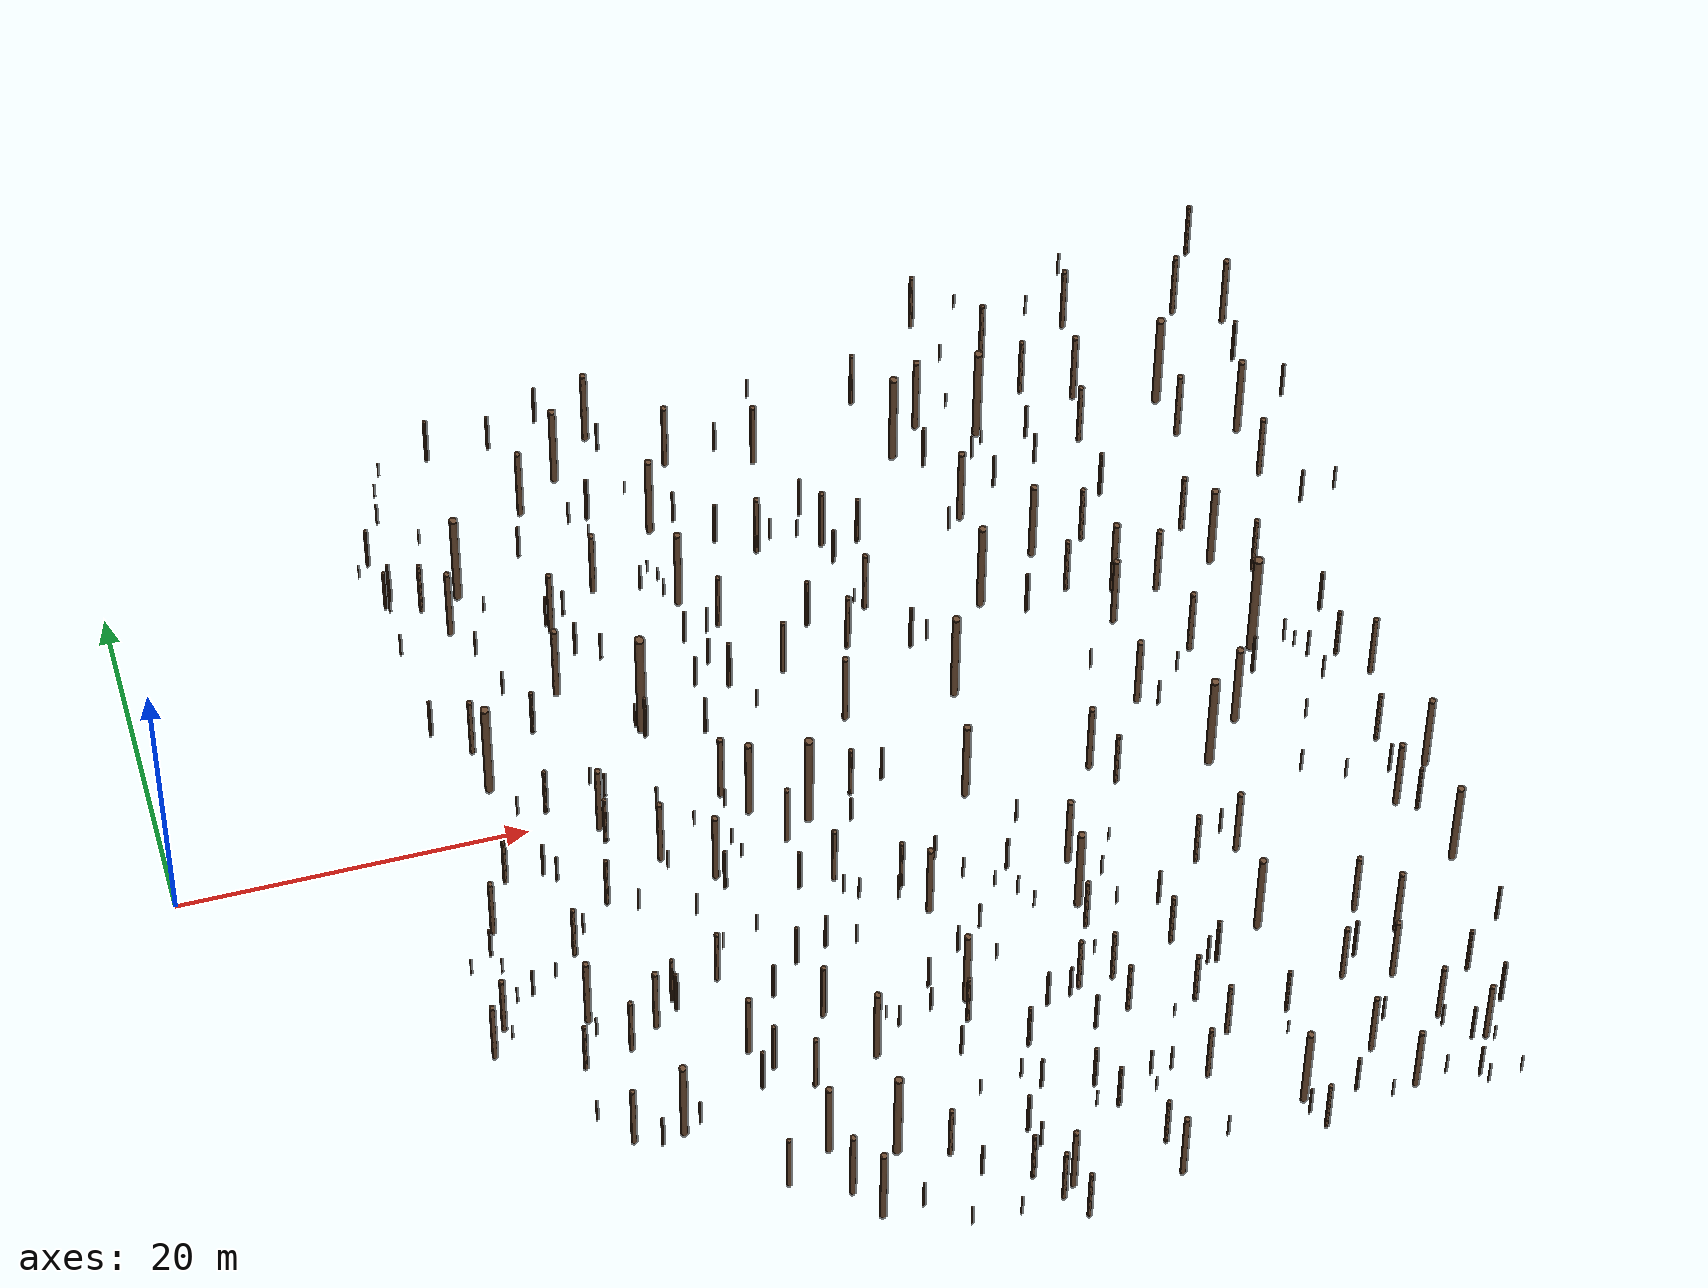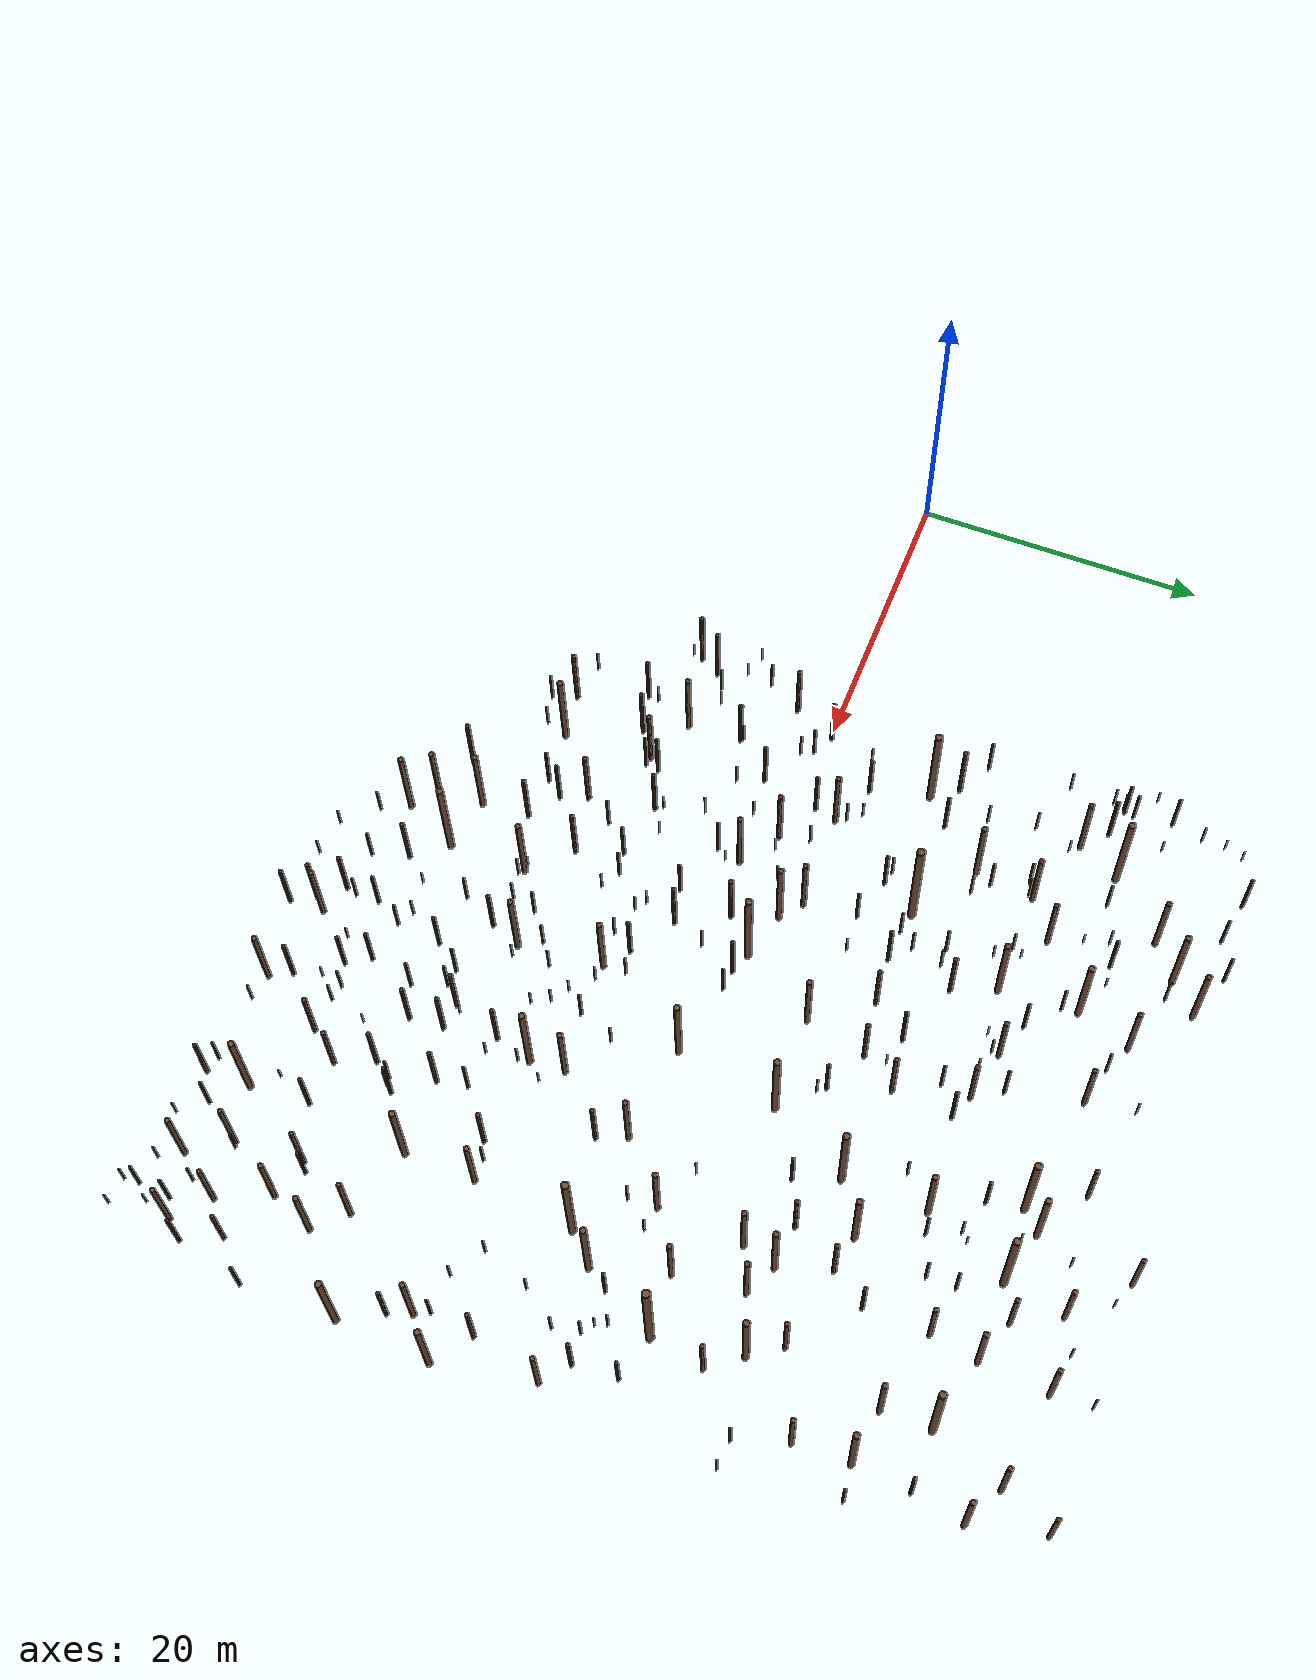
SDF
<?xml version="1.0" ?>
<!-- auto generated by generate_model_sdf.py -->
<sdf version="1.10">

<model name="lehrforst_trees">

<static>true</static>

  <link name='tree_0003'>
    <pose>28.569 8.946 -1.156 3.14159 0 0</pose>
    <visual name='visual'>
      <geometry>
        <cylinder>
          <radius>0.273</radius>
          <length>8.736</length>
        </cylinder>
      </geometry>
      <material>
        <ambient>0.42 0.29 0.19 1</ambient>
        <diffuse>0.42 0.29 0.19 1</diffuse>
        <specular>0.42 0.29 0.19 1</specular>
      </material>
    </visual>
    <collision name='collision'>
      <geometry>
        <cylinder>
          <radius>0.273</radius>
          <length>8.736</length>
        </cylinder>
      </geometry>
    </collision>
  </link>

  <link name='tree_0008'>
    <pose>63.142 3.854 1.507 3.14159 0 0</pose>
    <visual name='visual'>
      <geometry>
        <cylinder>
          <radius>0.262</radius>
          <length>8.384</length>
        </cylinder>
      </geometry>
      <material>
        <ambient>0.42 0.29 0.19 1</ambient>
        <diffuse>0.42 0.29 0.19 1</diffuse>
        <specular>0.42 0.29 0.19 1</specular>
      </material>
    </visual>
    <collision name='collision'>
      <geometry>
        <cylinder>
          <radius>0.262</radius>
          <length>8.384</length>
        </cylinder>
      </geometry>
    </collision>
  </link>

  <link name='tree_0011'>
    <pose>19.209 7.13 -1.709 3.14159 0 0</pose>
    <visual name='visual'>
      <geometry>
        <cylinder>
          <radius>0.246</radius>
          <length>7.872</length>
        </cylinder>
      </geometry>
      <material>
        <ambient>0.42 0.29 0.19 1</ambient>
        <diffuse>0.42 0.29 0.19 1</diffuse>
        <specular>0.42 0.29 0.19 1</specular>
      </material>
    </visual>
    <collision name='collision'>
      <geometry>
        <cylinder>
          <radius>0.246</radius>
          <length>7.872</length>
        </cylinder>
      </geometry>
    </collision>
  </link>

  <link name='tree_0013'>
    <pose>58.567 -3.165 1.219 3.14159 0 0</pose>
    <visual name='visual'>
      <geometry>
        <cylinder>
          <radius>0.243</radius>
          <length>7.776</length>
        </cylinder>
      </geometry>
      <material>
        <ambient>0.42 0.29 0.19 1</ambient>
        <diffuse>0.42 0.29 0.19 1</diffuse>
        <specular>0.42 0.29 0.19 1</specular>
      </material>
    </visual>
    <collision name='collision'>
      <geometry>
        <cylinder>
          <radius>0.243</radius>
          <length>7.776</length>
        </cylinder>
      </geometry>
    </collision>
  </link>

  <link name='tree_0015'>
    <pose>36.035 -0.141 -0.581 3.14159 0 0</pose>
    <visual name='visual'>
      <geometry>
        <cylinder>
          <radius>0.239</radius>
          <length>7.648</length>
        </cylinder>
      </geometry>
      <material>
        <ambient>0.42 0.29 0.19 1</ambient>
        <diffuse>0.42 0.29 0.19 1</diffuse>
        <specular>0.42 0.29 0.19 1</specular>
      </material>
    </visual>
    <collision name='collision'>
      <geometry>
        <cylinder>
          <radius>0.239</radius>
          <length>7.648</length>
        </cylinder>
      </geometry>
    </collision>
  </link>

  <link name='tree_0019'>
    <pose>52.082 22.715 0.86 3.14159 0 0</pose>
    <visual name='visual'>
      <geometry>
        <cylinder>
          <radius>0.236</radius>
          <length>7.552</length>
        </cylinder>
      </geometry>
      <material>
        <ambient>0.42 0.29 0.19 1</ambient>
        <diffuse>0.42 0.29 0.19 1</diffuse>
        <specular>0.42 0.29 0.19 1</specular>
      </material>
    </visual>
    <collision name='collision'>
      <geometry>
        <cylinder>
          <radius>0.236</radius>
          <length>7.552</length>
        </cylinder>
      </geometry>
    </collision>
  </link>

  <link name='tree_0021'>
    <pose>62.606 21.554 2.054 3.14159 0 0</pose>
    <visual name='visual'>
      <geometry>
        <cylinder>
          <radius>0.234</radius>
          <length>7.488</length>
        </cylinder>
      </geometry>
      <material>
        <ambient>0.42 0.29 0.19 1</ambient>
        <diffuse>0.42 0.29 0.19 1</diffuse>
        <specular>0.42 0.29 0.19 1</specular>
      </material>
    </visual>
    <collision name='collision'>
      <geometry>
        <cylinder>
          <radius>0.234</radius>
          <length>7.488</length>
        </cylinder>
      </geometry>
    </collision>
  </link>

  <link name='tree_0026'>
    <pose>20.56 21.103 -2.404 3.14159 0 0</pose>
    <visual name='visual'>
      <geometry>
        <cylinder>
          <radius>0.232</radius>
          <length>7.424</length>
        </cylinder>
      </geometry>
      <material>
        <ambient>0.42 0.29 0.19 1</ambient>
        <diffuse>0.42 0.29 0.19 1</diffuse>
        <specular>0.42 0.29 0.19 1</specular>
      </material>
    </visual>
    <collision name='collision'>
      <geometry>
        <cylinder>
          <radius>0.232</radius>
          <length>7.424</length>
        </cylinder>
      </geometry>
    </collision>
  </link>

  <link name='tree_0034'>
    <pose>35.26 -22.294 -1.24 3.14159 0 0</pose>
    <visual name='visual'>
      <geometry>
        <cylinder>
          <radius>0.230</radius>
          <length>7.360</length>
        </cylinder>
      </geometry>
      <material>
        <ambient>0.42 0.29 0.19 1</ambient>
        <diffuse>0.42 0.29 0.19 1</diffuse>
        <specular>0.42 0.29 0.19 1</specular>
      </material>
    </visual>
    <collision name='collision'>
      <geometry>
        <cylinder>
          <radius>0.230</radius>
          <length>7.360</length>
        </cylinder>
      </geometry>
    </collision>
  </link>

  <link name='tree_0035'>
    <pose>46.962 22.473 0.51 3.14159 0 0</pose>
    <visual name='visual'>
      <geometry>
        <cylinder>
          <radius>0.229</radius>
          <length>7.328</length>
        </cylinder>
      </geometry>
      <material>
        <ambient>0.42 0.29 0.19 1</ambient>
        <diffuse>0.42 0.29 0.19 1</diffuse>
        <specular>0.42 0.29 0.19 1</specular>
      </material>
    </visual>
    <collision name='collision'>
      <geometry>
        <cylinder>
          <radius>0.229</radius>
          <length>7.328</length>
        </cylinder>
      </geometry>
    </collision>
  </link>

  <link name='tree_0040'>
    <pose>49.152 11.139 0.233 3.14159 0 0</pose>
    <visual name='visual'>
      <geometry>
        <cylinder>
          <radius>0.226</radius>
          <length>7.232</length>
        </cylinder>
      </geometry>
      <material>
        <ambient>0.42 0.29 0.19 1</ambient>
        <diffuse>0.42 0.29 0.19 1</diffuse>
        <specular>0.42 0.29 0.19 1</specular>
      </material>
    </visual>
    <collision name='collision'>
      <geometry>
        <cylinder>
          <radius>0.226</radius>
          <length>7.232</length>
        </cylinder>
      </geometry>
    </collision>
  </link>

  <link name='tree_0041'>
    <pose>46.069 5.531 0.116 3.14159 0 0</pose>
    <visual name='visual'>
      <geometry>
        <cylinder>
          <radius>0.226</radius>
          <length>7.232</length>
        </cylinder>
      </geometry>
      <material>
        <ambient>0.42 0.29 0.19 1</ambient>
        <diffuse>0.42 0.29 0.19 1</diffuse>
        <specular>0.42 0.29 0.19 1</specular>
      </material>
    </visual>
    <collision name='collision'>
      <geometry>
        <cylinder>
          <radius>0.226</radius>
          <length>7.232</length>
        </cylinder>
      </geometry>
    </collision>
  </link>

  <link name='tree_0060'>
    <pose>48.872 -10.303 0.335 3.14159 0 0</pose>
    <visual name='visual'>
      <geometry>
        <cylinder>
          <radius>0.216</radius>
          <length>6.912</length>
        </cylinder>
      </geometry>
      <material>
        <ambient>0.42 0.29 0.19 1</ambient>
        <diffuse>0.42 0.29 0.19 1</diffuse>
        <specular>0.42 0.29 0.19 1</specular>
      </material>
    </visual>
    <collision name='collision'>
      <geometry>
        <cylinder>
          <radius>0.216</radius>
          <length>6.912</length>
        </cylinder>
      </geometry>
    </collision>
  </link>

  <link name='tree_0071'>
    <pose>60.635 -1.175 1.326 3.14159 0 0</pose>
    <visual name='visual'>
      <geometry>
        <cylinder>
          <radius>0.211</radius>
          <length>6.752</length>
        </cylinder>
      </geometry>
      <material>
        <ambient>0.42 0.29 0.19 1</ambient>
        <diffuse>0.42 0.29 0.19 1</diffuse>
        <specular>0.42 0.29 0.19 1</specular>
      </material>
    </visual>
    <collision name='collision'>
      <geometry>
        <cylinder>
          <radius>0.211</radius>
          <length>6.752</length>
        </cylinder>
      </geometry>
    </collision>
  </link>

  <link name='tree_0076'>
    <pose>69.408 -13.844 2.384 3.14159 0 0</pose>
    <visual name='visual'>
      <geometry>
        <cylinder>
          <radius>0.210</radius>
          <length>6.720</length>
        </cylinder>
      </geometry>
      <material>
        <ambient>0.42 0.29 0.19 1</ambient>
        <diffuse>0.42 0.29 0.19 1</diffuse>
        <specular>0.42 0.29 0.19 1</specular>
      </material>
    </visual>
    <collision name='collision'>
      <geometry>
        <cylinder>
          <radius>0.210</radius>
          <length>6.720</length>
        </cylinder>
      </geometry>
    </collision>
  </link>

  <link name='tree_0080'>
    <pose>24.254 -18.389 -1.363 3.14159 0 0</pose>
    <visual name='visual'>
      <geometry>
        <cylinder>
          <radius>0.209</radius>
          <length>6.688</length>
        </cylinder>
      </geometry>
      <material>
        <ambient>0.42 0.29 0.19 1</ambient>
        <diffuse>0.42 0.29 0.19 1</diffuse>
        <specular>0.42 0.29 0.19 1</specular>
      </material>
    </visual>
    <collision name='collision'>
      <geometry>
        <cylinder>
          <radius>0.209</radius>
          <length>6.688</length>
        </cylinder>
      </geometry>
    </collision>
  </link>

  <link name='tree_0083'>
    <pose>62.414 9.743 1.462 3.14159 0 0</pose>
    <visual name='visual'>
      <geometry>
        <cylinder>
          <radius>0.208</radius>
          <length>6.656</length>
        </cylinder>
      </geometry>
      <material>
        <ambient>0.42 0.29 0.19 1</ambient>
        <diffuse>0.42 0.29 0.19 1</diffuse>
        <specular>0.42 0.29 0.19 1</specular>
      </material>
    </visual>
    <collision name='collision'>
      <geometry>
        <cylinder>
          <radius>0.208</radius>
          <length>6.656</length>
        </cylinder>
      </geometry>
    </collision>
  </link>

  <link name='tree_0085'>
    <pose>32.181 21.663 -1.035 3.14159 0 0</pose>
    <visual name='visual'>
      <geometry>
        <cylinder>
          <radius>0.207</radius>
          <length>6.624</length>
        </cylinder>
      </geometry>
      <material>
        <ambient>0.42 0.29 0.19 1</ambient>
        <diffuse>0.42 0.29 0.19 1</diffuse>
        <specular>0.42 0.29 0.19 1</specular>
      </material>
    </visual>
    <collision name='collision'>
      <geometry>
        <cylinder>
          <radius>0.207</radius>
          <length>6.624</length>
        </cylinder>
      </geometry>
    </collision>
  </link>

  <link name='tree_0094'>
    <pose>57.165 -26.08 0.838 3.14159 0 0</pose>
    <visual name='visual'>
      <geometry>
        <cylinder>
          <radius>0.206</radius>
          <length>6.592</length>
        </cylinder>
      </geometry>
      <material>
        <ambient>0.42 0.29 0.19 1</ambient>
        <diffuse>0.42 0.29 0.19 1</diffuse>
        <specular>0.42 0.29 0.19 1</specular>
      </material>
    </visual>
    <collision name='collision'>
      <geometry>
        <cylinder>
          <radius>0.206</radius>
          <length>6.592</length>
        </cylinder>
      </geometry>
    </collision>
  </link>

  <link name='tree_0095'>
    <pose>44.75 -1.61 0.196 3.14159 0 0</pose>
    <visual name='visual'>
      <geometry>
        <cylinder>
          <radius>0.206</radius>
          <length>6.592</length>
        </cylinder>
      </geometry>
      <material>
        <ambient>0.42 0.29 0.19 1</ambient>
        <diffuse>0.42 0.29 0.19 1</diffuse>
        <specular>0.42 0.29 0.19 1</specular>
      </material>
    </visual>
    <collision name='collision'>
      <geometry>
        <cylinder>
          <radius>0.206</radius>
          <length>6.592</length>
        </cylinder>
      </geometry>
    </collision>
  </link>

  <link name='tree_0099'>
    <pose>32.546 16.219 -1.05 3.14159 0 0</pose>
    <visual name='visual'>
      <geometry>
        <cylinder>
          <radius>0.204</radius>
          <length>6.528</length>
        </cylinder>
      </geometry>
      <material>
        <ambient>0.42 0.29 0.19 1</ambient>
        <diffuse>0.42 0.29 0.19 1</diffuse>
        <specular>0.42 0.29 0.19 1</specular>
      </material>
    </visual>
    <collision name='collision'>
      <geometry>
        <cylinder>
          <radius>0.204</radius>
          <length>6.528</length>
        </cylinder>
      </geometry>
    </collision>
  </link>

  <link name='tree_0100'>
    <pose>32.823 0.866 -0.689 3.14159 0 0</pose>
    <visual name='visual'>
      <geometry>
        <cylinder>
          <radius>0.204</radius>
          <length>6.528</length>
        </cylinder>
      </geometry>
      <material>
        <ambient>0.42 0.29 0.19 1</ambient>
        <diffuse>0.42 0.29 0.19 1</diffuse>
        <specular>0.42 0.29 0.19 1</specular>
      </material>
    </visual>
    <collision name='collision'>
      <geometry>
        <cylinder>
          <radius>0.204</radius>
          <length>6.528</length>
        </cylinder>
      </geometry>
    </collision>
  </link>

  <link name='tree_0104'>
    <pose>57.872 -14.827 1.113 3.14159 0 0</pose>
    <visual name='visual'>
      <geometry>
        <cylinder>
          <radius>0.204</radius>
          <length>6.528</length>
        </cylinder>
      </geometry>
      <material>
        <ambient>0.42 0.29 0.19 1</ambient>
        <diffuse>0.42 0.29 0.19 1</diffuse>
        <specular>0.42 0.29 0.19 1</specular>
      </material>
    </visual>
    <collision name='collision'>
      <geometry>
        <cylinder>
          <radius>0.204</radius>
          <length>6.528</length>
        </cylinder>
      </geometry>
    </collision>
  </link>

  <link name='tree_0107'>
    <pose>27.715 26.8 -1.274 3.14159 0 0</pose>
    <visual name='visual'>
      <geometry>
        <cylinder>
          <radius>0.203</radius>
          <length>6.496</length>
        </cylinder>
      </geometry>
      <material>
        <ambient>0.42 0.29 0.19 1</ambient>
        <diffuse>0.42 0.29 0.19 1</diffuse>
        <specular>0.42 0.29 0.19 1</specular>
      </material>
    </visual>
    <collision name='collision'>
      <geometry>
        <cylinder>
          <radius>0.203</radius>
          <length>6.496</length>
        </cylinder>
      </geometry>
    </collision>
  </link>

  <link name='tree_0115'>
    <pose>66.375 17.798 2.19 3.14159 0 0</pose>
    <visual name='visual'>
      <geometry>
        <cylinder>
          <radius>0.200</radius>
          <length>6.400</length>
        </cylinder>
      </geometry>
      <material>
        <ambient>0.42 0.29 0.19 1</ambient>
        <diffuse>0.42 0.29 0.19 1</diffuse>
        <specular>0.42 0.29 0.19 1</specular>
      </material>
    </visual>
    <collision name='collision'>
      <geometry>
        <cylinder>
          <radius>0.200</radius>
          <length>6.400</length>
        </cylinder>
      </geometry>
    </collision>
  </link>

  <link name='tree_0118'>
    <pose>52.779 13.26 0.645 3.14159 0 0</pose>
    <visual name='visual'>
      <geometry>
        <cylinder>
          <radius>0.200</radius>
          <length>6.400</length>
        </cylinder>
      </geometry>
      <material>
        <ambient>0.42 0.29 0.19 1</ambient>
        <diffuse>0.42 0.29 0.19 1</diffuse>
        <specular>0.42 0.29 0.19 1</specular>
      </material>
    </visual>
    <collision name='collision'>
      <geometry>
        <cylinder>
          <radius>0.200</radius>
          <length>6.400</length>
        </cylinder>
      </geometry>
    </collision>
  </link>

  <link name='tree_0128'>
    <pose>41.271 -14.518 -0.474 3.14159 0 0</pose>
    <visual name='visual'>
      <geometry>
        <cylinder>
          <radius>0.197</radius>
          <length>6.304</length>
        </cylinder>
      </geometry>
      <material>
        <ambient>0.42 0.29 0.19 1</ambient>
        <diffuse>0.42 0.29 0.19 1</diffuse>
        <specular>0.42 0.29 0.19 1</specular>
      </material>
    </visual>
    <collision name='collision'>
      <geometry>
        <cylinder>
          <radius>0.197</radius>
          <length>6.304</length>
        </cylinder>
      </geometry>
    </collision>
  </link>

  <link name='tree_0133'>
    <pose>33.437 -26.119 -1.676 3.14159 0 0</pose>
    <visual name='visual'>
      <geometry>
        <cylinder>
          <radius>0.194</radius>
          <length>6.208</length>
        </cylinder>
      </geometry>
      <material>
        <ambient>0.42 0.29 0.19 1</ambient>
        <diffuse>0.42 0.29 0.19 1</diffuse>
        <specular>0.42 0.29 0.19 1</specular>
      </material>
    </visual>
    <collision name='collision'>
      <geometry>
        <cylinder>
          <radius>0.194</radius>
          <length>6.208</length>
        </cylinder>
      </geometry>
    </collision>
  </link>

  <link name='tree_0134'>
    <pose>31.612 -21.485 -1.44 3.14159 0 0</pose>
    <visual name='visual'>
      <geometry>
        <cylinder>
          <radius>0.194</radius>
          <length>6.208</length>
        </cylinder>
      </geometry>
      <material>
        <ambient>0.42 0.29 0.19 1</ambient>
        <diffuse>0.42 0.29 0.19 1</diffuse>
        <specular>0.42 0.29 0.19 1</specular>
      </material>
    </visual>
    <collision name='collision'>
      <geometry>
        <cylinder>
          <radius>0.194</radius>
          <length>6.208</length>
        </cylinder>
      </geometry>
    </collision>
  </link>

  <link name='tree_0142'>
    <pose>69.806 -7.501 2.163 3.14159 0 0</pose>
    <visual name='visual'>
      <geometry>
        <cylinder>
          <radius>0.192</radius>
          <length>6.144</length>
        </cylinder>
      </geometry>
      <material>
        <ambient>0.42 0.29 0.19 1</ambient>
        <diffuse>0.42 0.29 0.19 1</diffuse>
        <specular>0.42 0.29 0.19 1</specular>
      </material>
    </visual>
    <collision name='collision'>
      <geometry>
        <cylinder>
          <radius>0.192</radius>
          <length>6.144</length>
        </cylinder>
      </geometry>
    </collision>
  </link>

  <link name='tree_0143'>
    <pose>35.634 -16.514 -1.045 3.14159 0 0</pose>
    <visual name='visual'>
      <geometry>
        <cylinder>
          <radius>0.192</radius>
          <length>6.144</length>
        </cylinder>
      </geometry>
      <material>
        <ambient>0.42 0.29 0.19 1</ambient>
        <diffuse>0.42 0.29 0.19 1</diffuse>
        <specular>0.42 0.29 0.19 1</specular>
      </material>
    </visual>
    <collision name='collision'>
      <geometry>
        <cylinder>
          <radius>0.192</radius>
          <length>6.144</length>
        </cylinder>
      </geometry>
    </collision>
  </link>

  <link name='tree_0146'>
    <pose>56.52 9.371 0.958 3.14159 0 0</pose>
    <visual name='visual'>
      <geometry>
        <cylinder>
          <radius>0.191</radius>
          <length>6.112</length>
        </cylinder>
      </geometry>
      <material>
        <ambient>0.42 0.29 0.19 1</ambient>
        <diffuse>0.42 0.29 0.19 1</diffuse>
        <specular>0.42 0.29 0.19 1</specular>
      </material>
    </visual>
    <collision name='collision'>
      <geometry>
        <cylinder>
          <radius>0.191</radius>
          <length>6.112</length>
        </cylinder>
      </geometry>
    </collision>
  </link>

  <link name='tree_0147'>
    <pose>49.512 16.935 0.313 3.14159 0 0</pose>
    <visual name='visual'>
      <geometry>
        <cylinder>
          <radius>0.191</radius>
          <length>6.112</length>
        </cylinder>
      </geometry>
      <material>
        <ambient>0.42 0.29 0.19 1</ambient>
        <diffuse>0.42 0.29 0.19 1</diffuse>
        <specular>0.42 0.29 0.19 1</specular>
      </material>
    </visual>
    <collision name='collision'>
      <geometry>
        <cylinder>
          <radius>0.191</radius>
          <length>6.112</length>
        </cylinder>
      </geometry>
    </collision>
  </link>

  <link name='tree_0154'>
    <pose>24.334 12.093 -1.757 3.14159 0 0</pose>
    <visual name='visual'>
      <geometry>
        <cylinder>
          <radius>0.190</radius>
          <length>6.080</length>
        </cylinder>
      </geometry>
      <material>
        <ambient>0.42 0.29 0.19 1</ambient>
        <diffuse>0.42 0.29 0.19 1</diffuse>
        <specular>0.42 0.29 0.19 1</specular>
      </material>
    </visual>
    <collision name='collision'>
      <geometry>
        <cylinder>
          <radius>0.190</radius>
          <length>6.080</length>
        </cylinder>
      </geometry>
    </collision>
  </link>

  <link name='tree_0156'>
    <pose>48.653 23.689 0.677 3.14159 0 0</pose>
    <visual name='visual'>
      <geometry>
        <cylinder>
          <radius>0.190</radius>
          <length>6.080</length>
        </cylinder>
      </geometry>
      <material>
        <ambient>0.42 0.29 0.19 1</ambient>
        <diffuse>0.42 0.29 0.19 1</diffuse>
        <specular>0.42 0.29 0.19 1</specular>
      </material>
    </visual>
    <collision name='collision'>
      <geometry>
        <cylinder>
          <radius>0.190</radius>
          <length>6.080</length>
        </cylinder>
      </geometry>
    </collision>
  </link>

  <link name='tree_0164'>
    <pose>30.04 28.734 -0.795 3.14159 0 0</pose>
    <visual name='visual'>
      <geometry>
        <cylinder>
          <radius>0.187</radius>
          <length>5.984</length>
        </cylinder>
      </geometry>
      <material>
        <ambient>0.42 0.29 0.19 1</ambient>
        <diffuse>0.42 0.29 0.19 1</diffuse>
        <specular>0.42 0.29 0.19 1</specular>
      </material>
    </visual>
    <collision name='collision'>
      <geometry>
        <cylinder>
          <radius>0.187</radius>
          <length>5.984</length>
        </cylinder>
      </geometry>
    </collision>
  </link>

  <link name='tree_0173'>
    <pose>40.775 -8.554 -0.27 3.14159 0 0</pose>
    <visual name='visual'>
      <geometry>
        <cylinder>
          <radius>0.186</radius>
          <length>5.952</length>
        </cylinder>
      </geometry>
      <material>
        <ambient>0.42 0.29 0.19 1</ambient>
        <diffuse>0.42 0.29 0.19 1</diffuse>
        <specular>0.42 0.29 0.19 1</specular>
      </material>
    </visual>
    <collision name='collision'>
      <geometry>
        <cylinder>
          <radius>0.186</radius>
          <length>5.952</length>
        </cylinder>
      </geometry>
    </collision>
  </link>

  <link name='tree_0188'>
    <pose>29.904 -3.082 -0.838 3.14159 0 0</pose>
    <visual name='visual'>
      <geometry>
        <cylinder>
          <radius>0.182</radius>
          <length>5.824</length>
        </cylinder>
      </geometry>
      <material>
        <ambient>0.42 0.29 0.19 1</ambient>
        <diffuse>0.42 0.29 0.19 1</diffuse>
        <specular>0.42 0.29 0.19 1</specular>
      </material>
    </visual>
    <collision name='collision'>
      <geometry>
        <cylinder>
          <radius>0.182</radius>
          <length>5.824</length>
        </cylinder>
      </geometry>
    </collision>
  </link>

  <link name='tree_0197'>
    <pose>20.782 -10.396 -1.178 3.14159 0 0</pose>
    <visual name='visual'>
      <geometry>
        <cylinder>
          <radius>0.180</radius>
          <length>5.760</length>
        </cylinder>
      </geometry>
      <material>
        <ambient>0.42 0.29 0.19 1</ambient>
        <diffuse>0.42 0.29 0.19 1</diffuse>
        <specular>0.42 0.29 0.19 1</specular>
      </material>
    </visual>
    <collision name='collision'>
      <geometry>
        <cylinder>
          <radius>0.180</radius>
          <length>5.760</length>
        </cylinder>
      </geometry>
    </collision>
  </link>

  <link name='tree_0202'>
    <pose>48.984 -7.73 0.366 3.14159 0 0</pose>
    <visual name='visual'>
      <geometry>
        <cylinder>
          <radius>0.179</radius>
          <length>5.728</length>
        </cylinder>
      </geometry>
      <material>
        <ambient>0.42 0.29 0.19 1</ambient>
        <diffuse>0.42 0.29 0.19 1</diffuse>
        <specular>0.42 0.29 0.19 1</specular>
      </material>
    </visual>
    <collision name='collision'>
      <geometry>
        <cylinder>
          <radius>0.179</radius>
          <length>5.728</length>
        </cylinder>
      </geometry>
    </collision>
  </link>

  <link name='tree_0205'>
    <pose>19.484 18.128 -2.468 3.14159 0 0</pose>
    <visual name='visual'>
      <geometry>
        <cylinder>
          <radius>0.179</radius>
          <length>5.728</length>
        </cylinder>
      </geometry>
      <material>
        <ambient>0.42 0.29 0.19 1</ambient>
        <diffuse>0.42 0.29 0.19 1</diffuse>
        <specular>0.42 0.29 0.19 1</specular>
      </material>
    </visual>
    <collision name='collision'>
      <geometry>
        <cylinder>
          <radius>0.179</radius>
          <length>5.728</length>
        </cylinder>
      </geometry>
    </collision>
  </link>

  <link name='tree_0208'>
    <pose>25.237 24.976 -1.773 3.14159 0 0</pose>
    <visual name='visual'>
      <geometry>
        <cylinder>
          <radius>0.179</radius>
          <length>5.728</length>
        </cylinder>
      </geometry>
      <material>
        <ambient>0.42 0.29 0.19 1</ambient>
        <diffuse>0.42 0.29 0.19 1</diffuse>
        <specular>0.42 0.29 0.19 1</specular>
      </material>
    </visual>
    <collision name='collision'>
      <geometry>
        <cylinder>
          <radius>0.179</radius>
          <length>5.728</length>
        </cylinder>
      </geometry>
    </collision>
  </link>

  <link name='tree_0210'>
    <pose>55.895 7.127 0.859 3.14159 0 0</pose>
    <visual name='visual'>
      <geometry>
        <cylinder>
          <radius>0.179</radius>
          <length>5.728</length>
        </cylinder>
      </geometry>
      <material>
        <ambient>0.42 0.29 0.19 1</ambient>
        <diffuse>0.42 0.29 0.19 1</diffuse>
        <specular>0.42 0.29 0.19 1</specular>
      </material>
    </visual>
    <collision name='collision'>
      <geometry>
        <cylinder>
          <radius>0.179</radius>
          <length>5.728</length>
        </cylinder>
      </geometry>
    </collision>
  </link>

  <link name='tree_0212'>
    <pose>39.603 5.335 -0.483 3.14159 0 0</pose>
    <visual name='visual'>
      <geometry>
        <cylinder>
          <radius>0.179</radius>
          <length>5.728</length>
        </cylinder>
      </geometry>
      <material>
        <ambient>0.42 0.29 0.19 1</ambient>
        <diffuse>0.42 0.29 0.19 1</diffuse>
        <specular>0.42 0.29 0.19 1</specular>
      </material>
    </visual>
    <collision name='collision'>
      <geometry>
        <cylinder>
          <radius>0.179</radius>
          <length>5.728</length>
        </cylinder>
      </geometry>
    </collision>
  </link>

  <link name='tree_0222'>
    <pose>32.17 -24.463 -1.665 3.14159 0 0</pose>
    <visual name='visual'>
      <geometry>
        <cylinder>
          <radius>0.177</radius>
          <length>5.664</length>
        </cylinder>
      </geometry>
      <material>
        <ambient>0.42 0.29 0.19 1</ambient>
        <diffuse>0.42 0.29 0.19 1</diffuse>
        <specular>0.42 0.29 0.19 1</specular>
      </material>
    </visual>
    <collision name='collision'>
      <geometry>
        <cylinder>
          <radius>0.177</radius>
          <length>5.664</length>
        </cylinder>
      </geometry>
    </collision>
  </link>

  <link name='tree_0223'>
    <pose>55.606 1.319 1.012 3.14159 0 0</pose>
    <visual name='visual'>
      <geometry>
        <cylinder>
          <radius>0.177</radius>
          <length>5.664</length>
        </cylinder>
      </geometry>
      <material>
        <ambient>0.42 0.29 0.19 1</ambient>
        <diffuse>0.42 0.29 0.19 1</diffuse>
        <specular>0.42 0.29 0.19 1</specular>
      </material>
    </visual>
    <collision name='collision'>
      <geometry>
        <cylinder>
          <radius>0.177</radius>
          <length>5.664</length>
        </cylinder>
      </geometry>
    </collision>
  </link>

  <link name='tree_0225'>
    <pose>51.808 -2.17 0.675 3.14159 0 0</pose>
    <visual name='visual'>
      <geometry>
        <cylinder>
          <radius>0.176</radius>
          <length>5.632</length>
        </cylinder>
      </geometry>
      <material>
        <ambient>0.42 0.29 0.19 1</ambient>
        <diffuse>0.42 0.29 0.19 1</diffuse>
        <specular>0.42 0.29 0.19 1</specular>
      </material>
    </visual>
    <collision name='collision'>
      <geometry>
        <cylinder>
          <radius>0.176</radius>
          <length>5.632</length>
        </cylinder>
      </geometry>
    </collision>
  </link>

  <link name='tree_0230'>
    <pose>67.448 -9.612 1.912 3.14159 0 0</pose>
    <visual name='visual'>
      <geometry>
        <cylinder>
          <radius>0.176</radius>
          <length>5.632</length>
        </cylinder>
      </geometry>
      <material>
        <ambient>0.42 0.29 0.19 1</ambient>
        <diffuse>0.42 0.29 0.19 1</diffuse>
        <specular>0.42 0.29 0.19 1</specular>
      </material>
    </visual>
    <collision name='collision'>
      <geometry>
        <cylinder>
          <radius>0.176</radius>
          <length>5.632</length>
        </cylinder>
      </geometry>
    </collision>
  </link>

  <link name='tree_0231'>
    <pose>24.409 1.859 -1.091 3.14159 0 0</pose>
    <visual name='visual'>
      <geometry>
        <cylinder>
          <radius>0.176</radius>
          <length>5.632</length>
        </cylinder>
      </geometry>
      <material>
        <ambient>0.42 0.29 0.19 1</ambient>
        <diffuse>0.42 0.29 0.19 1</diffuse>
        <specular>0.42 0.29 0.19 1</specular>
      </material>
    </visual>
    <collision name='collision'>
      <geometry>
        <cylinder>
          <radius>0.176</radius>
          <length>5.632</length>
        </cylinder>
      </geometry>
    </collision>
  </link>

  <link name='tree_0234'>
    <pose>67.581 24.981 2.8 3.14159 0 0</pose>
    <visual name='visual'>
      <geometry>
        <cylinder>
          <radius>0.174</radius>
          <length>5.568</length>
        </cylinder>
      </geometry>
      <material>
        <ambient>0.42 0.29 0.19 1</ambient>
        <diffuse>0.42 0.29 0.19 1</diffuse>
        <specular>0.42 0.29 0.19 1</specular>
      </material>
    </visual>
    <collision name='collision'>
      <geometry>
        <cylinder>
          <radius>0.174</radius>
          <length>5.568</length>
        </cylinder>
      </geometry>
    </collision>
  </link>

  <link name='tree_0238'>
    <pose>57.901 22.753 1.447 3.14159 0 0</pose>
    <visual name='visual'>
      <geometry>
        <cylinder>
          <radius>0.174</radius>
          <length>5.568</length>
        </cylinder>
      </geometry>
      <material>
        <ambient>0.42 0.29 0.19 1</ambient>
        <diffuse>0.42 0.29 0.19 1</diffuse>
        <specular>0.42 0.29 0.19 1</specular>
      </material>
    </visual>
    <collision name='collision'>
      <geometry>
        <cylinder>
          <radius>0.174</radius>
          <length>5.568</length>
        </cylinder>
      </geometry>
    </collision>
  </link>

  <link name='tree_0250'>
    <pose>58.799 8.423 1.165 3.14159 0 0</pose>
    <visual name='visual'>
      <geometry>
        <cylinder>
          <radius>0.171</radius>
          <length>5.472</length>
        </cylinder>
      </geometry>
      <material>
        <ambient>0.42 0.29 0.19 1</ambient>
        <diffuse>0.42 0.29 0.19 1</diffuse>
        <specular>0.42 0.29 0.19 1</specular>
      </material>
    </visual>
    <collision name='collision'>
      <geometry>
        <cylinder>
          <radius>0.171</radius>
          <length>5.472</length>
        </cylinder>
      </geometry>
    </collision>
  </link>

  <link name='tree_0252'>
    <pose>49.555 -28.673 -0.0860000000000001 3.14159 0 0</pose>
    <visual name='visual'>
      <geometry>
        <cylinder>
          <radius>0.171</radius>
          <length>5.472</length>
        </cylinder>
      </geometry>
      <material>
        <ambient>0.42 0.29 0.19 1</ambient>
        <diffuse>0.42 0.29 0.19 1</diffuse>
        <specular>0.42 0.29 0.19 1</specular>
      </material>
    </visual>
    <collision name='collision'>
      <geometry>
        <cylinder>
          <radius>0.171</radius>
          <length>5.472</length>
        </cylinder>
      </geometry>
    </collision>
  </link>

  <link name='tree_0253'>
    <pose>64.9 -17.749 1.922 3.14159 0 0</pose>
    <visual name='visual'>
      <geometry>
        <cylinder>
          <radius>0.171</radius>
          <length>5.472</length>
        </cylinder>
      </geometry>
      <material>
        <ambient>0.42 0.29 0.19 1</ambient>
        <diffuse>0.42 0.29 0.19 1</diffuse>
        <specular>0.42 0.29 0.19 1</specular>
      </material>
    </visual>
    <collision name='collision'>
      <geometry>
        <cylinder>
          <radius>0.171</radius>
          <length>5.472</length>
        </cylinder>
      </geometry>
    </collision>
  </link>

  <link name='tree_0259'>
    <pose>31.504 2.118 -0.859 3.14159 0 0</pose>
    <visual name='visual'>
      <geometry>
        <cylinder>
          <radius>0.170</radius>
          <length>5.440</length>
        </cylinder>
      </geometry>
      <material>
        <ambient>0.42 0.29 0.19 1</ambient>
        <diffuse>0.42 0.29 0.19 1</diffuse>
        <specular>0.42 0.29 0.19 1</specular>
      </material>
    </visual>
    <collision name='collision'>
      <geometry>
        <cylinder>
          <radius>0.170</radius>
          <length>5.440</length>
        </cylinder>
      </geometry>
    </collision>
  </link>

  <link name='tree_0262'>
    <pose>62.89 18.31 1.819 3.14159 0 0</pose>
    <visual name='visual'>
      <geometry>
        <cylinder>
          <radius>0.169</radius>
          <length>5.408</length>
        </cylinder>
      </geometry>
      <material>
        <ambient>0.42 0.29 0.19 1</ambient>
        <diffuse>0.42 0.29 0.19 1</diffuse>
        <specular>0.42 0.29 0.19 1</specular>
      </material>
    </visual>
    <collision name='collision'>
      <geometry>
        <cylinder>
          <radius>0.169</radius>
          <length>5.408</length>
        </cylinder>
      </geometry>
    </collision>
  </link>

  <link name='tree_0263'>
    <pose>27.186 -1.236 -0.91 3.14159 0 0</pose>
    <visual name='visual'>
      <geometry>
        <cylinder>
          <radius>0.169</radius>
          <length>5.408</length>
        </cylinder>
      </geometry>
      <material>
        <ambient>0.42 0.29 0.19 1</ambient>
        <diffuse>0.42 0.29 0.19 1</diffuse>
        <specular>0.42 0.29 0.19 1</specular>
      </material>
    </visual>
    <collision name='collision'>
      <geometry>
        <cylinder>
          <radius>0.169</radius>
          <length>5.408</length>
        </cylinder>
      </geometry>
    </collision>
  </link>

  <link name='tree_0265'>
    <pose>58.102 -9.891 1.034 3.14159 0 0</pose>
    <visual name='visual'>
      <geometry>
        <cylinder>
          <radius>0.169</radius>
          <length>5.408</length>
        </cylinder>
      </geometry>
      <material>
        <ambient>0.42 0.29 0.19 1</ambient>
        <diffuse>0.42 0.29 0.19 1</diffuse>
        <specular>0.42 0.29 0.19 1</specular>
      </material>
    </visual>
    <collision name='collision'>
      <geometry>
        <cylinder>
          <radius>0.169</radius>
          <length>5.408</length>
        </cylinder>
      </geometry>
    </collision>
  </link>

  <link name='tree_0270'>
    <pose>25.022 16.303 -1.87 3.14159 0 0</pose>
    <visual name='visual'>
      <geometry>
        <cylinder>
          <radius>0.168</radius>
          <length>5.376</length>
        </cylinder>
      </geometry>
      <material>
        <ambient>0.42 0.29 0.19 1</ambient>
        <diffuse>0.42 0.29 0.19 1</diffuse>
        <specular>0.42 0.29 0.19 1</specular>
      </material>
    </visual>
    <collision name='collision'>
      <geometry>
        <cylinder>
          <radius>0.168</radius>
          <length>5.376</length>
        </cylinder>
      </geometry>
    </collision>
  </link>

  <link name='tree_0271'>
    <pose>43.701 -27.643 -0.687 3.14159 0 0</pose>
    <visual name='visual'>
      <geometry>
        <cylinder>
          <radius>0.168</radius>
          <length>5.376</length>
        </cylinder>
      </geometry>
      <material>
        <ambient>0.42 0.29 0.19 1</ambient>
        <diffuse>0.42 0.29 0.19 1</diffuse>
        <specular>0.42 0.29 0.19 1</specular>
      </material>
    </visual>
    <collision name='collision'>
      <geometry>
        <cylinder>
          <radius>0.168</radius>
          <length>5.376</length>
        </cylinder>
      </geometry>
    </collision>
  </link>

  <link name='tree_0273'>
    <pose>34.035 25.412 -0.66 3.14159 0 0</pose>
    <visual name='visual'>
      <geometry>
        <cylinder>
          <radius>0.167</radius>
          <length>5.344</length>
        </cylinder>
      </geometry>
      <material>
        <ambient>0.42 0.29 0.19 1</ambient>
        <diffuse>0.42 0.29 0.19 1</diffuse>
        <specular>0.42 0.29 0.19 1</specular>
      </material>
    </visual>
    <collision name='collision'>
      <geometry>
        <cylinder>
          <radius>0.167</radius>
          <length>5.344</length>
        </cylinder>
      </geometry>
    </collision>
  </link>

  <link name='tree_0275'>
    <pose>24.317 -11.821 -1.164 3.14159 0 0</pose>
    <visual name='visual'>
      <geometry>
        <cylinder>
          <radius>0.166</radius>
          <length>5.312</length>
        </cylinder>
      </geometry>
      <material>
        <ambient>0.42 0.29 0.19 1</ambient>
        <diffuse>0.42 0.29 0.19 1</diffuse>
        <specular>0.42 0.29 0.19 1</specular>
      </material>
    </visual>
    <collision name='collision'>
      <geometry>
        <cylinder>
          <radius>0.166</radius>
          <length>5.312</length>
        </cylinder>
      </geometry>
    </collision>
  </link>

  <link name='tree_0281'>
    <pose>27.969 18.211 -1.557 3.14159 0 0</pose>
    <visual name='visual'>
      <geometry>
        <cylinder>
          <radius>0.165</radius>
          <length>5.280</length>
        </cylinder>
      </geometry>
      <material>
        <ambient>0.42 0.29 0.19 1</ambient>
        <diffuse>0.42 0.29 0.19 1</diffuse>
        <specular>0.42 0.29 0.19 1</specular>
      </material>
    </visual>
    <collision name='collision'>
      <geometry>
        <cylinder>
          <radius>0.165</radius>
          <length>5.280</length>
        </cylinder>
      </geometry>
    </collision>
  </link>

  <link name='tree_0286'>
    <pose>63.034 -27.394 1.361 3.14159 0 0</pose>
    <visual name='visual'>
      <geometry>
        <cylinder>
          <radius>0.164</radius>
          <length>5.248</length>
        </cylinder>
      </geometry>
      <material>
        <ambient>0.42 0.29 0.19 1</ambient>
        <diffuse>0.42 0.29 0.19 1</diffuse>
        <specular>0.42 0.29 0.19 1</specular>
      </material>
    </visual>
    <collision name='collision'>
      <geometry>
        <cylinder>
          <radius>0.164</radius>
          <length>5.248</length>
        </cylinder>
      </geometry>
    </collision>
  </link>

  <link name='tree_0291'>
    <pose>59.422 3.784 1.213 3.14159 0 0</pose>
    <visual name='visual'>
      <geometry>
        <cylinder>
          <radius>0.164</radius>
          <length>5.248</length>
        </cylinder>
      </geometry>
      <material>
        <ambient>0.42 0.29 0.19 1</ambient>
        <diffuse>0.42 0.29 0.19 1</diffuse>
        <specular>0.42 0.29 0.19 1</specular>
      </material>
    </visual>
    <collision name='collision'>
      <geometry>
        <cylinder>
          <radius>0.164</radius>
          <length>5.248</length>
        </cylinder>
      </geometry>
    </collision>
  </link>

  <link name='tree_0296'>
    <pose>28.853 -14.649 -1.272 3.14159 0 0</pose>
    <visual name='visual'>
      <geometry>
        <cylinder>
          <radius>0.163</radius>
          <length>5.216</length>
        </cylinder>
      </geometry>
      <material>
        <ambient>0.42 0.29 0.19 1</ambient>
        <diffuse>0.42 0.29 0.19 1</diffuse>
        <specular>0.42 0.29 0.19 1</specular>
      </material>
    </visual>
    <collision name='collision'>
      <geometry>
        <cylinder>
          <radius>0.163</radius>
          <length>5.216</length>
        </cylinder>
      </geometry>
    </collision>
  </link>

  <link name='tree_0304'>
    <pose>63.774 -20.646 1.965 3.14159 0 0</pose>
    <visual name='visual'>
      <geometry>
        <cylinder>
          <radius>0.161</radius>
          <length>5.152</length>
        </cylinder>
      </geometry>
      <material>
        <ambient>0.42 0.29 0.19 1</ambient>
        <diffuse>0.42 0.29 0.19 1</diffuse>
        <specular>0.42 0.29 0.19 1</specular>
      </material>
    </visual>
    <collision name='collision'>
      <geometry>
        <cylinder>
          <radius>0.161</radius>
          <length>5.152</length>
        </cylinder>
      </geometry>
    </collision>
  </link>

  <link name='tree_0306'>
    <pose>38.941 23.874 -0.191 3.14159 0 0</pose>
    <visual name='visual'>
      <geometry>
        <cylinder>
          <radius>0.161</radius>
          <length>5.152</length>
        </cylinder>
      </geometry>
      <material>
        <ambient>0.42 0.29 0.19 1</ambient>
        <diffuse>0.42 0.29 0.19 1</diffuse>
        <specular>0.42 0.29 0.19 1</specular>
      </material>
    </visual>
    <collision name='collision'>
      <geometry>
        <cylinder>
          <radius>0.161</radius>
          <length>5.152</length>
        </cylinder>
      </geometry>
    </collision>
  </link>

  <link name='tree_0307'>
    <pose>21.382 -18.65 -1.42 3.14159 0 0</pose>
    <visual name='visual'>
      <geometry>
        <cylinder>
          <radius>0.161</radius>
          <length>5.152</length>
        </cylinder>
      </geometry>
      <material>
        <ambient>0.42 0.29 0.19 1</ambient>
        <diffuse>0.42 0.29 0.19 1</diffuse>
        <specular>0.42 0.29 0.19 1</specular>
      </material>
    </visual>
    <collision name='collision'>
      <geometry>
        <cylinder>
          <radius>0.161</radius>
          <length>5.152</length>
        </cylinder>
      </geometry>
    </collision>
  </link>

  <link name='tree_0308'>
    <pose>58.53 27.305 2.078 3.14159 0 0</pose>
    <visual name='visual'>
      <geometry>
        <cylinder>
          <radius>0.160</radius>
          <length>5.120</length>
        </cylinder>
      </geometry>
      <material>
        <ambient>0.42 0.29 0.19 1</ambient>
        <diffuse>0.42 0.29 0.19 1</diffuse>
        <specular>0.42 0.29 0.19 1</specular>
      </material>
    </visual>
    <collision name='collision'>
      <geometry>
        <cylinder>
          <radius>0.160</radius>
          <length>5.120</length>
        </cylinder>
      </geometry>
    </collision>
  </link>

  <link name='tree_0312'>
    <pose>64.942 26.337 2.516 3.14159 0 0</pose>
    <visual name='visual'>
      <geometry>
        <cylinder>
          <radius>0.159</radius>
          <length>5.088</length>
        </cylinder>
      </geometry>
      <material>
        <ambient>0.42 0.29 0.19 1</ambient>
        <diffuse>0.42 0.29 0.19 1</diffuse>
        <specular>0.42 0.29 0.19 1</specular>
      </material>
    </visual>
    <collision name='collision'>
      <geometry>
        <cylinder>
          <radius>0.159</radius>
          <length>5.088</length>
        </cylinder>
      </geometry>
    </collision>
  </link>

  <link name='tree_0316'>
    <pose>61.328 -24.705 1.452 3.14159 0 0</pose>
    <visual name='visual'>
      <geometry>
        <cylinder>
          <radius>0.158</radius>
          <length>5.056</length>
        </cylinder>
      </geometry>
      <material>
        <ambient>0.42 0.29 0.19 1</ambient>
        <diffuse>0.42 0.29 0.19 1</diffuse>
        <specular>0.42 0.29 0.19 1</specular>
      </material>
    </visual>
    <collision name='collision'>
      <geometry>
        <cylinder>
          <radius>0.158</radius>
          <length>5.056</length>
        </cylinder>
      </geometry>
    </collision>
  </link>

  <link name='tree_0320'>
    <pose>66.608 14.157 1.961 3.14159 0 0</pose>
    <visual name='visual'>
      <geometry>
        <cylinder>
          <radius>0.158</radius>
          <length>5.056</length>
        </cylinder>
      </geometry>
      <material>
        <ambient>0.42 0.29 0.19 1</ambient>
        <diffuse>0.42 0.29 0.19 1</diffuse>
        <specular>0.42 0.29 0.19 1</specular>
      </material>
    </visual>
    <collision name='collision'>
      <geometry>
        <cylinder>
          <radius>0.158</radius>
          <length>5.056</length>
        </cylinder>
      </geometry>
    </collision>
  </link>

  <link name='tree_0325'>
    <pose>15.254 -11.534 -1.339 3.14159 0 0</pose>
    <visual name='visual'>
      <geometry>
        <cylinder>
          <radius>0.157</radius>
          <length>5.024</length>
        </cylinder>
      </geometry>
      <material>
        <ambient>0.42 0.29 0.19 1</ambient>
        <diffuse>0.42 0.29 0.19 1</diffuse>
        <specular>0.42 0.29 0.19 1</specular>
      </material>
    </visual>
    <collision name='collision'>
      <geometry>
        <cylinder>
          <radius>0.157</radius>
          <length>5.024</length>
        </cylinder>
      </geometry>
    </collision>
  </link>

  <link name='tree_0326'>
    <pose>63.068 -15.884 1.667 3.14159 0 0</pose>
    <visual name='visual'>
      <geometry>
        <cylinder>
          <radius>0.157</radius>
          <length>5.024</length>
        </cylinder>
      </geometry>
      <material>
        <ambient>0.42 0.29 0.19 1</ambient>
        <diffuse>0.42 0.29 0.19 1</diffuse>
        <specular>0.42 0.29 0.19 1</specular>
      </material>
    </visual>
    <collision name='collision'>
      <geometry>
        <cylinder>
          <radius>0.157</radius>
          <length>5.024</length>
        </cylinder>
      </geometry>
    </collision>
  </link>

  <link name='tree_0334'>
    <pose>68.649 -0.917 1.975 3.14159 0 0</pose>
    <visual name='visual'>
      <geometry>
        <cylinder>
          <radius>0.156</radius>
          <length>4.992</length>
        </cylinder>
      </geometry>
      <material>
        <ambient>0.42 0.29 0.19 1</ambient>
        <diffuse>0.42 0.29 0.19 1</diffuse>
        <specular>0.42 0.29 0.19 1</specular>
      </material>
    </visual>
    <collision name='collision'>
      <geometry>
        <cylinder>
          <radius>0.156</radius>
          <length>4.992</length>
        </cylinder>
      </geometry>
    </collision>
  </link>

  <link name='tree_0338'>
    <pose>37.598 17.767 -0.576 3.14159 0 0</pose>
    <visual name='visual'>
      <geometry>
        <cylinder>
          <radius>0.155</radius>
          <length>4.960</length>
        </cylinder>
      </geometry>
      <material>
        <ambient>0.42 0.29 0.19 1</ambient>
        <diffuse>0.42 0.29 0.19 1</diffuse>
        <specular>0.42 0.29 0.19 1</specular>
      </material>
    </visual>
    <collision name='collision'>
      <geometry>
        <cylinder>
          <radius>0.155</radius>
          <length>4.960</length>
        </cylinder>
      </geometry>
    </collision>
  </link>

  <link name='tree_0339'>
    <pose>42.559 12.171 -0.319 3.14159 0 0</pose>
    <visual name='visual'>
      <geometry>
        <cylinder>
          <radius>0.155</radius>
          <length>4.960</length>
        </cylinder>
      </geometry>
      <material>
        <ambient>0.42 0.29 0.19 1</ambient>
        <diffuse>0.42 0.29 0.19 1</diffuse>
        <specular>0.42 0.29 0.19 1</specular>
      </material>
    </visual>
    <collision name='collision'>
      <geometry>
        <cylinder>
          <radius>0.155</radius>
          <length>4.960</length>
        </cylinder>
      </geometry>
    </collision>
  </link>

  <link name='tree_0342'>
    <pose>67.457 -25.881 2.075 3.14159 0 0</pose>
    <visual name='visual'>
      <geometry>
        <cylinder>
          <radius>0.155</radius>
          <length>4.960</length>
        </cylinder>
      </geometry>
      <material>
        <ambient>0.42 0.29 0.19 1</ambient>
        <diffuse>0.42 0.29 0.19 1</diffuse>
        <specular>0.42 0.29 0.19 1</specular>
      </material>
    </visual>
    <collision name='collision'>
      <geometry>
        <cylinder>
          <radius>0.155</radius>
          <length>4.960</length>
        </cylinder>
      </geometry>
    </collision>
  </link>

  <link name='tree_0343'>
    <pose>41.262 17.009 -0.214 3.14159 0 0</pose>
    <visual name='visual'>
      <geometry>
        <cylinder>
          <radius>0.154</radius>
          <length>4.928</length>
        </cylinder>
      </geometry>
      <material>
        <ambient>0.42 0.29 0.19 1</ambient>
        <diffuse>0.42 0.29 0.19 1</diffuse>
        <specular>0.42 0.29 0.19 1</specular>
      </material>
    </visual>
    <collision name='collision'>
      <geometry>
        <cylinder>
          <radius>0.154</radius>
          <length>4.928</length>
        </cylinder>
      </geometry>
    </collision>
  </link>

  <link name='tree_0347'>
    <pose>34.279 -2.021 -0.739 3.14159 0 0</pose>
    <visual name='visual'>
      <geometry>
        <cylinder>
          <radius>0.153</radius>
          <length>4.896</length>
        </cylinder>
      </geometry>
      <material>
        <ambient>0.42 0.29 0.19 1</ambient>
        <diffuse>0.42 0.29 0.19 1</diffuse>
        <specular>0.42 0.29 0.19 1</specular>
      </material>
    </visual>
    <collision name='collision'>
      <geometry>
        <cylinder>
          <radius>0.153</radius>
          <length>4.896</length>
        </cylinder>
      </geometry>
    </collision>
  </link>

  <link name='tree_0348'>
    <pose>57.364 19.585 1.217 3.14159 0 0</pose>
    <visual name='visual'>
      <geometry>
        <cylinder>
          <radius>0.153</radius>
          <length>4.896</length>
        </cylinder>
      </geometry>
      <material>
        <ambient>0.42 0.29 0.19 1</ambient>
        <diffuse>0.42 0.29 0.19 1</diffuse>
        <specular>0.42 0.29 0.19 1</specular>
      </material>
    </visual>
    <collision name='collision'>
      <geometry>
        <cylinder>
          <radius>0.153</radius>
          <length>4.896</length>
        </cylinder>
      </geometry>
    </collision>
  </link>

  <link name='tree_0349'>
    <pose>16.989 -3.622 -1.29 3.14159 0 0</pose>
    <visual name='visual'>
      <geometry>
        <cylinder>
          <radius>0.153</radius>
          <length>4.896</length>
        </cylinder>
      </geometry>
      <material>
        <ambient>0.42 0.29 0.19 1</ambient>
        <diffuse>0.42 0.29 0.19 1</diffuse>
        <specular>0.42 0.29 0.19 1</specular>
      </material>
    </visual>
    <collision name='collision'>
      <geometry>
        <cylinder>
          <radius>0.153</radius>
          <length>4.896</length>
        </cylinder>
      </geometry>
    </collision>
  </link>

  <link name='tree_0351'>
    <pose>18.712 9.028 -1.942 3.14159 0 0</pose>
    <visual name='visual'>
      <geometry>
        <cylinder>
          <radius>0.153</radius>
          <length>4.896</length>
        </cylinder>
      </geometry>
      <material>
        <ambient>0.42 0.29 0.19 1</ambient>
        <diffuse>0.42 0.29 0.19 1</diffuse>
        <specular>0.42 0.29 0.19 1</specular>
      </material>
    </visual>
    <collision name='collision'>
      <geometry>
        <cylinder>
          <radius>0.153</radius>
          <length>4.896</length>
        </cylinder>
      </geometry>
    </collision>
  </link>

  <link name='tree_0359'>
    <pose>16.137 -10.009 -1.289 3.14159 0 0</pose>
    <visual name='visual'>
      <geometry>
        <cylinder>
          <radius>0.152</radius>
          <length>4.864</length>
        </cylinder>
      </geometry>
      <material>
        <ambient>0.42 0.29 0.19 1</ambient>
        <diffuse>0.42 0.29 0.19 1</diffuse>
        <specular>0.42 0.29 0.19 1</specular>
      </material>
    </visual>
    <collision name='collision'>
      <geometry>
        <cylinder>
          <radius>0.152</radius>
          <length>4.864</length>
        </cylinder>
      </geometry>
    </collision>
  </link>

  <link name='tree_0361'>
    <pose>53.452 26.778 1.245 3.14159 0 0</pose>
    <visual name='visual'>
      <geometry>
        <cylinder>
          <radius>0.151</radius>
          <length>4.832</length>
        </cylinder>
      </geometry>
      <material>
        <ambient>0.42 0.29 0.19 1</ambient>
        <diffuse>0.42 0.29 0.19 1</diffuse>
        <specular>0.42 0.29 0.19 1</specular>
      </material>
    </visual>
    <collision name='collision'>
      <geometry>
        <cylinder>
          <radius>0.151</radius>
          <length>4.832</length>
        </cylinder>
      </geometry>
    </collision>
  </link>

  <link name='tree_0364'>
    <pose>33.336 -13.698 -0.994 3.14159 0 0</pose>
    <visual name='visual'>
      <geometry>
        <cylinder>
          <radius>0.149</radius>
          <length>4.768</length>
        </cylinder>
      </geometry>
      <material>
        <ambient>0.42 0.29 0.19 1</ambient>
        <diffuse>0.42 0.29 0.19 1</diffuse>
        <specular>0.42 0.29 0.19 1</specular>
      </material>
    </visual>
    <collision name='collision'>
      <geometry>
        <cylinder>
          <radius>0.149</radius>
          <length>4.768</length>
        </cylinder>
      </geometry>
    </collision>
  </link>

  <link name='tree_0368'>
    <pose>61.265 11.833 1.308 3.14159 0 0</pose>
    <visual name='visual'>
      <geometry>
        <cylinder>
          <radius>0.148</radius>
          <length>4.736</length>
        </cylinder>
      </geometry>
      <material>
        <ambient>0.42 0.29 0.19 1</ambient>
        <diffuse>0.42 0.29 0.19 1</diffuse>
        <specular>0.42 0.29 0.19 1</specular>
      </material>
    </visual>
    <collision name='collision'>
      <geometry>
        <cylinder>
          <radius>0.148</radius>
          <length>4.736</length>
        </cylinder>
      </geometry>
    </collision>
  </link>

  <link name='tree_0370'>
    <pose>61.103 -20.025 1.641 3.14159 0 0</pose>
    <visual name='visual'>
      <geometry>
        <cylinder>
          <radius>0.148</radius>
          <length>4.736</length>
        </cylinder>
      </geometry>
      <material>
        <ambient>0.42 0.29 0.19 1</ambient>
        <diffuse>0.42 0.29 0.19 1</diffuse>
        <specular>0.42 0.29 0.19 1</specular>
      </material>
    </visual>
    <collision name='collision'>
      <geometry>
        <cylinder>
          <radius>0.148</radius>
          <length>4.736</length>
        </cylinder>
      </geometry>
    </collision>
  </link>

  <link name='tree_0375'>
    <pose>36.153 -5.321 -0.683 3.14159 0 0</pose>
    <visual name='visual'>
      <geometry>
        <cylinder>
          <radius>0.147</radius>
          <length>4.704</length>
        </cylinder>
      </geometry>
      <material>
        <ambient>0.42 0.29 0.19 1</ambient>
        <diffuse>0.42 0.29 0.19 1</diffuse>
        <specular>0.42 0.29 0.19 1</specular>
      </material>
    </visual>
    <collision name='collision'>
      <geometry>
        <cylinder>
          <radius>0.147</radius>
          <length>4.704</length>
        </cylinder>
      </geometry>
    </collision>
  </link>

  <link name='tree_0378'>
    <pose>40.882 9.712 -0.408 3.14159 0 0</pose>
    <visual name='visual'>
      <geometry>
        <cylinder>
          <radius>0.147</radius>
          <length>4.704</length>
        </cylinder>
      </geometry>
      <material>
        <ambient>0.42 0.29 0.19 1</ambient>
        <diffuse>0.42 0.29 0.19 1</diffuse>
        <specular>0.42 0.29 0.19 1</specular>
      </material>
    </visual>
    <collision name='collision'>
      <geometry>
        <cylinder>
          <radius>0.147</radius>
          <length>4.704</length>
        </cylinder>
      </geometry>
    </collision>
  </link>

  <link name='tree_0379'>
    <pose>65.352 -23.96 1.971 3.14159 0 0</pose>
    <visual name='visual'>
      <geometry>
        <cylinder>
          <radius>0.147</radius>
          <length>4.704</length>
        </cylinder>
      </geometry>
      <material>
        <ambient>0.42 0.29 0.19 1</ambient>
        <diffuse>0.42 0.29 0.19 1</diffuse>
        <specular>0.42 0.29 0.19 1</specular>
      </material>
    </visual>
    <collision name='collision'>
      <geometry>
        <cylinder>
          <radius>0.147</radius>
          <length>4.704</length>
        </cylinder>
      </geometry>
    </collision>
  </link>

  <link name='tree_0385'>
    <pose>22.614 -13.105 -1.21 3.14159 0 0</pose>
    <visual name='visual'>
      <geometry>
        <cylinder>
          <radius>0.146</radius>
          <length>4.672</length>
        </cylinder>
      </geometry>
      <material>
        <ambient>0.42 0.29 0.19 1</ambient>
        <diffuse>0.42 0.29 0.19 1</diffuse>
        <specular>0.42 0.29 0.19 1</specular>
      </material>
    </visual>
    <collision name='collision'>
      <geometry>
        <cylinder>
          <radius>0.146</radius>
          <length>4.672</length>
        </cylinder>
      </geometry>
    </collision>
  </link>

  <link name='tree_0391'>
    <pose>64.334 7.772 1.583 3.14159 0 0</pose>
    <visual name='visual'>
      <geometry>
        <cylinder>
          <radius>0.145</radius>
          <length>4.640</length>
        </cylinder>
      </geometry>
      <material>
        <ambient>0.42 0.29 0.19 1</ambient>
        <diffuse>0.42 0.29 0.19 1</diffuse>
        <specular>0.42 0.29 0.19 1</specular>
      </material>
    </visual>
    <collision name='collision'>
      <geometry>
        <cylinder>
          <radius>0.145</radius>
          <length>4.640</length>
        </cylinder>
      </geometry>
    </collision>
  </link>

  <link name='tree_0393'>
    <pose>55.596 12.886 0.797 3.14159 0 0</pose>
    <visual name='visual'>
      <geometry>
        <cylinder>
          <radius>0.145</radius>
          <length>4.640</length>
        </cylinder>
      </geometry>
      <material>
        <ambient>0.42 0.29 0.19 1</ambient>
        <diffuse>0.42 0.29 0.19 1</diffuse>
        <specular>0.42 0.29 0.19 1</specular>
      </material>
    </visual>
    <collision name='collision'>
      <geometry>
        <cylinder>
          <radius>0.145</radius>
          <length>4.640</length>
        </cylinder>
      </geometry>
    </collision>
  </link>

  <link name='tree_0394'>
    <pose>36.95 9.149 -0.682 3.14159 0 0</pose>
    <visual name='visual'>
      <geometry>
        <cylinder>
          <radius>0.145</radius>
          <length>4.640</length>
        </cylinder>
      </geometry>
      <material>
        <ambient>0.42 0.29 0.19 1</ambient>
        <diffuse>0.42 0.29 0.19 1</diffuse>
        <specular>0.42 0.29 0.19 1</specular>
      </material>
    </visual>
    <collision name='collision'>
      <geometry>
        <cylinder>
          <radius>0.145</radius>
          <length>4.640</length>
        </cylinder>
      </geometry>
    </collision>
  </link>

  <link name='tree_0401'>
    <pose>55.01 23.818 1.102 3.14159 0 0</pose>
    <visual name='visual'>
      <geometry>
        <cylinder>
          <radius>0.144</radius>
          <length>4.608</length>
        </cylinder>
      </geometry>
      <material>
        <ambient>0.42 0.29 0.19 1</ambient>
        <diffuse>0.42 0.29 0.19 1</diffuse>
        <specular>0.42 0.29 0.19 1</specular>
      </material>
    </visual>
    <collision name='collision'>
      <geometry>
        <cylinder>
          <radius>0.144</radius>
          <length>4.608</length>
        </cylinder>
      </geometry>
    </collision>
  </link>

  <link name='tree_0402'>
    <pose>31.808 -17.876 -1.258 3.14159 0 0</pose>
    <visual name='visual'>
      <geometry>
        <cylinder>
          <radius>0.144</radius>
          <length>4.608</length>
        </cylinder>
      </geometry>
      <material>
        <ambient>0.42 0.29 0.19 1</ambient>
        <diffuse>0.42 0.29 0.19 1</diffuse>
        <specular>0.42 0.29 0.19 1</specular>
      </material>
    </visual>
    <collision name='collision'>
      <geometry>
        <cylinder>
          <radius>0.144</radius>
          <length>4.608</length>
        </cylinder>
      </geometry>
    </collision>
  </link>

  <link name='tree_0405'>
    <pose>28.887 -23.378 -1.755 3.14159 0 0</pose>
    <visual name='visual'>
      <geometry>
        <cylinder>
          <radius>0.143</radius>
          <length>4.576</length>
        </cylinder>
      </geometry>
      <material>
        <ambient>0.42 0.29 0.19 1</ambient>
        <diffuse>0.42 0.29 0.19 1</diffuse>
        <specular>0.42 0.29 0.19 1</specular>
      </material>
    </visual>
    <collision name='collision'>
      <geometry>
        <cylinder>
          <radius>0.143</radius>
          <length>4.576</length>
        </cylinder>
      </geometry>
    </collision>
  </link>

  <link name='tree_0406'>
    <pose>54.115 -21.471 0.85 3.14159 0 0</pose>
    <visual name='visual'>
      <geometry>
        <cylinder>
          <radius>0.143</radius>
          <length>4.576</length>
        </cylinder>
      </geometry>
      <material>
        <ambient>0.42 0.29 0.19 1</ambient>
        <diffuse>0.42 0.29 0.19 1</diffuse>
        <specular>0.42 0.29 0.19 1</specular>
      </material>
    </visual>
    <collision name='collision'>
      <geometry>
        <cylinder>
          <radius>0.143</radius>
          <length>4.576</length>
        </cylinder>
      </geometry>
    </collision>
  </link>

  <link name='tree_0408'>
    <pose>52.384 -23.703 0.543 3.14159 0 0</pose>
    <visual name='visual'>
      <geometry>
        <cylinder>
          <radius>0.143</radius>
          <length>4.576</length>
        </cylinder>
      </geometry>
      <material>
        <ambient>0.42 0.29 0.19 1</ambient>
        <diffuse>0.42 0.29 0.19 1</diffuse>
        <specular>0.42 0.29 0.19 1</specular>
      </material>
    </visual>
    <collision name='collision'>
      <geometry>
        <cylinder>
          <radius>0.143</radius>
          <length>4.576</length>
        </cylinder>
      </geometry>
    </collision>
  </link>

  <link name='tree_0410'>
    <pose>34.213 13.357 -0.952 3.14159 0 0</pose>
    <visual name='visual'>
      <geometry>
        <cylinder>
          <radius>0.143</radius>
          <length>4.576</length>
        </cylinder>
      </geometry>
      <material>
        <ambient>0.42 0.29 0.19 1</ambient>
        <diffuse>0.42 0.29 0.19 1</diffuse>
        <specular>0.42 0.29 0.19 1</specular>
      </material>
    </visual>
    <collision name='collision'>
      <geometry>
        <cylinder>
          <radius>0.143</radius>
          <length>4.576</length>
        </cylinder>
      </geometry>
    </collision>
  </link>

  <link name='tree_0420'>
    <pose>28.259 -9.927 -1.147 3.14159 0 0</pose>
    <visual name='visual'>
      <geometry>
        <cylinder>
          <radius>0.141</radius>
          <length>4.512</length>
        </cylinder>
      </geometry>
      <material>
        <ambient>0.42 0.29 0.19 1</ambient>
        <diffuse>0.42 0.29 0.19 1</diffuse>
        <specular>0.42 0.29 0.19 1</specular>
      </material>
    </visual>
    <collision name='collision'>
      <geometry>
        <cylinder>
          <radius>0.141</radius>
          <length>4.512</length>
        </cylinder>
      </geometry>
    </collision>
  </link>

  <link name='tree_0421'>
    <pose>50.062 29.993 1.179 3.14159 0 0</pose>
    <visual name='visual'>
      <geometry>
        <cylinder>
          <radius>0.141</radius>
          <length>4.512</length>
        </cylinder>
      </geometry>
      <material>
        <ambient>0.42 0.29 0.19 1</ambient>
        <diffuse>0.42 0.29 0.19 1</diffuse>
        <specular>0.42 0.29 0.19 1</specular>
      </material>
    </visual>
    <collision name='collision'>
      <geometry>
        <cylinder>
          <radius>0.141</radius>
          <length>4.512</length>
        </cylinder>
      </geometry>
    </collision>
  </link>

  <link name='tree_0422'>
    <pose>53.797 9.711 0.663 3.14159 0 0</pose>
    <visual name='visual'>
      <geometry>
        <cylinder>
          <radius>0.141</radius>
          <length>4.512</length>
        </cylinder>
      </geometry>
      <material>
        <ambient>0.42 0.29 0.19 1</ambient>
        <diffuse>0.42 0.29 0.19 1</diffuse>
        <specular>0.42 0.29 0.19 1</specular>
      </material>
    </visual>
    <collision name='collision'>
      <geometry>
        <cylinder>
          <radius>0.141</radius>
          <length>4.512</length>
        </cylinder>
      </geometry>
    </collision>
  </link>

  <link name='tree_0426'>
    <pose>42.952 -28.404 -0.898 3.14159 0 0</pose>
    <visual name='visual'>
      <geometry>
        <cylinder>
          <radius>0.140</radius>
          <length>4.480</length>
        </cylinder>
      </geometry>
      <material>
        <ambient>0.42 0.29 0.19 1</ambient>
        <diffuse>0.42 0.29 0.19 1</diffuse>
        <specular>0.42 0.29 0.19 1</specular>
      </material>
    </visual>
    <collision name='collision'>
      <geometry>
        <cylinder>
          <radius>0.140</radius>
          <length>4.480</length>
        </cylinder>
      </geometry>
    </collision>
  </link>

  <link name='tree_0428'>
    <pose>47.256 -16.093 -0.0350000000000001 3.14159 0 0</pose>
    <visual name='visual'>
      <geometry>
        <cylinder>
          <radius>0.139</radius>
          <length>4.448</length>
        </cylinder>
      </geometry>
      <material>
        <ambient>0.42 0.29 0.19 1</ambient>
        <diffuse>0.42 0.29 0.19 1</diffuse>
        <specular>0.42 0.29 0.19 1</specular>
      </material>
    </visual>
    <collision name='collision'>
      <geometry>
        <cylinder>
          <radius>0.139</radius>
          <length>4.448</length>
        </cylinder>
      </geometry>
    </collision>
  </link>

  <link name='tree_0431'>
    <pose>37.771 -24.047 -1.22 3.14159 0 0</pose>
    <visual name='visual'>
      <geometry>
        <cylinder>
          <radius>0.139</radius>
          <length>4.448</length>
        </cylinder>
      </geometry>
      <material>
        <ambient>0.42 0.29 0.19 1</ambient>
        <diffuse>0.42 0.29 0.19 1</diffuse>
        <specular>0.42 0.29 0.19 1</specular>
      </material>
    </visual>
    <collision name='collision'>
      <geometry>
        <cylinder>
          <radius>0.139</radius>
          <length>4.448</length>
        </cylinder>
      </geometry>
    </collision>
  </link>

  <link name='tree_0437'>
    <pose>52.835 -3.96 0.764 3.14159 0 0</pose>
    <visual name='visual'>
      <geometry>
        <cylinder>
          <radius>0.138</radius>
          <length>4.416</length>
        </cylinder>
      </geometry>
      <material>
        <ambient>0.42 0.29 0.19 1</ambient>
        <diffuse>0.42 0.29 0.19 1</diffuse>
        <specular>0.42 0.29 0.19 1</specular>
      </material>
    </visual>
    <collision name='collision'>
      <geometry>
        <cylinder>
          <radius>0.138</radius>
          <length>4.416</length>
        </cylinder>
      </geometry>
    </collision>
  </link>

  <link name='tree_0439'>
    <pose>21.001 -6.414 -1.113 3.14159 0 0</pose>
    <visual name='visual'>
      <geometry>
        <cylinder>
          <radius>0.138</radius>
          <length>4.416</length>
        </cylinder>
      </geometry>
      <material>
        <ambient>0.42 0.29 0.19 1</ambient>
        <diffuse>0.42 0.29 0.19 1</diffuse>
        <specular>0.42 0.29 0.19 1</specular>
      </material>
    </visual>
    <collision name='collision'>
      <geometry>
        <cylinder>
          <radius>0.138</radius>
          <length>4.416</length>
        </cylinder>
      </geometry>
    </collision>
  </link>

  <link name='tree_0445'>
    <pose>49.154 -16.143 0.177 3.14159 0 0</pose>
    <visual name='visual'>
      <geometry>
        <cylinder>
          <radius>0.137</radius>
          <length>4.384</length>
        </cylinder>
      </geometry>
      <material>
        <ambient>0.42 0.29 0.19 1</ambient>
        <diffuse>0.42 0.29 0.19 1</diffuse>
        <specular>0.42 0.29 0.19 1</specular>
      </material>
    </visual>
    <collision name='collision'>
      <geometry>
        <cylinder>
          <radius>0.137</radius>
          <length>4.384</length>
        </cylinder>
      </geometry>
    </collision>
  </link>

  <link name='tree_0446'>
    <pose>45.372 25.881 0.471 3.14159 0 0</pose>
    <visual name='visual'>
      <geometry>
        <cylinder>
          <radius>0.137</radius>
          <length>4.384</length>
        </cylinder>
      </geometry>
      <material>
        <ambient>0.42 0.29 0.19 1</ambient>
        <diffuse>0.42 0.29 0.19 1</diffuse>
        <specular>0.42 0.29 0.19 1</specular>
      </material>
    </visual>
    <collision name='collision'>
      <geometry>
        <cylinder>
          <radius>0.137</radius>
          <length>4.384</length>
        </cylinder>
      </geometry>
    </collision>
  </link>

  <link name='tree_0450'>
    <pose>52.846 -14.9 0.533 3.14159 0 0</pose>
    <visual name='visual'>
      <geometry>
        <cylinder>
          <radius>0.136</radius>
          <length>4.352</length>
        </cylinder>
      </geometry>
      <material>
        <ambient>0.42 0.29 0.19 1</ambient>
        <diffuse>0.42 0.29 0.19 1</diffuse>
        <specular>0.42 0.29 0.19 1</specular>
      </material>
    </visual>
    <collision name='collision'>
      <geometry>
        <cylinder>
          <radius>0.136</radius>
          <length>4.352</length>
        </cylinder>
      </geometry>
    </collision>
  </link>

  <link name='tree_0452'>
    <pose>55.614 -10.321 0.877 3.14159 0 0</pose>
    <visual name='visual'>
      <geometry>
        <cylinder>
          <radius>0.136</radius>
          <length>4.352</length>
        </cylinder>
      </geometry>
      <material>
        <ambient>0.42 0.29 0.19 1</ambient>
        <diffuse>0.42 0.29 0.19 1</diffuse>
        <specular>0.42 0.29 0.19 1</specular>
      </material>
    </visual>
    <collision name='collision'>
      <geometry>
        <cylinder>
          <radius>0.136</radius>
          <length>4.352</length>
        </cylinder>
      </geometry>
    </collision>
  </link>

  <link name='tree_0454'>
    <pose>18.416 -0.568 -1.404 3.14159 0 0</pose>
    <visual name='visual'>
      <geometry>
        <cylinder>
          <radius>0.136</radius>
          <length>4.352</length>
        </cylinder>
      </geometry>
      <material>
        <ambient>0.42 0.29 0.19 1</ambient>
        <diffuse>0.42 0.29 0.19 1</diffuse>
        <specular>0.42 0.29 0.19 1</specular>
      </material>
    </visual>
    <collision name='collision'>
      <geometry>
        <cylinder>
          <radius>0.136</radius>
          <length>4.352</length>
        </cylinder>
      </geometry>
    </collision>
  </link>

  <link name='tree_0459'>
    <pose>18.152 19.706 -2.611 3.14159 0 0</pose>
    <visual name='visual'>
      <geometry>
        <cylinder>
          <radius>0.135</radius>
          <length>4.320</length>
        </cylinder>
      </geometry>
      <material>
        <ambient>0.42 0.29 0.19 1</ambient>
        <diffuse>0.42 0.29 0.19 1</diffuse>
        <specular>0.42 0.29 0.19 1</specular>
      </material>
    </visual>
    <collision name='collision'>
      <geometry>
        <cylinder>
          <radius>0.135</radius>
          <length>4.320</length>
        </cylinder>
      </geometry>
    </collision>
  </link>

  <link name='tree_0460'>
    <pose>48.636 -12.577 0.234 3.14159 0 0</pose>
    <visual name='visual'>
      <geometry>
        <cylinder>
          <radius>0.134</radius>
          <length>4.288</length>
        </cylinder>
      </geometry>
      <material>
        <ambient>0.42 0.29 0.19 1</ambient>
        <diffuse>0.42 0.29 0.19 1</diffuse>
        <specular>0.42 0.29 0.19 1</specular>
      </material>
    </visual>
    <collision name='collision'>
      <geometry>
        <cylinder>
          <radius>0.134</radius>
          <length>4.288</length>
        </cylinder>
      </geometry>
    </collision>
  </link>

  <link name='tree_0464'>
    <pose>53.045 -18.956 0.649 3.14159 0 0</pose>
    <visual name='visual'>
      <geometry>
        <cylinder>
          <radius>0.134</radius>
          <length>4.288</length>
        </cylinder>
      </geometry>
      <material>
        <ambient>0.42 0.29 0.19 1</ambient>
        <diffuse>0.42 0.29 0.19 1</diffuse>
        <specular>0.42 0.29 0.19 1</specular>
      </material>
    </visual>
    <collision name='collision'>
      <geometry>
        <cylinder>
          <radius>0.134</radius>
          <length>4.288</length>
        </cylinder>
      </geometry>
    </collision>
  </link>

  <link name='tree_0466'>
    <pose>66.7 29.633 3.107 3.14159 0 0</pose>
    <visual name='visual'>
      <geometry>
        <cylinder>
          <radius>0.134</radius>
          <length>4.288</length>
        </cylinder>
      </geometry>
      <material>
        <ambient>0.42 0.29 0.19 1</ambient>
        <diffuse>0.42 0.29 0.19 1</diffuse>
        <specular>0.42 0.29 0.19 1</specular>
      </material>
    </visual>
    <collision name='collision'>
      <geometry>
        <cylinder>
          <radius>0.134</radius>
          <length>4.288</length>
        </cylinder>
      </geometry>
    </collision>
  </link>

  <link name='tree_0474'>
    <pose>67.517 -5.567 1.807 3.14159 0 0</pose>
    <visual name='visual'>
      <geometry>
        <cylinder>
          <radius>0.133</radius>
          <length>4.256</length>
        </cylinder>
      </geometry>
      <material>
        <ambient>0.42 0.29 0.19 1</ambient>
        <diffuse>0.42 0.29 0.19 1</diffuse>
        <specular>0.42 0.29 0.19 1</specular>
      </material>
    </visual>
    <collision name='collision'>
      <geometry>
        <cylinder>
          <radius>0.133</radius>
          <length>4.256</length>
        </cylinder>
      </geometry>
    </collision>
  </link>

  <link name='tree_0475'>
    <pose>38.407 -0.325 -0.377 3.14159 0 0</pose>
    <visual name='visual'>
      <geometry>
        <cylinder>
          <radius>0.132</radius>
          <length>4.224</length>
        </cylinder>
      </geometry>
      <material>
        <ambient>0.42 0.29 0.19 1</ambient>
        <diffuse>0.42 0.29 0.19 1</diffuse>
        <specular>0.42 0.29 0.19 1</specular>
      </material>
    </visual>
    <collision name='collision'>
      <geometry>
        <cylinder>
          <radius>0.132</radius>
          <length>4.224</length>
        </cylinder>
      </geometry>
    </collision>
  </link>

  <link name='tree_0478'>
    <pose>49.375 -18.44 0.297 3.14159 0 0</pose>
    <visual name='visual'>
      <geometry>
        <cylinder>
          <radius>0.132</radius>
          <length>4.224</length>
        </cylinder>
      </geometry>
      <material>
        <ambient>0.42 0.29 0.19 1</ambient>
        <diffuse>0.42 0.29 0.19 1</diffuse>
        <specular>0.42 0.29 0.19 1</specular>
      </material>
    </visual>
    <collision name='collision'>
      <geometry>
        <cylinder>
          <radius>0.132</radius>
          <length>4.224</length>
        </cylinder>
      </geometry>
    </collision>
  </link>

  <link name='tree_0482'>
    <pose>23.525 -3.666 -1.079 3.14159 0 0</pose>
    <visual name='visual'>
      <geometry>
        <cylinder>
          <radius>0.131</radius>
          <length>4.192</length>
        </cylinder>
      </geometry>
      <material>
        <ambient>0.42 0.29 0.19 1</ambient>
        <diffuse>0.42 0.29 0.19 1</diffuse>
        <specular>0.42 0.29 0.19 1</specular>
      </material>
    </visual>
    <collision name='collision'>
      <geometry>
        <cylinder>
          <radius>0.131</radius>
          <length>4.192</length>
        </cylinder>
      </geometry>
    </collision>
  </link>

  <link name='tree_0483'>
    <pose>19.87 -13.776 -1.284 3.14159 0 0</pose>
    <visual name='visual'>
      <geometry>
        <cylinder>
          <radius>0.131</radius>
          <length>4.192</length>
        </cylinder>
      </geometry>
      <material>
        <ambient>0.42 0.29 0.19 1</ambient>
        <diffuse>0.42 0.29 0.19 1</diffuse>
        <specular>0.42 0.29 0.19 1</specular>
      </material>
    </visual>
    <collision name='collision'>
      <geometry>
        <cylinder>
          <radius>0.131</radius>
          <length>4.192</length>
        </cylinder>
      </geometry>
    </collision>
  </link>

  <link name='tree_0487'>
    <pose>43.932 -29.91 -0.906 3.14159 0 0</pose>
    <visual name='visual'>
      <geometry>
        <cylinder>
          <radius>0.131</radius>
          <length>4.192</length>
        </cylinder>
      </geometry>
      <material>
        <ambient>0.42 0.29 0.19 1</ambient>
        <diffuse>0.42 0.29 0.19 1</diffuse>
        <specular>0.42 0.29 0.19 1</specular>
      </material>
    </visual>
    <collision name='collision'>
      <geometry>
        <cylinder>
          <radius>0.131</radius>
          <length>4.192</length>
        </cylinder>
      </geometry>
    </collision>
  </link>

  <link name='tree_0490'>
    <pose>41.663 -26.793 -0.946 3.14159 0 0</pose>
    <visual name='visual'>
      <geometry>
        <cylinder>
          <radius>0.130</radius>
          <length>4.160</length>
        </cylinder>
      </geometry>
      <material>
        <ambient>0.42 0.29 0.19 1</ambient>
        <diffuse>0.42 0.29 0.19 1</diffuse>
        <specular>0.42 0.29 0.19 1</specular>
      </material>
    </visual>
    <collision name='collision'>
      <geometry>
        <cylinder>
          <radius>0.130</radius>
          <length>4.160</length>
        </cylinder>
      </geometry>
    </collision>
  </link>

  <link name='tree_0493'>
    <pose>39.534 -7.108 -0.313 3.14159 0 0</pose>
    <visual name='visual'>
      <geometry>
        <cylinder>
          <radius>0.129</radius>
          <length>4.128</length>
        </cylinder>
      </geometry>
      <material>
        <ambient>0.42 0.29 0.19 1</ambient>
        <diffuse>0.42 0.29 0.19 1</diffuse>
        <specular>0.42 0.29 0.19 1</specular>
      </material>
    </visual>
    <collision name='collision'>
      <geometry>
        <cylinder>
          <radius>0.129</radius>
          <length>4.128</length>
        </cylinder>
      </geometry>
    </collision>
  </link>

  <link name='tree_0494'>
    <pose>40.842 -16.412 -0.647 3.14159 0 0</pose>
    <visual name='visual'>
      <geometry>
        <cylinder>
          <radius>0.129</radius>
          <length>4.128</length>
        </cylinder>
      </geometry>
      <material>
        <ambient>0.42 0.29 0.19 1</ambient>
        <diffuse>0.42 0.29 0.19 1</diffuse>
        <specular>0.42 0.29 0.19 1</specular>
      </material>
    </visual>
    <collision name='collision'>
      <geometry>
        <cylinder>
          <radius>0.129</radius>
          <length>4.128</length>
        </cylinder>
      </geometry>
    </collision>
  </link>

  <link name='tree_0497'>
    <pose>29.845 -16.349 -1.259 3.14159 0 0</pose>
    <visual name='visual'>
      <geometry>
        <cylinder>
          <radius>0.129</radius>
          <length>4.128</length>
        </cylinder>
      </geometry>
      <material>
        <ambient>0.42 0.29 0.19 1</ambient>
        <diffuse>0.42 0.29 0.19 1</diffuse>
        <specular>0.42 0.29 0.19 1</specular>
      </material>
    </visual>
    <collision name='collision'>
      <geometry>
        <cylinder>
          <radius>0.129</radius>
          <length>4.128</length>
        </cylinder>
      </geometry>
    </collision>
  </link>

  <link name='tree_0498'>
    <pose>38.997 11.656 -0.545 3.14159 0 0</pose>
    <visual name='visual'>
      <geometry>
        <cylinder>
          <radius>0.129</radius>
          <length>4.128</length>
        </cylinder>
      </geometry>
      <material>
        <ambient>0.42 0.29 0.19 1</ambient>
        <diffuse>0.42 0.29 0.19 1</diffuse>
        <specular>0.42 0.29 0.19 1</specular>
      </material>
    </visual>
    <collision name='collision'>
      <geometry>
        <cylinder>
          <radius>0.129</radius>
          <length>4.128</length>
        </cylinder>
      </geometry>
    </collision>
  </link>

  <link name='tree_0504'>
    <pose>57.59 -28.674 0.706 3.14159 0 0</pose>
    <visual name='visual'>
      <geometry>
        <cylinder>
          <radius>0.128</radius>
          <length>4.096</length>
        </cylinder>
      </geometry>
      <material>
        <ambient>0.42 0.29 0.19 1</ambient>
        <diffuse>0.42 0.29 0.19 1</diffuse>
        <specular>0.42 0.29 0.19 1</specular>
      </material>
    </visual>
    <collision name='collision'>
      <geometry>
        <cylinder>
          <radius>0.128</radius>
          <length>4.096</length>
        </cylinder>
      </geometry>
    </collision>
  </link>

  <link name='tree_0505'>
    <pose>24.427 0.398 -1.107 3.14159 0 0</pose>
    <visual name='visual'>
      <geometry>
        <cylinder>
          <radius>0.128</radius>
          <length>4.096</length>
        </cylinder>
      </geometry>
      <material>
        <ambient>0.42 0.29 0.19 1</ambient>
        <diffuse>0.42 0.29 0.19 1</diffuse>
        <specular>0.42 0.29 0.19 1</specular>
      </material>
    </visual>
    <collision name='collision'>
      <geometry>
        <cylinder>
          <radius>0.128</radius>
          <length>4.096</length>
        </cylinder>
      </geometry>
    </collision>
  </link>

  <link name='tree_0515'>
    <pose>49.077 -26.962 -0.117 3.14159 0 0</pose>
    <visual name='visual'>
      <geometry>
        <cylinder>
          <radius>0.126</radius>
          <length>4.032</length>
        </cylinder>
      </geometry>
      <material>
        <ambient>0.42 0.29 0.19 1</ambient>
        <diffuse>0.42 0.29 0.19 1</diffuse>
        <specular>0.42 0.29 0.19 1</specular>
      </material>
    </visual>
    <collision name='collision'>
      <geometry>
        <cylinder>
          <radius>0.126</radius>
          <length>4.032</length>
        </cylinder>
      </geometry>
    </collision>
  </link>

  <link name='tree_0519'>
    <pose>33.703 8.857 -0.868 3.14159 0 0</pose>
    <visual name='visual'>
      <geometry>
        <cylinder>
          <radius>0.126</radius>
          <length>4.032</length>
        </cylinder>
      </geometry>
      <material>
        <ambient>0.42 0.29 0.19 1</ambient>
        <diffuse>0.42 0.29 0.19 1</diffuse>
        <specular>0.42 0.29 0.19 1</specular>
      </material>
    </visual>
    <collision name='collision'>
      <geometry>
        <cylinder>
          <radius>0.126</radius>
          <length>4.032</length>
        </cylinder>
      </geometry>
    </collision>
  </link>

  <link name='tree_0529'>
    <pose>67.027 0.525 1.824 3.14159 0 0</pose>
    <visual name='visual'>
      <geometry>
        <cylinder>
          <radius>0.124</radius>
          <length>3.968</length>
        </cylinder>
      </geometry>
      <material>
        <ambient>0.42 0.29 0.19 1</ambient>
        <diffuse>0.42 0.29 0.19 1</diffuse>
        <specular>0.42 0.29 0.19 1</specular>
      </material>
    </visual>
    <collision name='collision'>
      <geometry>
        <cylinder>
          <radius>0.124</radius>
          <length>3.968</length>
        </cylinder>
      </geometry>
    </collision>
  </link>

  <link name='tree_0530'>
    <pose>25.49 -10.808 -1.122 3.14159 0 0</pose>
    <visual name='visual'>
      <geometry>
        <cylinder>
          <radius>0.124</radius>
          <length>3.968</length>
        </cylinder>
      </geometry>
      <material>
        <ambient>0.42 0.29 0.19 1</ambient>
        <diffuse>0.42 0.29 0.19 1</diffuse>
        <specular>0.42 0.29 0.19 1</specular>
      </material>
    </visual>
    <collision name='collision'>
      <geometry>
        <cylinder>
          <radius>0.124</radius>
          <length>3.968</length>
        </cylinder>
      </geometry>
    </collision>
  </link>

  <link name='tree_0531'>
    <pose>43.204 16.358 -0.153 3.14159 0 0</pose>
    <visual name='visual'>
      <geometry>
        <cylinder>
          <radius>0.123</radius>
          <length>3.936</length>
        </cylinder>
      </geometry>
      <material>
        <ambient>0.42 0.29 0.19 1</ambient>
        <diffuse>0.42 0.29 0.19 1</diffuse>
        <specular>0.42 0.29 0.19 1</specular>
      </material>
    </visual>
    <collision name='collision'>
      <geometry>
        <cylinder>
          <radius>0.123</radius>
          <length>3.936</length>
        </cylinder>
      </geometry>
    </collision>
  </link>

  <link name='tree_0534'>
    <pose>21.675 3.348 -1.422 3.14159 0 0</pose>
    <visual name='visual'>
      <geometry>
        <cylinder>
          <radius>0.123</radius>
          <length>3.936</length>
        </cylinder>
      </geometry>
      <material>
        <ambient>0.42 0.29 0.19 1</ambient>
        <diffuse>0.42 0.29 0.19 1</diffuse>
        <specular>0.42 0.29 0.19 1</specular>
      </material>
    </visual>
    <collision name='collision'>
      <geometry>
        <cylinder>
          <radius>0.123</radius>
          <length>3.936</length>
        </cylinder>
      </geometry>
    </collision>
  </link>

  <link name='tree_0540'>
    <pose>68.226 -10.901 2.018 3.14159 0 0</pose>
    <visual name='visual'>
      <geometry>
        <cylinder>
          <radius>0.121</radius>
          <length>3.872</length>
        </cylinder>
      </geometry>
      <material>
        <ambient>0.42 0.29 0.19 1</ambient>
        <diffuse>0.42 0.29 0.19 1</diffuse>
        <specular>0.42 0.29 0.19 1</specular>
      </material>
    </visual>
    <collision name='collision'>
      <geometry>
        <cylinder>
          <radius>0.121</radius>
          <length>3.872</length>
        </cylinder>
      </geometry>
    </collision>
  </link>

  <link name='tree_0545'>
    <pose>22.259 9.05 -1.795 3.14159 0 0</pose>
    <visual name='visual'>
      <geometry>
        <cylinder>
          <radius>0.120</radius>
          <length>3.840</length>
        </cylinder>
      </geometry>
      <material>
        <ambient>0.42 0.29 0.19 1</ambient>
        <diffuse>0.42 0.29 0.19 1</diffuse>
        <specular>0.42 0.29 0.19 1</specular>
      </material>
    </visual>
    <collision name='collision'>
      <geometry>
        <cylinder>
          <radius>0.120</radius>
          <length>3.840</length>
        </cylinder>
      </geometry>
    </collision>
  </link>

  <link name='tree_0547'>
    <pose>54.799 -17.084 0.873 3.14159 0 0</pose>
    <visual name='visual'>
      <geometry>
        <cylinder>
          <radius>0.119</radius>
          <length>3.808</length>
        </cylinder>
      </geometry>
      <material>
        <ambient>0.42 0.29 0.19 1</ambient>
        <diffuse>0.42 0.29 0.19 1</diffuse>
        <specular>0.42 0.29 0.19 1</specular>
      </material>
    </visual>
    <collision name='collision'>
      <geometry>
        <cylinder>
          <radius>0.119</radius>
          <length>3.808</length>
        </cylinder>
      </geometry>
    </collision>
  </link>

  <link name='tree_0551'>
    <pose>57.477 -21.405 1.279 3.14159 0 0</pose>
    <visual name='visual'>
      <geometry>
        <cylinder>
          <radius>0.119</radius>
          <length>3.808</length>
        </cylinder>
      </geometry>
      <material>
        <ambient>0.42 0.29 0.19 1</ambient>
        <diffuse>0.42 0.29 0.19 1</diffuse>
        <specular>0.42 0.29 0.19 1</specular>
      </material>
    </visual>
    <collision name='collision'>
      <geometry>
        <cylinder>
          <radius>0.119</radius>
          <length>3.808</length>
        </cylinder>
      </geometry>
    </collision>
  </link>

  <link name='tree_0554'>
    <pose>57.377 15.288 0.947 3.14159 0 0</pose>
    <visual name='visual'>
      <geometry>
        <cylinder>
          <radius>0.118</radius>
          <length>3.776</length>
        </cylinder>
      </geometry>
      <material>
        <ambient>0.42 0.29 0.19 1</ambient>
        <diffuse>0.42 0.29 0.19 1</diffuse>
        <specular>0.42 0.29 0.19 1</specular>
      </material>
    </visual>
    <collision name='collision'>
      <geometry>
        <cylinder>
          <radius>0.118</radius>
          <length>3.776</length>
        </cylinder>
      </geometry>
    </collision>
  </link>

  <link name='tree_0559'>
    <pose>67.56 -21.968 2.301 3.14159 0 0</pose>
    <visual name='visual'>
      <geometry>
        <cylinder>
          <radius>0.118</radius>
          <length>3.776</length>
        </cylinder>
      </geometry>
      <material>
        <ambient>0.42 0.29 0.19 1</ambient>
        <diffuse>0.42 0.29 0.19 1</diffuse>
        <specular>0.42 0.29 0.19 1</specular>
      </material>
    </visual>
    <collision name='collision'>
      <geometry>
        <cylinder>
          <radius>0.118</radius>
          <length>3.776</length>
        </cylinder>
      </geometry>
    </collision>
  </link>

  <link name='tree_0562'>
    <pose>47.218 -24.131 -0.189 3.14159 0 0</pose>
    <visual name='visual'>
      <geometry>
        <cylinder>
          <radius>0.117</radius>
          <length>3.744</length>
        </cylinder>
      </geometry>
      <material>
        <ambient>0.42 0.29 0.19 1</ambient>
        <diffuse>0.42 0.29 0.19 1</diffuse>
        <specular>0.42 0.29 0.19 1</specular>
      </material>
    </visual>
    <collision name='collision'>
      <geometry>
        <cylinder>
          <radius>0.117</radius>
          <length>3.744</length>
        </cylinder>
      </geometry>
    </collision>
  </link>

  <link name='tree_0573'>
    <pose>43.565 -19.042 -0.445 3.14159 0 0</pose>
    <visual name='visual'>
      <geometry>
        <cylinder>
          <radius>0.115</radius>
          <length>3.680</length>
        </cylinder>
      </geometry>
      <material>
        <ambient>0.42 0.29 0.19 1</ambient>
        <diffuse>0.42 0.29 0.19 1</diffuse>
        <specular>0.42 0.29 0.19 1</specular>
      </material>
    </visual>
    <collision name='collision'>
      <geometry>
        <cylinder>
          <radius>0.115</radius>
          <length>3.680</length>
        </cylinder>
      </geometry>
    </collision>
  </link>

  <link name='tree_0576'>
    <pose>28.706 22.664 -1.463 3.14159 0 0</pose>
    <visual name='visual'>
      <geometry>
        <cylinder>
          <radius>0.114</radius>
          <length>3.648</length>
        </cylinder>
      </geometry>
      <material>
        <ambient>0.42 0.29 0.19 1</ambient>
        <diffuse>0.42 0.29 0.19 1</diffuse>
        <specular>0.42 0.29 0.19 1</specular>
      </material>
    </visual>
    <collision name='collision'>
      <geometry>
        <cylinder>
          <radius>0.114</radius>
          <length>3.648</length>
        </cylinder>
      </geometry>
    </collision>
  </link>

  <link name='tree_0582'>
    <pose>28.302 6.736 -1.18 3.14159 0 0</pose>
    <visual name='visual'>
      <geometry>
        <cylinder>
          <radius>0.114</radius>
          <length>3.648</length>
        </cylinder>
      </geometry>
      <material>
        <ambient>0.42 0.29 0.19 1</ambient>
        <diffuse>0.42 0.29 0.19 1</diffuse>
        <specular>0.42 0.29 0.19 1</specular>
      </material>
    </visual>
    <collision name='collision'>
      <geometry>
        <cylinder>
          <radius>0.114</radius>
          <length>3.648</length>
        </cylinder>
      </geometry>
    </collision>
  </link>

  <link name='tree_0584'>
    <pose>20.75 29.673 -2.186 3.14159 0 0</pose>
    <visual name='visual'>
      <geometry>
        <cylinder>
          <radius>0.114</radius>
          <length>3.648</length>
        </cylinder>
      </geometry>
      <material>
        <ambient>0.42 0.29 0.19 1</ambient>
        <diffuse>0.42 0.29 0.19 1</diffuse>
        <specular>0.42 0.29 0.19 1</specular>
      </material>
    </visual>
    <collision name='collision'>
      <geometry>
        <cylinder>
          <radius>0.114</radius>
          <length>3.648</length>
        </cylinder>
      </geometry>
    </collision>
  </link>

  <link name='tree_0594'>
    <pose>46.289 -22.566 -0.244 3.14159 0 0</pose>
    <visual name='visual'>
      <geometry>
        <cylinder>
          <radius>0.112</radius>
          <length>3.584</length>
        </cylinder>
      </geometry>
      <material>
        <ambient>0.42 0.29 0.19 1</ambient>
        <diffuse>0.42 0.29 0.19 1</diffuse>
        <specular>0.42 0.29 0.19 1</specular>
      </material>
    </visual>
    <collision name='collision'>
      <geometry>
        <cylinder>
          <radius>0.112</radius>
          <length>3.584</length>
        </cylinder>
      </geometry>
    </collision>
  </link>

  <link name='tree_0595'>
    <pose>68.695 -24.364 2.31 3.14159 0 0</pose>
    <visual name='visual'>
      <geometry>
        <cylinder>
          <radius>0.112</radius>
          <length>3.584</length>
        </cylinder>
      </geometry>
      <material>
        <ambient>0.42 0.29 0.19 1</ambient>
        <diffuse>0.42 0.29 0.19 1</diffuse>
        <specular>0.42 0.29 0.19 1</specular>
      </material>
    </visual>
    <collision name='collision'>
      <geometry>
        <cylinder>
          <radius>0.112</radius>
          <length>3.584</length>
        </cylinder>
      </geometry>
    </collision>
  </link>

  <link name='tree_0596'>
    <pose>44.225 8.307 -0.168 3.14159 0 0</pose>
    <visual name='visual'>
      <geometry>
        <cylinder>
          <radius>0.112</radius>
          <length>3.584</length>
        </cylinder>
      </geometry>
      <material>
        <ambient>0.42 0.29 0.19 1</ambient>
        <diffuse>0.42 0.29 0.19 1</diffuse>
        <specular>0.42 0.29 0.19 1</specular>
      </material>
    </visual>
    <collision name='collision'>
      <geometry>
        <cylinder>
          <radius>0.112</radius>
          <length>3.584</length>
        </cylinder>
      </geometry>
    </collision>
  </link>

  <link name='tree_0604'>
    <pose>28.915 -17.538 -1.393 3.14159 0 0</pose>
    <visual name='visual'>
      <geometry>
        <cylinder>
          <radius>0.111</radius>
          <length>3.552</length>
        </cylinder>
      </geometry>
      <material>
        <ambient>0.42 0.29 0.19 1</ambient>
        <diffuse>0.42 0.29 0.19 1</diffuse>
        <specular>0.42 0.29 0.19 1</specular>
      </material>
    </visual>
    <collision name='collision'>
      <geometry>
        <cylinder>
          <radius>0.111</radius>
          <length>3.552</length>
        </cylinder>
      </geometry>
    </collision>
  </link>

  <link name='tree_0610'>
    <pose>30.066 -4.597 -0.901 3.14159 0 0</pose>
    <visual name='visual'>
      <geometry>
        <cylinder>
          <radius>0.109</radius>
          <length>3.488</length>
        </cylinder>
      </geometry>
      <material>
        <ambient>0.42 0.29 0.19 1</ambient>
        <diffuse>0.42 0.29 0.19 1</diffuse>
        <specular>0.42 0.29 0.19 1</specular>
      </material>
    </visual>
    <collision name='collision'>
      <geometry>
        <cylinder>
          <radius>0.109</radius>
          <length>3.488</length>
        </cylinder>
      </geometry>
    </collision>
  </link>

  <link name='tree_0619'>
    <pose>32.661 -10.408 -0.972 3.14159 0 0</pose>
    <visual name='visual'>
      <geometry>
        <cylinder>
          <radius>0.108</radius>
          <length>3.456</length>
        </cylinder>
      </geometry>
      <material>
        <ambient>0.42 0.29 0.19 1</ambient>
        <diffuse>0.42 0.29 0.19 1</diffuse>
        <specular>0.42 0.29 0.19 1</specular>
      </material>
    </visual>
    <collision name='collision'>
      <geometry>
        <cylinder>
          <radius>0.108</radius>
          <length>3.456</length>
        </cylinder>
      </geometry>
    </collision>
  </link>

  <link name='tree_0623'>
    <pose>42.082 -24.192 -0.792 3.14159 0 0</pose>
    <visual name='visual'>
      <geometry>
        <cylinder>
          <radius>0.108</radius>
          <length>3.456</length>
        </cylinder>
      </geometry>
      <material>
        <ambient>0.42 0.29 0.19 1</ambient>
        <diffuse>0.42 0.29 0.19 1</diffuse>
        <specular>0.42 0.29 0.19 1</specular>
      </material>
    </visual>
    <collision name='collision'>
      <geometry>
        <cylinder>
          <radius>0.108</radius>
          <length>3.456</length>
        </cylinder>
      </geometry>
    </collision>
  </link>

  <link name='tree_0628'>
    <pose>51.094 8.477 0.578 3.14159 0 0</pose>
    <visual name='visual'>
      <geometry>
        <cylinder>
          <radius>0.108</radius>
          <length>3.456</length>
        </cylinder>
      </geometry>
      <material>
        <ambient>0.42 0.29 0.19 1</ambient>
        <diffuse>0.42 0.29 0.19 1</diffuse>
        <specular>0.42 0.29 0.19 1</specular>
      </material>
    </visual>
    <collision name='collision'>
      <geometry>
        <cylinder>
          <radius>0.108</radius>
          <length>3.456</length>
        </cylinder>
      </geometry>
    </collision>
  </link>

  <link name='tree_0630'>
    <pose>67.145 21.577 2.472 3.14159 0 0</pose>
    <visual name='visual'>
      <geometry>
        <cylinder>
          <radius>0.108</radius>
          <length>3.456</length>
        </cylinder>
      </geometry>
      <material>
        <ambient>0.42 0.29 0.19 1</ambient>
        <diffuse>0.42 0.29 0.19 1</diffuse>
        <specular>0.42 0.29 0.19 1</specular>
      </material>
    </visual>
    <collision name='collision'>
      <geometry>
        <cylinder>
          <radius>0.108</radius>
          <length>3.456</length>
        </cylinder>
      </geometry>
    </collision>
  </link>

  <link name='tree_0634'>
    <pose>25.523 -11.66 -1.073 3.14159 0 0</pose>
    <visual name='visual'>
      <geometry>
        <cylinder>
          <radius>0.107</radius>
          <length>3.424</length>
        </cylinder>
      </geometry>
      <material>
        <ambient>0.42 0.29 0.19 1</ambient>
        <diffuse>0.42 0.29 0.19 1</diffuse>
        <specular>0.42 0.29 0.19 1</specular>
      </material>
    </visual>
    <collision name='collision'>
      <geometry>
        <cylinder>
          <radius>0.107</radius>
          <length>3.424</length>
        </cylinder>
      </geometry>
    </collision>
  </link>

  <link name='tree_0635'>
    <pose>66.931 3.492 1.918 3.14159 0 0</pose>
    <visual name='visual'>
      <geometry>
        <cylinder>
          <radius>0.107</radius>
          <length>3.424</length>
        </cylinder>
      </geometry>
      <material>
        <ambient>0.42 0.29 0.19 1</ambient>
        <diffuse>0.42 0.29 0.19 1</diffuse>
        <specular>0.42 0.29 0.19 1</specular>
      </material>
    </visual>
    <collision name='collision'>
      <geometry>
        <cylinder>
          <radius>0.107</radius>
          <length>3.424</length>
        </cylinder>
      </geometry>
    </collision>
  </link>

  <link name='tree_0636'>
    <pose>48.155 20.127 0.374 3.14159 0 0</pose>
    <visual name='visual'>
      <geometry>
        <cylinder>
          <radius>0.107</radius>
          <length>3.424</length>
        </cylinder>
      </geometry>
      <material>
        <ambient>0.42 0.29 0.19 1</ambient>
        <diffuse>0.42 0.29 0.19 1</diffuse>
        <specular>0.42 0.29 0.19 1</specular>
      </material>
    </visual>
    <collision name='collision'>
      <geometry>
        <cylinder>
          <radius>0.107</radius>
          <length>3.424</length>
        </cylinder>
      </geometry>
    </collision>
  </link>

  <link name='tree_0638'>
    <pose>34.02 -5.76 -0.75 3.14159 0 0</pose>
    <visual name='visual'>
      <geometry>
        <cylinder>
          <radius>0.107</radius>
          <length>3.424</length>
        </cylinder>
      </geometry>
      <material>
        <ambient>0.42 0.29 0.19 1</ambient>
        <diffuse>0.42 0.29 0.19 1</diffuse>
        <specular>0.42 0.29 0.19 1</specular>
      </material>
    </visual>
    <collision name='collision'>
      <geometry>
        <cylinder>
          <radius>0.107</radius>
          <length>3.424</length>
        </cylinder>
      </geometry>
    </collision>
  </link>

  <link name='tree_0639'>
    <pose>35.35 18.68 -0.812 3.14159 0 0</pose>
    <visual name='visual'>
      <geometry>
        <cylinder>
          <radius>0.107</radius>
          <length>3.424</length>
        </cylinder>
      </geometry>
      <material>
        <ambient>0.42 0.29 0.19 1</ambient>
        <diffuse>0.42 0.29 0.19 1</diffuse>
        <specular>0.42 0.29 0.19 1</specular>
      </material>
    </visual>
    <collision name='collision'>
      <geometry>
        <cylinder>
          <radius>0.107</radius>
          <length>3.424</length>
        </cylinder>
      </geometry>
    </collision>
  </link>

  <link name='tree_0641'>
    <pose>16.179 20.229 -2.845 3.14159 0 0</pose>
    <visual name='visual'>
      <geometry>
        <cylinder>
          <radius>0.107</radius>
          <length>3.424</length>
        </cylinder>
      </geometry>
      <material>
        <ambient>0.42 0.29 0.19 1</ambient>
        <diffuse>0.42 0.29 0.19 1</diffuse>
        <specular>0.42 0.29 0.19 1</specular>
      </material>
    </visual>
    <collision name='collision'>
      <geometry>
        <cylinder>
          <radius>0.107</radius>
          <length>3.424</length>
        </cylinder>
      </geometry>
    </collision>
  </link>

  <link name='tree_0653'>
    <pose>15.845 23.576 -3.034 3.14159 0 0</pose>
    <visual name='visual'>
      <geometry>
        <cylinder>
          <radius>0.105</radius>
          <length>3.360</length>
        </cylinder>
      </geometry>
      <material>
        <ambient>0.42 0.29 0.19 1</ambient>
        <diffuse>0.42 0.29 0.19 1</diffuse>
        <specular>0.42 0.29 0.19 1</specular>
      </material>
    </visual>
    <collision name='collision'>
      <geometry>
        <cylinder>
          <radius>0.105</radius>
          <length>3.360</length>
        </cylinder>
      </geometry>
    </collision>
  </link>

  <link name='tree_0666'>
    <pose>62.139 0.635 1.336 3.14159 0 0</pose>
    <visual name='visual'>
      <geometry>
        <cylinder>
          <radius>0.102</radius>
          <length>3.264</length>
        </cylinder>
      </geometry>
      <material>
        <ambient>0.42 0.29 0.19 1</ambient>
        <diffuse>0.42 0.29 0.19 1</diffuse>
        <specular>0.42 0.29 0.19 1</specular>
      </material>
    </visual>
    <collision name='collision'>
      <geometry>
        <cylinder>
          <radius>0.102</radius>
          <length>3.264</length>
        </cylinder>
      </geometry>
    </collision>
  </link>

  <link name='tree_0667'>
    <pose>40.434 18.922 -0.322 3.14159 0 0</pose>
    <visual name='visual'>
      <geometry>
        <cylinder>
          <radius>0.102</radius>
          <length>3.264</length>
        </cylinder>
      </geometry>
      <material>
        <ambient>0.42 0.29 0.19 1</ambient>
        <diffuse>0.42 0.29 0.19 1</diffuse>
        <specular>0.42 0.29 0.19 1</specular>
      </material>
    </visual>
    <collision name='collision'>
      <geometry>
        <cylinder>
          <radius>0.102</radius>
          <length>3.264</length>
        </cylinder>
      </geometry>
    </collision>
  </link>

  <link name='tree_0670'>
    <pose>61.916 -19.347 1.741 3.14159 0 0</pose>
    <visual name='visual'>
      <geometry>
        <cylinder>
          <radius>0.101</radius>
          <length>3.232</length>
        </cylinder>
      </geometry>
      <material>
        <ambient>0.42 0.29 0.19 1</ambient>
        <diffuse>0.42 0.29 0.19 1</diffuse>
        <specular>0.42 0.29 0.19 1</specular>
      </material>
    </visual>
    <collision name='collision'>
      <geometry>
        <cylinder>
          <radius>0.101</radius>
          <length>3.232</length>
        </cylinder>
      </geometry>
    </collision>
  </link>

  <link name='tree_0677'>
    <pose>16.637 10.419 -2.268 3.14159 0 0</pose>
    <visual name='visual'>
      <geometry>
        <cylinder>
          <radius>0.101</radius>
          <length>3.232</length>
        </cylinder>
      </geometry>
      <material>
        <ambient>0.42 0.29 0.19 1</ambient>
        <diffuse>0.42 0.29 0.19 1</diffuse>
        <specular>0.42 0.29 0.19 1</specular>
      </material>
    </visual>
    <collision name='collision'>
      <geometry>
        <cylinder>
          <radius>0.101</radius>
          <length>3.232</length>
        </cylinder>
      </geometry>
    </collision>
  </link>

  <link name='tree_0682'>
    <pose>31.574 5.897 -1.022 3.14159 0 0</pose>
    <visual name='visual'>
      <geometry>
        <cylinder>
          <radius>0.099</radius>
          <length>3.168</length>
        </cylinder>
      </geometry>
      <material>
        <ambient>0.42 0.29 0.19 1</ambient>
        <diffuse>0.42 0.29 0.19 1</diffuse>
        <specular>0.42 0.29 0.19 1</specular>
      </material>
    </visual>
    <collision name='collision'>
      <geometry>
        <cylinder>
          <radius>0.099</radius>
          <length>3.168</length>
        </cylinder>
      </geometry>
    </collision>
  </link>

  <link name='tree_0692'>
    <pose>45.166 -17.048 -0.28 3.14159 0 0</pose>
    <visual name='visual'>
      <geometry>
        <cylinder>
          <radius>0.097</radius>
          <length>3.104</length>
        </cylinder>
      </geometry>
      <material>
        <ambient>0.42 0.29 0.19 1</ambient>
        <diffuse>0.42 0.29 0.19 1</diffuse>
        <specular>0.42 0.29 0.19 1</specular>
      </material>
    </visual>
    <collision name='collision'>
      <geometry>
        <cylinder>
          <radius>0.097</radius>
          <length>3.104</length>
        </cylinder>
      </geometry>
    </collision>
  </link>

  <link name='tree_0693'>
    <pose>47.276 -19.273 -0.0290000000000001 3.14159 0 0</pose>
    <visual name='visual'>
      <geometry>
        <cylinder>
          <radius>0.097</radius>
          <length>3.104</length>
        </cylinder>
      </geometry>
      <material>
        <ambient>0.42 0.29 0.19 1</ambient>
        <diffuse>0.42 0.29 0.19 1</diffuse>
        <specular>0.42 0.29 0.19 1</specular>
      </material>
    </visual>
    <collision name='collision'>
      <geometry>
        <cylinder>
          <radius>0.097</radius>
          <length>3.104</length>
        </cylinder>
      </geometry>
    </collision>
  </link>

  <link name='tree_0697'>
    <pose>27.299 29.911 -1.198 3.14159 0 0</pose>
    <visual name='visual'>
      <geometry>
        <cylinder>
          <radius>0.096</radius>
          <length>3.072</length>
        </cylinder>
      </geometry>
      <material>
        <ambient>0.42 0.29 0.19 1</ambient>
        <diffuse>0.42 0.29 0.19 1</diffuse>
        <specular>0.42 0.29 0.19 1</specular>
      </material>
    </visual>
    <collision name='collision'>
      <geometry>
        <cylinder>
          <radius>0.096</radius>
          <length>3.072</length>
        </cylinder>
      </geometry>
    </collision>
  </link>

  <link name='tree_0702'>
    <pose>59.656 -27.268 0.945 3.14159 0 0</pose>
    <visual name='visual'>
      <geometry>
        <cylinder>
          <radius>0.096</radius>
          <length>3.072</length>
        </cylinder>
      </geometry>
      <material>
        <ambient>0.42 0.29 0.19 1</ambient>
        <diffuse>0.42 0.29 0.19 1</diffuse>
        <specular>0.42 0.29 0.19 1</specular>
      </material>
    </visual>
    <collision name='collision'>
      <geometry>
        <cylinder>
          <radius>0.096</radius>
          <length>3.072</length>
        </cylinder>
      </geometry>
    </collision>
  </link>

  <link name='tree_0703'>
    <pose>52.725 -12.697 0.571 3.14159 0 0</pose>
    <visual name='visual'>
      <geometry>
        <cylinder>
          <radius>0.095</radius>
          <length>3.040</length>
        </cylinder>
      </geometry>
      <material>
        <ambient>0.42 0.29 0.19 1</ambient>
        <diffuse>0.42 0.29 0.19 1</diffuse>
        <specular>0.42 0.29 0.19 1</specular>
      </material>
    </visual>
    <collision name='collision'>
      <geometry>
        <cylinder>
          <radius>0.095</radius>
          <length>3.040</length>
        </cylinder>
      </geometry>
    </collision>
  </link>

  <link name='tree_0709'>
    <pose>69.961 -19.546 2.52 3.14159 0 0</pose>
    <visual name='visual'>
      <geometry>
        <cylinder>
          <radius>0.094</radius>
          <length>3.008</length>
        </cylinder>
      </geometry>
      <material>
        <ambient>0.42 0.29 0.19 1</ambient>
        <diffuse>0.42 0.29 0.19 1</diffuse>
        <specular>0.42 0.29 0.19 1</specular>
      </material>
    </visual>
    <collision name='collision'>
      <geometry>
        <cylinder>
          <radius>0.094</radius>
          <length>3.008</length>
        </cylinder>
      </geometry>
    </collision>
  </link>

  <link name='tree_0712'>
    <pose>41.455 15.041 -0.329 3.14159 0 0</pose>
    <visual name='visual'>
      <geometry>
        <cylinder>
          <radius>0.093</radius>
          <length>2.976</length>
        </cylinder>
      </geometry>
      <material>
        <ambient>0.42 0.29 0.19 1</ambient>
        <diffuse>0.42 0.29 0.19 1</diffuse>
        <specular>0.42 0.29 0.19 1</specular>
      </material>
    </visual>
    <collision name='collision'>
      <geometry>
        <cylinder>
          <radius>0.093</radius>
          <length>2.976</length>
        </cylinder>
      </geometry>
    </collision>
  </link>

  <link name='tree_0715'>
    <pose>30.883 -12.247 -1.145 3.14159 0 0</pose>
    <visual name='visual'>
      <geometry>
        <cylinder>
          <radius>0.093</radius>
          <length>2.976</length>
        </cylinder>
      </geometry>
      <material>
        <ambient>0.42 0.29 0.19 1</ambient>
        <diffuse>0.42 0.29 0.19 1</diffuse>
        <specular>0.42 0.29 0.19 1</specular>
      </material>
    </visual>
    <collision name='collision'>
      <geometry>
        <cylinder>
          <radius>0.093</radius>
          <length>2.976</length>
        </cylinder>
      </geometry>
    </collision>
  </link>

  <link name='tree_0719'>
    <pose>25.787 13.408 -1.714 3.14159 0 0</pose>
    <visual name='visual'>
      <geometry>
        <cylinder>
          <radius>0.092</radius>
          <length>2.944</length>
        </cylinder>
      </geometry>
      <material>
        <ambient>0.42 0.29 0.19 1</ambient>
        <diffuse>0.42 0.29 0.19 1</diffuse>
        <specular>0.42 0.29 0.19 1</specular>
      </material>
    </visual>
    <collision name='collision'>
      <geometry>
        <cylinder>
          <radius>0.092</radius>
          <length>2.944</length>
        </cylinder>
      </geometry>
    </collision>
  </link>

  <link name='tree_0720'>
    <pose>24.287 29.037 -1.775 3.14159 0 0</pose>
    <visual name='visual'>
      <geometry>
        <cylinder>
          <radius>0.092</radius>
          <length>2.944</length>
        </cylinder>
      </geometry>
      <material>
        <ambient>0.42 0.29 0.19 1</ambient>
        <diffuse>0.42 0.29 0.19 1</diffuse>
        <specular>0.42 0.29 0.19 1</specular>
      </material>
    </visual>
    <collision name='collision'>
      <geometry>
        <cylinder>
          <radius>0.092</radius>
          <length>2.944</length>
        </cylinder>
      </geometry>
    </collision>
  </link>

  <link name='tree_0721'>
    <pose>66.464 -26.24 1.862 3.14159 0 0</pose>
    <visual name='visual'>
      <geometry>
        <cylinder>
          <radius>0.092</radius>
          <length>2.944</length>
        </cylinder>
      </geometry>
      <material>
        <ambient>0.42 0.29 0.19 1</ambient>
        <diffuse>0.42 0.29 0.19 1</diffuse>
        <specular>0.42 0.29 0.19 1</specular>
      </material>
    </visual>
    <collision name='collision'>
      <geometry>
        <cylinder>
          <radius>0.092</radius>
          <length>2.944</length>
        </cylinder>
      </geometry>
    </collision>
  </link>

  <link name='tree_0724'>
    <pose>40.209 -0.319 -0.245 3.14159 0 0</pose>
    <visual name='visual'>
      <geometry>
        <cylinder>
          <radius>0.091</radius>
          <length>2.912</length>
        </cylinder>
      </geometry>
      <material>
        <ambient>0.42 0.29 0.19 1</ambient>
        <diffuse>0.42 0.29 0.19 1</diffuse>
        <specular>0.42 0.29 0.19 1</specular>
      </material>
    </visual>
    <collision name='collision'>
      <geometry>
        <cylinder>
          <radius>0.091</radius>
          <length>2.912</length>
        </cylinder>
      </geometry>
    </collision>
  </link>

  <link name='tree_0726'>
    <pose>34.435 -9.975 -0.89 3.14159 0 0</pose>
    <visual name='visual'>
      <geometry>
        <cylinder>
          <radius>0.091</radius>
          <length>2.912</length>
        </cylinder>
      </geometry>
      <material>
        <ambient>0.42 0.29 0.19 1</ambient>
        <diffuse>0.42 0.29 0.19 1</diffuse>
        <specular>0.42 0.29 0.19 1</specular>
      </material>
    </visual>
    <collision name='collision'>
      <geometry>
        <cylinder>
          <radius>0.091</radius>
          <length>2.912</length>
        </cylinder>
      </geometry>
    </collision>
  </link>

  <link name='tree_0732'>
    <pose>16.533 20.898 -2.806 3.14159 0 0</pose>
    <visual name='visual'>
      <geometry>
        <cylinder>
          <radius>0.089</radius>
          <length>2.848</length>
        </cylinder>
      </geometry>
      <material>
        <ambient>0.42 0.29 0.19 1</ambient>
        <diffuse>0.42 0.29 0.19 1</diffuse>
        <specular>0.42 0.29 0.19 1</specular>
      </material>
    </visual>
    <collision name='collision'>
      <geometry>
        <cylinder>
          <radius>0.089</radius>
          <length>2.848</length>
        </cylinder>
      </geometry>
    </collision>
  </link>

  <link name='tree_0737'>
    <pose>54.287 20.156 0.735 3.14159 0 0</pose>
    <visual name='visual'>
      <geometry>
        <cylinder>
          <radius>0.089</radius>
          <length>2.848</length>
        </cylinder>
      </geometry>
      <material>
        <ambient>0.42 0.29 0.19 1</ambient>
        <diffuse>0.42 0.29 0.19 1</diffuse>
        <specular>0.42 0.29 0.19 1</specular>
      </material>
    </visual>
    <collision name='collision'>
      <geometry>
        <cylinder>
          <radius>0.089</radius>
          <length>2.848</length>
        </cylinder>
      </geometry>
    </collision>
  </link>

  <link name='tree_0738'>
    <pose>69.054 18.156 2.43 3.14159 0 0</pose>
    <visual name='visual'>
      <geometry>
        <cylinder>
          <radius>0.088</radius>
          <length>2.816</length>
        </cylinder>
      </geometry>
      <material>
        <ambient>0.42 0.29 0.19 1</ambient>
        <diffuse>0.42 0.29 0.19 1</diffuse>
        <specular>0.42 0.29 0.19 1</specular>
      </material>
    </visual>
    <collision name='collision'>
      <geometry>
        <cylinder>
          <radius>0.088</radius>
          <length>2.816</length>
        </cylinder>
      </geometry>
    </collision>
  </link>

  <link name='tree_0740'>
    <pose>20.469 -1.185 -1.27 3.14159 0 0</pose>
    <visual name='visual'>
      <geometry>
        <cylinder>
          <radius>0.088</radius>
          <length>2.816</length>
        </cylinder>
      </geometry>
      <material>
        <ambient>0.42 0.29 0.19 1</ambient>
        <diffuse>0.42 0.29 0.19 1</diffuse>
        <specular>0.42 0.29 0.19 1</specular>
      </material>
    </visual>
    <collision name='collision'>
      <geometry>
        <cylinder>
          <radius>0.088</radius>
          <length>2.816</length>
        </cylinder>
      </geometry>
    </collision>
  </link>

  <link name='tree_0745'>
    <pose>45.317 -8.099 0.022 3.14159 0 0</pose>
    <visual name='visual'>
      <geometry>
        <cylinder>
          <radius>0.088</radius>
          <length>2.816</length>
        </cylinder>
      </geometry>
      <material>
        <ambient>0.42 0.29 0.19 1</ambient>
        <diffuse>0.42 0.29 0.19 1</diffuse>
        <specular>0.42 0.29 0.19 1</specular>
      </material>
    </visual>
    <collision name='collision'>
      <geometry>
        <cylinder>
          <radius>0.088</radius>
          <length>2.816</length>
        </cylinder>
      </geometry>
    </collision>
  </link>

  <link name='tree_0749'>
    <pose>38.928 -26.196 -1.146 3.14159 0 0</pose>
    <visual name='visual'>
      <geometry>
        <cylinder>
          <radius>0.087</radius>
          <length>2.784</length>
        </cylinder>
      </geometry>
      <material>
        <ambient>0.42 0.29 0.19 1</ambient>
        <diffuse>0.42 0.29 0.19 1</diffuse>
        <specular>0.42 0.29 0.19 1</specular>
      </material>
    </visual>
    <collision name='collision'>
      <geometry>
        <cylinder>
          <radius>0.087</radius>
          <length>2.784</length>
        </cylinder>
      </geometry>
    </collision>
  </link>

  <link name='tree_0750'>
    <pose>31.921 12.234 -1.122 3.14159 0 0</pose>
    <visual name='visual'>
      <geometry>
        <cylinder>
          <radius>0.087</radius>
          <length>2.784</length>
        </cylinder>
      </geometry>
      <material>
        <ambient>0.42 0.29 0.19 1</ambient>
        <diffuse>0.42 0.29 0.19 1</diffuse>
        <specular>0.42 0.29 0.19 1</specular>
      </material>
    </visual>
    <collision name='collision'>
      <geometry>
        <cylinder>
          <radius>0.087</radius>
          <length>2.784</length>
        </cylinder>
      </geometry>
    </collision>
  </link>

  <link name='tree_0753'>
    <pose>68.038 10.89 1.928 3.14159 0 0</pose>
    <visual name='visual'>
      <geometry>
        <cylinder>
          <radius>0.087</radius>
          <length>2.784</length>
        </cylinder>
      </geometry>
      <material>
        <ambient>0.42 0.29 0.19 1</ambient>
        <diffuse>0.42 0.29 0.19 1</diffuse>
        <specular>0.42 0.29 0.19 1</specular>
      </material>
    </visual>
    <collision name='collision'>
      <geometry>
        <cylinder>
          <radius>0.087</radius>
          <length>2.784</length>
        </cylinder>
      </geometry>
    </collision>
  </link>

  <link name='tree_0756'>
    <pose>24.274 21.16 -2.126 3.14159 0 0</pose>
    <visual name='visual'>
      <geometry>
        <cylinder>
          <radius>0.087</radius>
          <length>2.784</length>
        </cylinder>
      </geometry>
      <material>
        <ambient>0.42 0.29 0.19 1</ambient>
        <diffuse>0.42 0.29 0.19 1</diffuse>
        <specular>0.42 0.29 0.19 1</specular>
      </material>
    </visual>
    <collision name='collision'>
      <geometry>
        <cylinder>
          <radius>0.087</radius>
          <length>2.784</length>
        </cylinder>
      </geometry>
    </collision>
  </link>

  <link name='tree_0763'>
    <pose>51.596 17.343 0.497 3.14159 0 0</pose>
    <visual name='visual'>
      <geometry>
        <cylinder>
          <radius>0.086</radius>
          <length>2.752</length>
        </cylinder>
      </geometry>
      <material>
        <ambient>0.42 0.29 0.19 1</ambient>
        <diffuse>0.42 0.29 0.19 1</diffuse>
        <specular>0.42 0.29 0.19 1</specular>
      </material>
    </visual>
    <collision name='collision'>
      <geometry>
        <cylinder>
          <radius>0.086</radius>
          <length>2.752</length>
        </cylinder>
      </geometry>
    </collision>
  </link>

  <link name='tree_0765'>
    <pose>39.214 -14.09 -0.722 3.14159 0 0</pose>
    <visual name='visual'>
      <geometry>
        <cylinder>
          <radius>0.086</radius>
          <length>2.752</length>
        </cylinder>
      </geometry>
      <material>
        <ambient>0.42 0.29 0.19 1</ambient>
        <diffuse>0.42 0.29 0.19 1</diffuse>
        <specular>0.42 0.29 0.19 1</specular>
      </material>
    </visual>
    <collision name='collision'>
      <geometry>
        <cylinder>
          <radius>0.086</radius>
          <length>2.752</length>
        </cylinder>
      </geometry>
    </collision>
  </link>

  <link name='tree_0772'>
    <pose>66.215 -28.492 1.549 3.14159 0 0</pose>
    <visual name='visual'>
      <geometry>
        <cylinder>
          <radius>0.085</radius>
          <length>2.720</length>
        </cylinder>
      </geometry>
      <material>
        <ambient>0.42 0.29 0.19 1</ambient>
        <diffuse>0.42 0.29 0.19 1</diffuse>
        <specular>0.42 0.29 0.19 1</specular>
      </material>
    </visual>
    <collision name='collision'>
      <geometry>
        <cylinder>
          <radius>0.085</radius>
          <length>2.720</length>
        </cylinder>
      </geometry>
    </collision>
  </link>

  <link name='tree_0776'>
    <pose>24.644 15.816 -1.886 3.14159 0 0</pose>
    <visual name='visual'>
      <geometry>
        <cylinder>
          <radius>0.084</radius>
          <length>2.688</length>
        </cylinder>
      </geometry>
      <material>
        <ambient>0.42 0.29 0.19 1</ambient>
        <diffuse>0.42 0.29 0.19 1</diffuse>
        <specular>0.42 0.29 0.19 1</specular>
      </material>
    </visual>
    <collision name='collision'>
      <geometry>
        <cylinder>
          <radius>0.084</radius>
          <length>2.688</length>
        </cylinder>
      </geometry>
    </collision>
  </link>

  <link name='tree_0780'>
    <pose>46.467 -17.007 -0.11 3.14159 0 0</pose>
    <visual name='visual'>
      <geometry>
        <cylinder>
          <radius>0.084</radius>
          <length>2.688</length>
        </cylinder>
      </geometry>
      <material>
        <ambient>0.42 0.29 0.19 1</ambient>
        <diffuse>0.42 0.29 0.19 1</diffuse>
        <specular>0.42 0.29 0.19 1</specular>
      </material>
    </visual>
    <collision name='collision'>
      <geometry>
        <cylinder>
          <radius>0.084</radius>
          <length>2.688</length>
        </cylinder>
      </geometry>
    </collision>
  </link>

  <link name='tree_0782'>
    <pose>43.416 -22.044 -0.553 3.14159 0 0</pose>
    <visual name='visual'>
      <geometry>
        <cylinder>
          <radius>0.084</radius>
          <length>2.688</length>
        </cylinder>
      </geometry>
      <material>
        <ambient>0.42 0.29 0.19 1</ambient>
        <diffuse>0.42 0.29 0.19 1</diffuse>
        <specular>0.42 0.29 0.19 1</specular>
      </material>
    </visual>
    <collision name='collision'>
      <geometry>
        <cylinder>
          <radius>0.084</radius>
          <length>2.688</length>
        </cylinder>
      </geometry>
    </collision>
  </link>

  <link name='tree_0783'>
    <pose>31.758 9.007 -1.052 3.14159 0 0</pose>
    <visual name='visual'>
      <geometry>
        <cylinder>
          <radius>0.083</radius>
          <length>2.656</length>
        </cylinder>
      </geometry>
      <material>
        <ambient>0.42 0.29 0.19 1</ambient>
        <diffuse>0.42 0.29 0.19 1</diffuse>
        <specular>0.42 0.29 0.19 1</specular>
      </material>
    </visual>
    <collision name='collision'>
      <geometry>
        <cylinder>
          <radius>0.083</radius>
          <length>2.656</length>
        </cylinder>
      </geometry>
    </collision>
  </link>

  <link name='tree_0788'>
    <pose>33.335 20.586 -1.021 3.14159 0 0</pose>
    <visual name='visual'>
      <geometry>
        <cylinder>
          <radius>0.083</radius>
          <length>2.656</length>
        </cylinder>
      </geometry>
      <material>
        <ambient>0.42 0.29 0.19 1</ambient>
        <diffuse>0.42 0.29 0.19 1</diffuse>
        <specular>0.42 0.29 0.19 1</specular>
      </material>
    </visual>
    <collision name='collision'>
      <geometry>
        <cylinder>
          <radius>0.083</radius>
          <length>2.656</length>
        </cylinder>
      </geometry>
    </collision>
  </link>

  <link name='tree_0790'>
    <pose>39.817 -18.717 -0.848 3.14159 0 0</pose>
    <visual name='visual'>
      <geometry>
        <cylinder>
          <radius>0.083</radius>
          <length>2.656</length>
        </cylinder>
      </geometry>
      <material>
        <ambient>0.42 0.29 0.19 1</ambient>
        <diffuse>0.42 0.29 0.19 1</diffuse>
        <specular>0.42 0.29 0.19 1</specular>
      </material>
    </visual>
    <collision name='collision'>
      <geometry>
        <cylinder>
          <radius>0.083</radius>
          <length>2.656</length>
        </cylinder>
      </geometry>
    </collision>
  </link>

  <link name='tree_0793'>
    <pose>22.698 -19.93 -1.506 3.14159 0 0</pose>
    <visual name='visual'>
      <geometry>
        <cylinder>
          <radius>0.082</radius>
          <length>2.624</length>
        </cylinder>
      </geometry>
      <material>
        <ambient>0.42 0.29 0.19 1</ambient>
        <diffuse>0.42 0.29 0.19 1</diffuse>
        <specular>0.42 0.29 0.19 1</specular>
      </material>
    </visual>
    <collision name='collision'>
      <geometry>
        <cylinder>
          <radius>0.082</radius>
          <length>2.624</length>
        </cylinder>
      </geometry>
    </collision>
  </link>

  <link name='tree_0794'>
    <pose>54.276 18.24 0.665 3.14159 0 0</pose>
    <visual name='visual'>
      <geometry>
        <cylinder>
          <radius>0.082</radius>
          <length>2.624</length>
        </cylinder>
      </geometry>
      <material>
        <ambient>0.42 0.29 0.19 1</ambient>
        <diffuse>0.42 0.29 0.19 1</diffuse>
        <specular>0.42 0.29 0.19 1</specular>
      </material>
    </visual>
    <collision name='collision'>
      <geometry>
        <cylinder>
          <radius>0.082</radius>
          <length>2.624</length>
        </cylinder>
      </geometry>
    </collision>
  </link>

  <link name='tree_0814'>
    <pose>16.38 -5.848 -1.256 3.14159 0 0</pose>
    <visual name='visual'>
      <geometry>
        <cylinder>
          <radius>0.080</radius>
          <length>2.560</length>
        </cylinder>
      </geometry>
      <material>
        <ambient>0.42 0.29 0.19 1</ambient>
        <diffuse>0.42 0.29 0.19 1</diffuse>
        <specular>0.42 0.29 0.19 1</specular>
      </material>
    </visual>
    <collision name='collision'>
      <geometry>
        <cylinder>
          <radius>0.080</radius>
          <length>2.560</length>
        </cylinder>
      </geometry>
    </collision>
  </link>

  <link name='tree_0816'>
    <pose>36.776 24.527 -0.45 3.14159 0 0</pose>
    <visual name='visual'>
      <geometry>
        <cylinder>
          <radius>0.079</radius>
          <length>2.528</length>
        </cylinder>
      </geometry>
      <material>
        <ambient>0.42 0.29 0.19 1</ambient>
        <diffuse>0.42 0.29 0.19 1</diffuse>
        <specular>0.42 0.29 0.19 1</specular>
      </material>
    </visual>
    <collision name='collision'>
      <geometry>
        <cylinder>
          <radius>0.079</radius>
          <length>2.528</length>
        </cylinder>
      </geometry>
    </collision>
  </link>

  <link name='tree_0817'>
    <pose>54.143 -17.441 0.798 3.14159 0 0</pose>
    <visual name='visual'>
      <geometry>
        <cylinder>
          <radius>0.079</radius>
          <length>2.528</length>
        </cylinder>
      </geometry>
      <material>
        <ambient>0.42 0.29 0.19 1</ambient>
        <diffuse>0.42 0.29 0.19 1</diffuse>
        <specular>0.42 0.29 0.19 1</specular>
      </material>
    </visual>
    <collision name='collision'>
      <geometry>
        <cylinder>
          <radius>0.079</radius>
          <length>2.528</length>
        </cylinder>
      </geometry>
    </collision>
  </link>

  <link name='tree_0819'>
    <pose>67.345 -8.341 1.761 3.14159 0 0</pose>
    <visual name='visual'>
      <geometry>
        <cylinder>
          <radius>0.078</radius>
          <length>2.496</length>
        </cylinder>
      </geometry>
      <material>
        <ambient>0.42 0.29 0.19 1</ambient>
        <diffuse>0.42 0.29 0.19 1</diffuse>
        <specular>0.42 0.29 0.19 1</specular>
      </material>
    </visual>
    <collision name='collision'>
      <geometry>
        <cylinder>
          <radius>0.078</radius>
          <length>2.496</length>
        </cylinder>
      </geometry>
    </collision>
  </link>

  <link name='tree_0830'>
    <pose>41.306 -12.521 -0.455 3.14159 0 0</pose>
    <visual name='visual'>
      <geometry>
        <cylinder>
          <radius>0.076</radius>
          <length>2.432</length>
        </cylinder>
      </geometry>
      <material>
        <ambient>0.42 0.29 0.19 1</ambient>
        <diffuse>0.42 0.29 0.19 1</diffuse>
        <specular>0.42 0.29 0.19 1</specular>
      </material>
    </visual>
    <collision name='collision'>
      <geometry>
        <cylinder>
          <radius>0.076</radius>
          <length>2.432</length>
        </cylinder>
      </geometry>
    </collision>
  </link>

  <link name='tree_0831'>
    <pose>30.286 26.655 -1.068 3.14159 0 0</pose>
    <visual name='visual'>
      <geometry>
        <cylinder>
          <radius>0.076</radius>
          <length>2.432</length>
        </cylinder>
      </geometry>
      <material>
        <ambient>0.42 0.29 0.19 1</ambient>
        <diffuse>0.42 0.29 0.19 1</diffuse>
        <specular>0.42 0.29 0.19 1</specular>
      </material>
    </visual>
    <collision name='collision'>
      <geometry>
        <cylinder>
          <radius>0.076</radius>
          <length>2.432</length>
        </cylinder>
      </geometry>
    </collision>
  </link>

  <link name='tree_0840'>
    <pose>27.053 12.389 -1.534 3.14159 0 0</pose>
    <visual name='visual'>
      <geometry>
        <cylinder>
          <radius>0.074</radius>
          <length>2.368</length>
        </cylinder>
      </geometry>
      <material>
        <ambient>0.42 0.29 0.19 1</ambient>
        <diffuse>0.42 0.29 0.19 1</diffuse>
        <specular>0.42 0.29 0.19 1</specular>
      </material>
    </visual>
    <collision name='collision'>
      <geometry>
        <cylinder>
          <radius>0.074</radius>
          <length>2.368</length>
        </cylinder>
      </geometry>
    </collision>
  </link>

  <link name='tree_0842'>
    <pose>18.046 -8.983 -1.252 3.14159 0 0</pose>
    <visual name='visual'>
      <geometry>
        <cylinder>
          <radius>0.074</radius>
          <length>2.368</length>
        </cylinder>
      </geometry>
      <material>
        <ambient>0.42 0.29 0.19 1</ambient>
        <diffuse>0.42 0.29 0.19 1</diffuse>
        <specular>0.42 0.29 0.19 1</specular>
      </material>
    </visual>
    <collision name='collision'>
      <geometry>
        <cylinder>
          <radius>0.074</radius>
          <length>2.368</length>
        </cylinder>
      </geometry>
    </collision>
  </link>

  <link name='tree_0846'>
    <pose>32.807 10.151 -0.996 3.14159 0 0</pose>
    <visual name='visual'>
      <geometry>
        <cylinder>
          <radius>0.073</radius>
          <length>2.336</length>
        </cylinder>
      </geometry>
      <material>
        <ambient>0.42 0.29 0.19 1</ambient>
        <diffuse>0.42 0.29 0.19 1</diffuse>
        <specular>0.42 0.29 0.19 1</specular>
      </material>
    </visual>
    <collision name='collision'>
      <geometry>
        <cylinder>
          <radius>0.073</radius>
          <length>2.336</length>
        </cylinder>
      </geometry>
    </collision>
  </link>

  <link name='tree_0849'>
    <pose>56.758 -28.097 0.639 3.14159 0 0</pose>
    <visual name='visual'>
      <geometry>
        <cylinder>
          <radius>0.073</radius>
          <length>2.336</length>
        </cylinder>
      </geometry>
      <material>
        <ambient>0.42 0.29 0.19 1</ambient>
        <diffuse>0.42 0.29 0.19 1</diffuse>
        <specular>0.42 0.29 0.19 1</specular>
      </material>
    </visual>
    <collision name='collision'>
      <geometry>
        <cylinder>
          <radius>0.073</radius>
          <length>2.336</length>
        </cylinder>
      </geometry>
    </collision>
  </link>

  <link name='tree_0851'>
    <pose>42.399 -25.593 -0.797 3.14159 0 0</pose>
    <visual name='visual'>
      <geometry>
        <cylinder>
          <radius>0.072</radius>
          <length>2.304</length>
        </cylinder>
      </geometry>
      <material>
        <ambient>0.42 0.29 0.19 1</ambient>
        <diffuse>0.42 0.29 0.19 1</diffuse>
        <specular>0.42 0.29 0.19 1</specular>
      </material>
    </visual>
    <collision name='collision'>
      <geometry>
        <cylinder>
          <radius>0.072</radius>
          <length>2.304</length>
        </cylinder>
      </geometry>
    </collision>
  </link>

  <link name='tree_0867'>
    <pose>65.249 0.408 1.581 3.14159 0 0</pose>
    <visual name='visual'>
      <geometry>
        <cylinder>
          <radius>0.070</radius>
          <length>2.240</length>
        </cylinder>
      </geometry>
      <material>
        <ambient>0.42 0.29 0.19 1</ambient>
        <diffuse>0.42 0.29 0.19 1</diffuse>
        <specular>0.42 0.29 0.19 1</specular>
      </material>
    </visual>
    <collision name='collision'>
      <geometry>
        <cylinder>
          <radius>0.070</radius>
          <length>2.240</length>
        </cylinder>
      </geometry>
    </collision>
  </link>

  <link name='tree_0869'>
    <pose>49.229 -23.228 0.079 3.14159 0 0</pose>
    <visual name='visual'>
      <geometry>
        <cylinder>
          <radius>0.070</radius>
          <length>2.240</length>
        </cylinder>
      </geometry>
      <material>
        <ambient>0.42 0.29 0.19 1</ambient>
        <diffuse>0.42 0.29 0.19 1</diffuse>
        <specular>0.42 0.29 0.19 1</specular>
      </material>
    </visual>
    <collision name='collision'>
      <geometry>
        <cylinder>
          <radius>0.070</radius>
          <length>2.240</length>
        </cylinder>
      </geometry>
    </collision>
  </link>

  <link name='tree_0870'>
    <pose>33.261 12.293 -1.016 3.14159 0 0</pose>
    <visual name='visual'>
      <geometry>
        <cylinder>
          <radius>0.070</radius>
          <length>2.240</length>
        </cylinder>
      </geometry>
      <material>
        <ambient>0.42 0.29 0.19 1</ambient>
        <diffuse>0.42 0.29 0.19 1</diffuse>
        <specular>0.42 0.29 0.19 1</specular>
      </material>
    </visual>
    <collision name='collision'>
      <geometry>
        <cylinder>
          <radius>0.070</radius>
          <length>2.240</length>
        </cylinder>
      </geometry>
    </collision>
  </link>

  <link name='tree_0871'>
    <pose>25.709 16.063 -1.825 3.14159 0 0</pose>
    <visual name='visual'>
      <geometry>
        <cylinder>
          <radius>0.070</radius>
          <length>2.240</length>
        </cylinder>
      </geometry>
      <material>
        <ambient>0.42 0.29 0.19 1</ambient>
        <diffuse>0.42 0.29 0.19 1</diffuse>
        <specular>0.42 0.29 0.19 1</specular>
      </material>
    </visual>
    <collision name='collision'>
      <geometry>
        <cylinder>
          <radius>0.070</radius>
          <length>2.240</length>
        </cylinder>
      </geometry>
    </collision>
  </link>

  <link name='tree_0874'>
    <pose>35.394 -27.238 -1.614 3.14159 0 0</pose>
    <visual name='visual'>
      <geometry>
        <cylinder>
          <radius>0.070</radius>
          <length>2.240</length>
        </cylinder>
      </geometry>
      <material>
        <ambient>0.42 0.29 0.19 1</ambient>
        <diffuse>0.42 0.29 0.19 1</diffuse>
        <specular>0.42 0.29 0.19 1</specular>
      </material>
    </visual>
    <collision name='collision'>
      <geometry>
        <cylinder>
          <radius>0.070</radius>
          <length>2.240</length>
        </cylinder>
      </geometry>
    </collision>
  </link>

  <link name='tree_0877'>
    <pose>57.173 -9.555 0.984 3.14159 0 0</pose>
    <visual name='visual'>
      <geometry>
        <cylinder>
          <radius>0.069</radius>
          <length>2.208</length>
        </cylinder>
      </geometry>
      <material>
        <ambient>0.42 0.29 0.19 1</ambient>
        <diffuse>0.42 0.29 0.19 1</diffuse>
        <specular>0.42 0.29 0.19 1</specular>
      </material>
    </visual>
    <collision name='collision'>
      <geometry>
        <cylinder>
          <radius>0.069</radius>
          <length>2.208</length>
        </cylinder>
      </geometry>
    </collision>
  </link>

  <link name='tree_0878'>
    <pose>21.076 -1.96 -1.298 3.14159 0 0</pose>
    <visual name='visual'>
      <geometry>
        <cylinder>
          <radius>0.069</radius>
          <length>2.208</length>
        </cylinder>
      </geometry>
      <material>
        <ambient>0.42 0.29 0.19 1</ambient>
        <diffuse>0.42 0.29 0.19 1</diffuse>
        <specular>0.42 0.29 0.19 1</specular>
      </material>
    </visual>
    <collision name='collision'>
      <geometry>
        <cylinder>
          <radius>0.069</radius>
          <length>2.208</length>
        </cylinder>
      </geometry>
    </collision>
  </link>

  <link name='tree_0882'>
    <pose>56.299 -0.318 0.978 3.14159 0 0</pose>
    <visual name='visual'>
      <geometry>
        <cylinder>
          <radius>0.068</radius>
          <length>2.176</length>
        </cylinder>
      </geometry>
      <material>
        <ambient>0.42 0.29 0.19 1</ambient>
        <diffuse>0.42 0.29 0.19 1</diffuse>
        <specular>0.42 0.29 0.19 1</specular>
      </material>
    </visual>
    <collision name='collision'>
      <geometry>
        <cylinder>
          <radius>0.068</radius>
          <length>2.176</length>
        </cylinder>
      </geometry>
    </collision>
  </link>

  <link name='tree_0884'>
    <pose>41.607 -6.519 -0.203 3.14159 0 0</pose>
    <visual name='visual'>
      <geometry>
        <cylinder>
          <radius>0.068</radius>
          <length>2.176</length>
        </cylinder>
      </geometry>
      <material>
        <ambient>0.42 0.29 0.19 1</ambient>
        <diffuse>0.42 0.29 0.19 1</diffuse>
        <specular>0.42 0.29 0.19 1</specular>
      </material>
    </visual>
    <collision name='collision'>
      <geometry>
        <cylinder>
          <radius>0.068</radius>
          <length>2.176</length>
        </cylinder>
      </geometry>
    </collision>
  </link>

  <link name='tree_0885'>
    <pose>39.033 -8.402 -0.468 3.14159 0 0</pose>
    <visual name='visual'>
      <geometry>
        <cylinder>
          <radius>0.068</radius>
          <length>2.176</length>
        </cylinder>
      </geometry>
      <material>
        <ambient>0.42 0.29 0.19 1</ambient>
        <diffuse>0.42 0.29 0.19 1</diffuse>
        <specular>0.42 0.29 0.19 1</specular>
      </material>
    </visual>
    <collision name='collision'>
      <geometry>
        <cylinder>
          <radius>0.068</radius>
          <length>2.176</length>
        </cylinder>
      </geometry>
    </collision>
  </link>

  <link name='tree_0888'>
    <pose>42.833 -11.428 -0.369 3.14159 0 0</pose>
    <visual name='visual'>
      <geometry>
        <cylinder>
          <radius>0.068</radius>
          <length>2.176</length>
        </cylinder>
      </geometry>
      <material>
        <ambient>0.42 0.29 0.19 1</ambient>
        <diffuse>0.42 0.29 0.19 1</diffuse>
        <specular>0.42 0.29 0.19 1</specular>
      </material>
    </visual>
    <collision name='collision'>
      <geometry>
        <cylinder>
          <radius>0.068</radius>
          <length>2.176</length>
        </cylinder>
      </geometry>
    </collision>
  </link>

  <link name='tree_0893'>
    <pose>24.972 2.795 -1.21 3.14159 0 0</pose>
    <visual name='visual'>
      <geometry>
        <cylinder>
          <radius>0.068</radius>
          <length>2.176</length>
        </cylinder>
      </geometry>
      <material>
        <ambient>0.42 0.29 0.19 1</ambient>
        <diffuse>0.42 0.29 0.19 1</diffuse>
        <specular>0.42 0.29 0.19 1</specular>
      </material>
    </visual>
    <collision name='collision'>
      <geometry>
        <cylinder>
          <radius>0.068</radius>
          <length>2.176</length>
        </cylinder>
      </geometry>
    </collision>
  </link>

  <link name='tree_0896'>
    <pose>30.337 16.31 -1.227 3.14159 0 0</pose>
    <visual name='visual'>
      <geometry>
        <cylinder>
          <radius>0.068</radius>
          <length>2.176</length>
        </cylinder>
      </geometry>
      <material>
        <ambient>0.42 0.29 0.19 1</ambient>
        <diffuse>0.42 0.29 0.19 1</diffuse>
        <specular>0.42 0.29 0.19 1</specular>
      </material>
    </visual>
    <collision name='collision'>
      <geometry>
        <cylinder>
          <radius>0.068</radius>
          <length>2.176</length>
        </cylinder>
      </geometry>
    </collision>
  </link>

  <link name='tree_0901'>
    <pose>62.107 -23.955 1.572 3.14159 0 0</pose>
    <visual name='visual'>
      <geometry>
        <cylinder>
          <radius>0.067</radius>
          <length>2.144</length>
        </cylinder>
      </geometry>
      <material>
        <ambient>0.42 0.29 0.19 1</ambient>
        <diffuse>0.42 0.29 0.19 1</diffuse>
        <specular>0.42 0.29 0.19 1</specular>
      </material>
    </visual>
    <collision name='collision'>
      <geometry>
        <cylinder>
          <radius>0.067</radius>
          <length>2.144</length>
        </cylinder>
      </geometry>
    </collision>
  </link>

  <link name='tree_0902'>
    <pose>20.303 14.946 -2.346 3.14159 0 0</pose>
    <visual name='visual'>
      <geometry>
        <cylinder>
          <radius>0.067</radius>
          <length>2.144</length>
        </cylinder>
      </geometry>
      <material>
        <ambient>0.42 0.29 0.19 1</ambient>
        <diffuse>0.42 0.29 0.19 1</diffuse>
        <specular>0.42 0.29 0.19 1</specular>
      </material>
    </visual>
    <collision name='collision'>
      <geometry>
        <cylinder>
          <radius>0.067</radius>
          <length>2.144</length>
        </cylinder>
      </geometry>
    </collision>
  </link>

  <link name='tree_0905'>
    <pose>27.553 1.101 -1.056 3.14159 0 0</pose>
    <visual name='visual'>
      <geometry>
        <cylinder>
          <radius>0.066</radius>
          <length>2.112</length>
        </cylinder>
      </geometry>
      <material>
        <ambient>0.42 0.29 0.19 1</ambient>
        <diffuse>0.42 0.29 0.19 1</diffuse>
        <specular>0.42 0.29 0.19 1</specular>
      </material>
    </visual>
    <collision name='collision'>
      <geometry>
        <cylinder>
          <radius>0.066</radius>
          <length>2.112</length>
        </cylinder>
      </geometry>
    </collision>
  </link>

  <link name='tree_0910'>
    <pose>38.891 -15.741 -0.843 3.14159 0 0</pose>
    <visual name='visual'>
      <geometry>
        <cylinder>
          <radius>0.066</radius>
          <length>2.112</length>
        </cylinder>
      </geometry>
      <material>
        <ambient>0.42 0.29 0.19 1</ambient>
        <diffuse>0.42 0.29 0.19 1</diffuse>
        <specular>0.42 0.29 0.19 1</specular>
      </material>
    </visual>
    <collision name='collision'>
      <geometry>
        <cylinder>
          <radius>0.066</radius>
          <length>2.112</length>
        </cylinder>
      </geometry>
    </collision>
  </link>

  <link name='tree_0911'>
    <pose>21.134 11.71 -2.119 3.14159 0 0</pose>
    <visual name='visual'>
      <geometry>
        <cylinder>
          <radius>0.066</radius>
          <length>2.112</length>
        </cylinder>
      </geometry>
      <material>
        <ambient>0.42 0.29 0.19 1</ambient>
        <diffuse>0.42 0.29 0.19 1</diffuse>
        <specular>0.42 0.29 0.19 1</specular>
      </material>
    </visual>
    <collision name='collision'>
      <geometry>
        <cylinder>
          <radius>0.066</radius>
          <length>2.112</length>
        </cylinder>
      </geometry>
    </collision>
  </link>

  <link name='tree_0915'>
    <pose>37.796 -2.718 -0.481 3.14159 0 0</pose>
    <visual name='visual'>
      <geometry>
        <cylinder>
          <radius>0.065</radius>
          <length>2.080</length>
        </cylinder>
      </geometry>
      <material>
        <ambient>0.42 0.29 0.19 1</ambient>
        <diffuse>0.42 0.29 0.19 1</diffuse>
        <specular>0.42 0.29 0.19 1</specular>
      </material>
    </visual>
    <collision name='collision'>
      <geometry>
        <cylinder>
          <radius>0.065</radius>
          <length>2.080</length>
        </cylinder>
      </geometry>
    </collision>
  </link>

  <link name='tree_0916'>
    <pose>50.355 -23.331 0.227 3.14159 0 0</pose>
    <visual name='visual'>
      <geometry>
        <cylinder>
          <radius>0.065</radius>
          <length>2.080</length>
        </cylinder>
      </geometry>
      <material>
        <ambient>0.42 0.29 0.19 1</ambient>
        <diffuse>0.42 0.29 0.19 1</diffuse>
        <specular>0.42 0.29 0.19 1</specular>
      </material>
    </visual>
    <collision name='collision'>
      <geometry>
        <cylinder>
          <radius>0.065</radius>
          <length>2.080</length>
        </cylinder>
      </geometry>
    </collision>
  </link>

  <link name='tree_0918'>
    <pose>24.959 -19.278 -1.493 3.14159 0 0</pose>
    <visual name='visual'>
      <geometry>
        <cylinder>
          <radius>0.065</radius>
          <length>2.080</length>
        </cylinder>
      </geometry>
      <material>
        <ambient>0.42 0.29 0.19 1</ambient>
        <diffuse>0.42 0.29 0.19 1</diffuse>
        <specular>0.42 0.29 0.19 1</specular>
      </material>
    </visual>
    <collision name='collision'>
      <geometry>
        <cylinder>
          <radius>0.065</radius>
          <length>2.080</length>
        </cylinder>
      </geometry>
    </collision>
  </link>

  <link name='tree_0920'>
    <pose>27.774 7.036 -1.219 3.14159 0 0</pose>
    <visual name='visual'>
      <geometry>
        <cylinder>
          <radius>0.065</radius>
          <length>2.080</length>
        </cylinder>
      </geometry>
      <material>
        <ambient>0.42 0.29 0.19 1</ambient>
        <diffuse>0.42 0.29 0.19 1</diffuse>
        <specular>0.42 0.29 0.19 1</specular>
      </material>
    </visual>
    <collision name='collision'>
      <geometry>
        <cylinder>
          <radius>0.065</radius>
          <length>2.080</length>
        </cylinder>
      </geometry>
    </collision>
  </link>

  <link name='tree_0922'>
    <pose>16.468 20.111 -2.772 3.14159 0 0</pose>
    <visual name='visual'>
      <geometry>
        <cylinder>
          <radius>0.065</radius>
          <length>2.080</length>
        </cylinder>
      </geometry>
      <material>
        <ambient>0.42 0.29 0.19 1</ambient>
        <diffuse>0.42 0.29 0.19 1</diffuse>
        <specular>0.42 0.29 0.19 1</specular>
      </material>
    </visual>
    <collision name='collision'>
      <geometry>
        <cylinder>
          <radius>0.065</radius>
          <length>2.080</length>
        </cylinder>
      </geometry>
    </collision>
  </link>

  <link name='tree_0926'>
    <pose>54.712 -17.293 0.893 3.14159 0 0</pose>
    <visual name='visual'>
      <geometry>
        <cylinder>
          <radius>0.065</radius>
          <length>2.080</length>
        </cylinder>
      </geometry>
      <material>
        <ambient>0.42 0.29 0.19 1</ambient>
        <diffuse>0.42 0.29 0.19 1</diffuse>
        <specular>0.42 0.29 0.19 1</specular>
      </material>
    </visual>
    <collision name='collision'>
      <geometry>
        <cylinder>
          <radius>0.065</radius>
          <length>2.080</length>
        </cylinder>
      </geometry>
    </collision>
  </link>

  <link name='tree_0930'>
    <pose>46.571 -5.495 0.135 3.14159 0 0</pose>
    <visual name='visual'>
      <geometry>
        <cylinder>
          <radius>0.064</radius>
          <length>2.048</length>
        </cylinder>
      </geometry>
      <material>
        <ambient>0.42 0.29 0.19 1</ambient>
        <diffuse>0.42 0.29 0.19 1</diffuse>
        <specular>0.42 0.29 0.19 1</specular>
      </material>
    </visual>
    <collision name='collision'>
      <geometry>
        <cylinder>
          <radius>0.064</radius>
          <length>2.048</length>
        </cylinder>
      </geometry>
    </collision>
  </link>

  <link name='tree_0933'>
    <pose>48.273 15.032 0.0899999999999999 3.14159 0 0</pose>
    <visual name='visual'>
      <geometry>
        <cylinder>
          <radius>0.063</radius>
          <length>2.016</length>
        </cylinder>
      </geometry>
      <material>
        <ambient>0.42 0.29 0.19 1</ambient>
        <diffuse>0.42 0.29 0.19 1</diffuse>
        <specular>0.42 0.29 0.19 1</specular>
      </material>
    </visual>
    <collision name='collision'>
      <geometry>
        <cylinder>
          <radius>0.063</radius>
          <length>2.016</length>
        </cylinder>
      </geometry>
    </collision>
  </link>

  <link name='tree_0937'>
    <pose>69.969 10.843 2.145 3.14159 0 0</pose>
    <visual name='visual'>
      <geometry>
        <cylinder>
          <radius>0.062</radius>
          <length>1.984</length>
        </cylinder>
      </geometry>
      <material>
        <ambient>0.42 0.29 0.19 1</ambient>
        <diffuse>0.42 0.29 0.19 1</diffuse>
        <specular>0.42 0.29 0.19 1</specular>
      </material>
    </visual>
    <collision name='collision'>
      <geometry>
        <cylinder>
          <radius>0.062</radius>
          <length>1.984</length>
        </cylinder>
      </geometry>
    </collision>
  </link>

  <link name='tree_0942'>
    <pose>65.613 -1.329 1.565 3.14159 0 0</pose>
    <visual name='visual'>
      <geometry>
        <cylinder>
          <radius>0.062</radius>
          <length>1.984</length>
        </cylinder>
      </geometry>
      <material>
        <ambient>0.42 0.29 0.19 1</ambient>
        <diffuse>0.42 0.29 0.19 1</diffuse>
        <specular>0.42 0.29 0.19 1</specular>
      </material>
    </visual>
    <collision name='collision'>
      <geometry>
        <cylinder>
          <radius>0.062</radius>
          <length>1.984</length>
        </cylinder>
      </geometry>
    </collision>
  </link>

  <link name='tree_0945'>
    <pose>50.834 19.389 0.452 3.14159 0 0</pose>
    <visual name='visual'>
      <geometry>
        <cylinder>
          <radius>0.062</radius>
          <length>1.984</length>
        </cylinder>
      </geometry>
      <material>
        <ambient>0.42 0.29 0.19 1</ambient>
        <diffuse>0.42 0.29 0.19 1</diffuse>
        <specular>0.42 0.29 0.19 1</specular>
      </material>
    </visual>
    <collision name='collision'>
      <geometry>
        <cylinder>
          <radius>0.062</radius>
          <length>1.984</length>
        </cylinder>
      </geometry>
    </collision>
  </link>

  <link name='tree_0948'>
    <pose>36.958 -16.224 -1.032 3.14159 0 0</pose>
    <visual name='visual'>
      <geometry>
        <cylinder>
          <radius>0.061</radius>
          <length>1.952</length>
        </cylinder>
      </geometry>
      <material>
        <ambient>0.42 0.29 0.19 1</ambient>
        <diffuse>0.42 0.29 0.19 1</diffuse>
        <specular>0.42 0.29 0.19 1</specular>
      </material>
    </visual>
    <collision name='collision'>
      <geometry>
        <cylinder>
          <radius>0.061</radius>
          <length>1.952</length>
        </cylinder>
      </geometry>
    </collision>
  </link>

  <link name='tree_0954'>
    <pose>16.203 16.201 -2.738 3.14159 0 0</pose>
    <visual name='visual'>
      <geometry>
        <cylinder>
          <radius>0.060</radius>
          <length>1.920</length>
        </cylinder>
      </geometry>
      <material>
        <ambient>0.42 0.29 0.19 1</ambient>
        <diffuse>0.42 0.29 0.19 1</diffuse>
        <specular>0.42 0.29 0.19 1</specular>
      </material>
    </visual>
    <collision name='collision'>
      <geometry>
        <cylinder>
          <radius>0.060</radius>
          <length>1.920</length>
        </cylinder>
      </geometry>
    </collision>
  </link>

  <link name='tree_0958'>
    <pose>65.035 -25.285 1.79 3.14159 0 0</pose>
    <visual name='visual'>
      <geometry>
        <cylinder>
          <radius>0.060</radius>
          <length>1.920</length>
        </cylinder>
      </geometry>
      <material>
        <ambient>0.42 0.29 0.19 1</ambient>
        <diffuse>0.42 0.29 0.19 1</diffuse>
        <specular>0.42 0.29 0.19 1</specular>
      </material>
    </visual>
    <collision name='collision'>
      <geometry>
        <cylinder>
          <radius>0.060</radius>
          <length>1.920</length>
        </cylinder>
      </geometry>
    </collision>
  </link>

  <link name='tree_0964'>
    <pose>28.006 -6.327 -1.057 3.14159 0 0</pose>
    <visual name='visual'>
      <geometry>
        <cylinder>
          <radius>0.060</radius>
          <length>1.920</length>
        </cylinder>
      </geometry>
      <material>
        <ambient>0.42 0.29 0.19 1</ambient>
        <diffuse>0.42 0.29 0.19 1</diffuse>
        <specular>0.42 0.29 0.19 1</specular>
      </material>
    </visual>
    <collision name='collision'>
      <geometry>
        <cylinder>
          <radius>0.060</radius>
          <length>1.920</length>
        </cylinder>
      </geometry>
    </collision>
  </link>

  <link name='tree_0965'>
    <pose>64.236 1.721 1.491 3.14159 0 0</pose>
    <visual name='visual'>
      <geometry>
        <cylinder>
          <radius>0.060</radius>
          <length>1.920</length>
        </cylinder>
      </geometry>
      <material>
        <ambient>0.42 0.29 0.19 1</ambient>
        <diffuse>0.42 0.29 0.19 1</diffuse>
        <specular>0.42 0.29 0.19 1</specular>
      </material>
    </visual>
    <collision name='collision'>
      <geometry>
        <cylinder>
          <radius>0.060</radius>
          <length>1.920</length>
        </cylinder>
      </geometry>
    </collision>
  </link>

  <link name='tree_0966'>
    <pose>62.631 -6.948 1.302 3.14159 0 0</pose>
    <visual name='visual'>
      <geometry>
        <cylinder>
          <radius>0.060</radius>
          <length>1.920</length>
        </cylinder>
      </geometry>
      <material>
        <ambient>0.42 0.29 0.19 1</ambient>
        <diffuse>0.42 0.29 0.19 1</diffuse>
        <specular>0.42 0.29 0.19 1</specular>
      </material>
    </visual>
    <collision name='collision'>
      <geometry>
        <cylinder>
          <radius>0.060</radius>
          <length>1.920</length>
        </cylinder>
      </geometry>
    </collision>
  </link>

  <link name='tree_0968'>
    <pose>19.574 -17.719 -1.493 3.14159 0 0</pose>
    <visual name='visual'>
      <geometry>
        <cylinder>
          <radius>0.059</radius>
          <length>1.888</length>
        </cylinder>
      </geometry>
      <material>
        <ambient>0.42 0.29 0.19 1</ambient>
        <diffuse>0.42 0.29 0.19 1</diffuse>
        <specular>0.42 0.29 0.19 1</specular>
      </material>
    </visual>
    <collision name='collision'>
      <geometry>
        <cylinder>
          <radius>0.059</radius>
          <length>1.888</length>
        </cylinder>
      </geometry>
    </collision>
  </link>

  <link name='tree_0972'>
    <pose>24.972 -5.228 -1.043 3.14159 0 0</pose>
    <visual name='visual'>
      <geometry>
        <cylinder>
          <radius>0.059</radius>
          <length>1.888</length>
        </cylinder>
      </geometry>
      <material>
        <ambient>0.42 0.29 0.19 1</ambient>
        <diffuse>0.42 0.29 0.19 1</diffuse>
        <specular>0.42 0.29 0.19 1</specular>
      </material>
    </visual>
    <collision name='collision'>
      <geometry>
        <cylinder>
          <radius>0.059</radius>
          <length>1.888</length>
        </cylinder>
      </geometry>
    </collision>
  </link>

  <link name='tree_0974'>
    <pose>27.489 22.14 -1.639 3.14159 0 0</pose>
    <visual name='visual'>
      <geometry>
        <cylinder>
          <radius>0.058</radius>
          <length>1.856</length>
        </cylinder>
      </geometry>
      <material>
        <ambient>0.42 0.29 0.19 1</ambient>
        <diffuse>0.42 0.29 0.19 1</diffuse>
        <specular>0.42 0.29 0.19 1</specular>
      </material>
    </visual>
    <collision name='collision'>
      <geometry>
        <cylinder>
          <radius>0.058</radius>
          <length>1.856</length>
        </cylinder>
      </geometry>
    </collision>
  </link>

  <link name='tree_0975'>
    <pose>38.282 17.32 -0.559 3.14159 0 0</pose>
    <visual name='visual'>
      <geometry>
        <cylinder>
          <radius>0.058</radius>
          <length>1.856</length>
        </cylinder>
      </geometry>
      <material>
        <ambient>0.42 0.29 0.19 1</ambient>
        <diffuse>0.42 0.29 0.19 1</diffuse>
        <specular>0.42 0.29 0.19 1</specular>
      </material>
    </visual>
    <collision name='collision'>
      <geometry>
        <cylinder>
          <radius>0.058</radius>
          <length>1.856</length>
        </cylinder>
      </geometry>
    </collision>
  </link>

  <link name='tree_0978'>
    <pose>52.135 -28.166 0.143 3.14159 0 0</pose>
    <visual name='visual'>
      <geometry>
        <cylinder>
          <radius>0.058</radius>
          <length>1.856</length>
        </cylinder>
      </geometry>
      <material>
        <ambient>0.42 0.29 0.19 1</ambient>
        <diffuse>0.42 0.29 0.19 1</diffuse>
        <specular>0.42 0.29 0.19 1</specular>
      </material>
    </visual>
    <collision name='collision'>
      <geometry>
        <cylinder>
          <radius>0.058</radius>
          <length>1.856</length>
        </cylinder>
      </geometry>
    </collision>
  </link>

  <link name='tree_0979'>
    <pose>36.912 -7.809 -0.652 3.14159 0 0</pose>
    <visual name='visual'>
      <geometry>
        <cylinder>
          <radius>0.058</radius>
          <length>1.856</length>
        </cylinder>
      </geometry>
      <material>
        <ambient>0.42 0.29 0.19 1</ambient>
        <diffuse>0.42 0.29 0.19 1</diffuse>
        <specular>0.42 0.29 0.19 1</specular>
      </material>
    </visual>
    <collision name='collision'>
      <geometry>
        <cylinder>
          <radius>0.058</radius>
          <length>1.856</length>
        </cylinder>
      </geometry>
    </collision>
  </link>

  <link name='tree_0980'>
    <pose>21.625 -5.975 -1.15 3.14159 0 0</pose>
    <visual name='visual'>
      <geometry>
        <cylinder>
          <radius>0.058</radius>
          <length>1.856</length>
        </cylinder>
      </geometry>
      <material>
        <ambient>0.42 0.29 0.19 1</ambient>
        <diffuse>0.42 0.29 0.19 1</diffuse>
        <specular>0.42 0.29 0.19 1</specular>
      </material>
    </visual>
    <collision name='collision'>
      <geometry>
        <cylinder>
          <radius>0.058</radius>
          <length>1.856</length>
        </cylinder>
      </geometry>
    </collision>
  </link>

  <link name='tree_0981'>
    <pose>16.926 25.783 -2.981 3.14159 0 0</pose>
    <visual name='visual'>
      <geometry>
        <cylinder>
          <radius>0.058</radius>
          <length>1.856</length>
        </cylinder>
      </geometry>
      <material>
        <ambient>0.42 0.29 0.19 1</ambient>
        <diffuse>0.42 0.29 0.19 1</diffuse>
        <specular>0.42 0.29 0.19 1</specular>
      </material>
    </visual>
    <collision name='collision'>
      <geometry>
        <cylinder>
          <radius>0.058</radius>
          <length>1.856</length>
        </cylinder>
      </geometry>
    </collision>
  </link>

  <link name='tree_0985'>
    <pose>58.901 29.825 2.159 3.14159 0 0</pose>
    <visual name='visual'>
      <geometry>
        <cylinder>
          <radius>0.057</radius>
          <length>1.824</length>
        </cylinder>
      </geometry>
      <material>
        <ambient>0.42 0.29 0.19 1</ambient>
        <diffuse>0.42 0.29 0.19 1</diffuse>
        <specular>0.42 0.29 0.19 1</specular>
      </material>
    </visual>
    <collision name='collision'>
      <geometry>
        <cylinder>
          <radius>0.057</radius>
          <length>1.824</length>
        </cylinder>
      </geometry>
    </collision>
  </link>

  <link name='tree_0989'>
    <pose>16.26 19.345 -2.848 3.14159 0 0</pose>
    <visual name='visual'>
      <geometry>
        <cylinder>
          <radius>0.057</radius>
          <length>1.824</length>
        </cylinder>
      </geometry>
      <material>
        <ambient>0.42 0.29 0.19 1</ambient>
        <diffuse>0.42 0.29 0.19 1</diffuse>
        <specular>0.42 0.29 0.19 1</specular>
      </material>
    </visual>
    <collision name='collision'>
      <geometry>
        <cylinder>
          <radius>0.057</radius>
          <length>1.824</length>
        </cylinder>
      </geometry>
    </collision>
  </link>

  <link name='tree_0994'>
    <pose>42.451 -21.351 -0.671 3.14159 0 0</pose>
    <visual name='visual'>
      <geometry>
        <cylinder>
          <radius>0.056</radius>
          <length>1.792</length>
        </cylinder>
      </geometry>
      <material>
        <ambient>0.42 0.29 0.19 1</ambient>
        <diffuse>0.42 0.29 0.19 1</diffuse>
        <specular>0.42 0.29 0.19 1</specular>
      </material>
    </visual>
    <collision name='collision'>
      <geometry>
        <cylinder>
          <radius>0.056</radius>
          <length>1.792</length>
        </cylinder>
      </geometry>
    </collision>
  </link>

  <link name='tree_0996'>
    <pose>42.769 -8.185 -0.251 3.14159 0 0</pose>
    <visual name='visual'>
      <geometry>
        <cylinder>
          <radius>0.056</radius>
          <length>1.792</length>
        </cylinder>
      </geometry>
      <material>
        <ambient>0.42 0.29 0.19 1</ambient>
        <diffuse>0.42 0.29 0.19 1</diffuse>
        <specular>0.42 0.29 0.19 1</specular>
      </material>
    </visual>
    <collision name='collision'>
      <geometry>
        <cylinder>
          <radius>0.056</radius>
          <length>1.792</length>
        </cylinder>
      </geometry>
    </collision>
  </link>

  <link name='tree_1000'>
    <pose>45.038 7.898 -0.105 3.14159 0 0</pose>
    <visual name='visual'>
      <geometry>
        <cylinder>
          <radius>0.055</radius>
          <length>1.760</length>
        </cylinder>
      </geometry>
      <material>
        <ambient>0.42 0.29 0.19 1</ambient>
        <diffuse>0.42 0.29 0.19 1</diffuse>
        <specular>0.42 0.29 0.19 1</specular>
      </material>
    </visual>
    <collision name='collision'>
      <geometry>
        <cylinder>
          <radius>0.055</radius>
          <length>1.760</length>
        </cylinder>
      </geometry>
    </collision>
  </link>

  <link name='tree_1001'>
    <pose>57.871 1.427 1.077 3.14159 0 0</pose>
    <visual name='visual'>
      <geometry>
        <cylinder>
          <radius>0.055</radius>
          <length>1.760</length>
        </cylinder>
      </geometry>
      <material>
        <ambient>0.42 0.29 0.19 1</ambient>
        <diffuse>0.42 0.29 0.19 1</diffuse>
        <specular>0.42 0.29 0.19 1</specular>
      </material>
    </visual>
    <collision name='collision'>
      <geometry>
        <cylinder>
          <radius>0.055</radius>
          <length>1.760</length>
        </cylinder>
      </geometry>
    </collision>
  </link>

  <link name='tree_1005'>
    <pose>64.826 -8.216 1.485 3.14159 0 0</pose>
    <visual name='visual'>
      <geometry>
        <cylinder>
          <radius>0.054</radius>
          <length>1.728</length>
        </cylinder>
      </geometry>
      <material>
        <ambient>0.42 0.29 0.19 1</ambient>
        <diffuse>0.42 0.29 0.19 1</diffuse>
        <specular>0.42 0.29 0.19 1</specular>
      </material>
    </visual>
    <collision name='collision'>
      <geometry>
        <cylinder>
          <radius>0.054</radius>
          <length>1.728</length>
        </cylinder>
      </geometry>
    </collision>
  </link>

  <link name='tree_1008'>
    <pose>50.104 -10.376 0.416 3.14159 0 0</pose>
    <visual name='visual'>
      <geometry>
        <cylinder>
          <radius>0.054</radius>
          <length>1.728</length>
        </cylinder>
      </geometry>
      <material>
        <ambient>0.42 0.29 0.19 1</ambient>
        <diffuse>0.42 0.29 0.19 1</diffuse>
        <specular>0.42 0.29 0.19 1</specular>
      </material>
    </visual>
    <collision name='collision'>
      <geometry>
        <cylinder>
          <radius>0.054</radius>
          <length>1.728</length>
        </cylinder>
      </geometry>
    </collision>
  </link>

  <link name='tree_1013'>
    <pose>53.267 2.994 0.821 3.14159 0 0</pose>
    <visual name='visual'>
      <geometry>
        <cylinder>
          <radius>0.054</radius>
          <length>1.728</length>
        </cylinder>
      </geometry>
      <material>
        <ambient>0.42 0.29 0.19 1</ambient>
        <diffuse>0.42 0.29 0.19 1</diffuse>
        <specular>0.42 0.29 0.19 1</specular>
      </material>
    </visual>
    <collision name='collision'>
      <geometry>
        <cylinder>
          <radius>0.054</radius>
          <length>1.728</length>
        </cylinder>
      </geometry>
    </collision>
  </link>

  <link name='tree_1015'>
    <pose>45.362 -10.159 -0.0649999999999999 3.14159 0 0</pose>
    <visual name='visual'>
      <geometry>
        <cylinder>
          <radius>0.053</radius>
          <length>1.696</length>
        </cylinder>
      </geometry>
      <material>
        <ambient>0.42 0.29 0.19 1</ambient>
        <diffuse>0.42 0.29 0.19 1</diffuse>
        <specular>0.42 0.29 0.19 1</specular>
      </material>
    </visual>
    <collision name='collision'>
      <geometry>
        <cylinder>
          <radius>0.053</radius>
          <length>1.696</length>
        </cylinder>
      </geometry>
    </collision>
  </link>

  <link name='tree_1016'>
    <pose>36.156 -7.288 -0.691 3.14159 0 0</pose>
    <visual name='visual'>
      <geometry>
        <cylinder>
          <radius>0.053</radius>
          <length>1.696</length>
        </cylinder>
      </geometry>
      <material>
        <ambient>0.42 0.29 0.19 1</ambient>
        <diffuse>0.42 0.29 0.19 1</diffuse>
        <specular>0.42 0.29 0.19 1</specular>
      </material>
    </visual>
    <collision name='collision'>
      <geometry>
        <cylinder>
          <radius>0.053</radius>
          <length>1.696</length>
        </cylinder>
      </geometry>
    </collision>
  </link>

  <link name='tree_1021'>
    <pose>19.944 2.853 -1.488 3.14159 0 0</pose>
    <visual name='visual'>
      <geometry>
        <cylinder>
          <radius>0.053</radius>
          <length>1.696</length>
        </cylinder>
      </geometry>
      <material>
        <ambient>0.42 0.29 0.19 1</ambient>
        <diffuse>0.42 0.29 0.19 1</diffuse>
        <specular>0.42 0.29 0.19 1</specular>
      </material>
    </visual>
    <collision name='collision'>
      <geometry>
        <cylinder>
          <radius>0.053</radius>
          <length>1.696</length>
        </cylinder>
      </geometry>
    </collision>
  </link>

  <link name='tree_1024'>
    <pose>20.759 -12.659 -1.21 3.14159 0 0</pose>
    <visual name='visual'>
      <geometry>
        <cylinder>
          <radius>0.053</radius>
          <length>1.696</length>
        </cylinder>
      </geometry>
      <material>
        <ambient>0.42 0.29 0.19 1</ambient>
        <diffuse>0.42 0.29 0.19 1</diffuse>
        <specular>0.42 0.29 0.19 1</specular>
      </material>
    </visual>
    <collision name='collision'>
      <geometry>
        <cylinder>
          <radius>0.053</radius>
          <length>1.696</length>
        </cylinder>
      </geometry>
    </collision>
  </link>

  <link name='tree_1028'>
    <pose>66.425 -29.268 1.493 3.14159 0 0</pose>
    <visual name='visual'>
      <geometry>
        <cylinder>
          <radius>0.052</radius>
          <length>1.664</length>
        </cylinder>
      </geometry>
      <material>
        <ambient>0.42 0.29 0.19 1</ambient>
        <diffuse>0.42 0.29 0.19 1</diffuse>
        <specular>0.42 0.29 0.19 1</specular>
      </material>
    </visual>
    <collision name='collision'>
      <geometry>
        <cylinder>
          <radius>0.052</radius>
          <length>1.664</length>
        </cylinder>
      </geometry>
    </collision>
  </link>

  <link name='tree_1029'>
    <pose>36.029 -10.567 -0.834 3.14159 0 0</pose>
    <visual name='visual'>
      <geometry>
        <cylinder>
          <radius>0.052</radius>
          <length>1.664</length>
        </cylinder>
      </geometry>
      <material>
        <ambient>0.42 0.29 0.19 1</ambient>
        <diffuse>0.42 0.29 0.19 1</diffuse>
        <specular>0.42 0.29 0.19 1</specular>
      </material>
    </visual>
    <collision name='collision'>
      <geometry>
        <cylinder>
          <radius>0.052</radius>
          <length>1.664</length>
        </cylinder>
      </geometry>
    </collision>
  </link>

  <link name='tree_1031'>
    <pose>56.338 27.744 1.674 3.14159 0 0</pose>
    <visual name='visual'>
      <geometry>
        <cylinder>
          <radius>0.052</radius>
          <length>1.664</length>
        </cylinder>
      </geometry>
      <material>
        <ambient>0.42 0.29 0.19 1</ambient>
        <diffuse>0.42 0.29 0.19 1</diffuse>
        <specular>0.42 0.29 0.19 1</specular>
      </material>
    </visual>
    <collision name='collision'>
      <geometry>
        <cylinder>
          <radius>0.052</radius>
          <length>1.664</length>
        </cylinder>
      </geometry>
    </collision>
  </link>

  <link name='tree_1036'>
    <pose>37.563 -29.175 -1.547 3.14159 0 0</pose>
    <visual name='visual'>
      <geometry>
        <cylinder>
          <radius>0.052</radius>
          <length>1.664</length>
        </cylinder>
      </geometry>
      <material>
        <ambient>0.42 0.29 0.19 1</ambient>
        <diffuse>0.42 0.29 0.19 1</diffuse>
        <specular>0.42 0.29 0.19 1</specular>
      </material>
    </visual>
    <collision name='collision'>
      <geometry>
        <cylinder>
          <radius>0.052</radius>
          <length>1.664</length>
        </cylinder>
      </geometry>
    </collision>
  </link>

  <link name='tree_1037'>
    <pose>40.269 -29.376 -1.324 3.14159 0 0</pose>
    <visual name='visual'>
      <geometry>
        <cylinder>
          <radius>0.052</radius>
          <length>1.664</length>
        </cylinder>
      </geometry>
      <material>
        <ambient>0.42 0.29 0.19 1</ambient>
        <diffuse>0.42 0.29 0.19 1</diffuse>
        <specular>0.42 0.29 0.19 1</specular>
      </material>
    </visual>
    <collision name='collision'>
      <geometry>
        <cylinder>
          <radius>0.052</radius>
          <length>1.664</length>
        </cylinder>
      </geometry>
    </collision>
  </link>

  <link name='tree_1039'>
    <pose>64.383 -28.089 1.405 3.14159 0 0</pose>
    <visual name='visual'>
      <geometry>
        <cylinder>
          <radius>0.052</radius>
          <length>1.664</length>
        </cylinder>
      </geometry>
      <material>
        <ambient>0.42 0.29 0.19 1</ambient>
        <diffuse>0.42 0.29 0.19 1</diffuse>
        <specular>0.42 0.29 0.19 1</specular>
      </material>
    </visual>
    <collision name='collision'>
      <geometry>
        <cylinder>
          <radius>0.052</radius>
          <length>1.664</length>
        </cylinder>
      </geometry>
    </collision>
  </link>

  <link name='tree_1040'>
    <pose>27.157 -3.153 -0.933 3.14159 0 0</pose>
    <visual name='visual'>
      <geometry>
        <cylinder>
          <radius>0.052</radius>
          <length>1.664</length>
        </cylinder>
      </geometry>
      <material>
        <ambient>0.42 0.29 0.19 1</ambient>
        <diffuse>0.42 0.29 0.19 1</diffuse>
        <specular>0.42 0.29 0.19 1</specular>
      </material>
    </visual>
    <collision name='collision'>
      <geometry>
        <cylinder>
          <radius>0.052</radius>
          <length>1.664</length>
        </cylinder>
      </geometry>
    </collision>
  </link>

  <link name='tree_1046'>
    <pose>63.892 -3.681 1.377 3.14159 0 0</pose>
    <visual name='visual'>
      <geometry>
        <cylinder>
          <radius>0.052</radius>
          <length>1.664</length>
        </cylinder>
      </geometry>
      <material>
        <ambient>0.42 0.29 0.19 1</ambient>
        <diffuse>0.42 0.29 0.19 1</diffuse>
        <specular>0.42 0.29 0.19 1</specular>
      </material>
    </visual>
    <collision name='collision'>
      <geometry>
        <cylinder>
          <radius>0.052</radius>
          <length>1.664</length>
        </cylinder>
      </geometry>
    </collision>
  </link>

  <link name='tree_1050'>
    <pose>31.212 0.079 -0.886 3.14159 0 0</pose>
    <visual name='visual'>
      <geometry>
        <cylinder>
          <radius>0.051</radius>
          <length>1.632</length>
        </cylinder>
      </geometry>
      <material>
        <ambient>0.42 0.29 0.19 1</ambient>
        <diffuse>0.42 0.29 0.19 1</diffuse>
        <specular>0.42 0.29 0.19 1</specular>
      </material>
    </visual>
    <collision name='collision'>
      <geometry>
        <cylinder>
          <radius>0.051</radius>
          <length>1.632</length>
        </cylinder>
      </geometry>
    </collision>
  </link>

  <link name='tree_1063'>
    <pose>39.381 27.091 0.0409999999999999 3.14159 0 0</pose>
    <visual name='visual'>
      <geometry>
        <cylinder>
          <radius>0.050</radius>
          <length>1.600</length>
        </cylinder>
      </geometry>
      <material>
        <ambient>0.42 0.29 0.19 1</ambient>
        <diffuse>0.42 0.29 0.19 1</diffuse>
        <specular>0.42 0.29 0.19 1</specular>
      </material>
    </visual>
    <collision name='collision'>
      <geometry>
        <cylinder>
          <radius>0.050</radius>
          <length>1.600</length>
        </cylinder>
      </geometry>
    </collision>
  </link>

  <link name='tree_1065'>
    <pose>34.643 6.205 -0.845 3.14159 0 0</pose>
    <visual name='visual'>
      <geometry>
        <cylinder>
          <radius>0.050</radius>
          <length>1.600</length>
        </cylinder>
      </geometry>
      <material>
        <ambient>0.42 0.29 0.19 1</ambient>
        <diffuse>0.42 0.29 0.19 1</diffuse>
        <specular>0.42 0.29 0.19 1</specular>
      </material>
    </visual>
    <collision name='collision'>
      <geometry>
        <cylinder>
          <radius>0.050</radius>
          <length>1.600</length>
        </cylinder>
      </geometry>
    </collision>
  </link>

  <link name='tree_1074'>
    <pose>39.77 16.904 -0.438 3.14159 0 0</pose>
    <visual name='visual'>
      <geometry>
        <cylinder>
          <radius>0.048</radius>
          <length>1.536</length>
        </cylinder>
      </geometry>
      <material>
        <ambient>0.42 0.29 0.19 1</ambient>
        <diffuse>0.42 0.29 0.19 1</diffuse>
        <specular>0.42 0.29 0.19 1</specular>
      </material>
    </visual>
    <collision name='collision'>
      <geometry>
        <cylinder>
          <radius>0.048</radius>
          <length>1.536</length>
        </cylinder>
      </geometry>
    </collision>
  </link>

  <link name='tree_1078'>
    <pose>24.335 3.723 -1.336 3.14159 0 0</pose>
    <visual name='visual'>
      <geometry>
        <cylinder>
          <radius>0.048</radius>
          <length>1.536</length>
        </cylinder>
      </geometry>
      <material>
        <ambient>0.42 0.29 0.19 1</ambient>
        <diffuse>0.42 0.29 0.19 1</diffuse>
        <specular>0.42 0.29 0.19 1</specular>
      </material>
    </visual>
    <collision name='collision'>
      <geometry>
        <cylinder>
          <radius>0.048</radius>
          <length>1.536</length>
        </cylinder>
      </geometry>
    </collision>
  </link>

  <link name='tree_1081'>
    <pose>43.104 -13.901 -0.42 3.14159 0 0</pose>
    <visual name='visual'>
      <geometry>
        <cylinder>
          <radius>0.048</radius>
          <length>1.536</length>
        </cylinder>
      </geometry>
      <material>
        <ambient>0.42 0.29 0.19 1</ambient>
        <diffuse>0.42 0.29 0.19 1</diffuse>
        <specular>0.42 0.29 0.19 1</specular>
      </material>
    </visual>
    <collision name='collision'>
      <geometry>
        <cylinder>
          <radius>0.048</radius>
          <length>1.536</length>
        </cylinder>
      </geometry>
    </collision>
  </link>

  <link name='tree_1083'>
    <pose>31.463 15.289 -1.157 3.14159 0 0</pose>
    <visual name='visual'>
      <geometry>
        <cylinder>
          <radius>0.048</radius>
          <length>1.536</length>
        </cylinder>
      </geometry>
      <material>
        <ambient>0.42 0.29 0.19 1</ambient>
        <diffuse>0.42 0.29 0.19 1</diffuse>
        <specular>0.42 0.29 0.19 1</specular>
      </material>
    </visual>
    <collision name='collision'>
      <geometry>
        <cylinder>
          <radius>0.048</radius>
          <length>1.536</length>
        </cylinder>
      </geometry>
    </collision>
  </link>

  <link name='tree_1086'>
    <pose>50.359 -12.479 0.345 3.14159 0 0</pose>
    <visual name='visual'>
      <geometry>
        <cylinder>
          <radius>0.048</radius>
          <length>1.536</length>
        </cylinder>
      </geometry>
      <material>
        <ambient>0.42 0.29 0.19 1</ambient>
        <diffuse>0.42 0.29 0.19 1</diffuse>
        <specular>0.42 0.29 0.19 1</specular>
      </material>
    </visual>
    <collision name='collision'>
      <geometry>
        <cylinder>
          <radius>0.048</radius>
          <length>1.536</length>
        </cylinder>
      </geometry>
    </collision>
  </link>

  <link name='tree_1090'>
    <pose>50.739 26.152 0.911 3.14159 0 0</pose>
    <visual name='visual'>
      <geometry>
        <cylinder>
          <radius>0.047</radius>
          <length>1.504</length>
        </cylinder>
      </geometry>
      <material>
        <ambient>0.42 0.29 0.19 1</ambient>
        <diffuse>0.42 0.29 0.19 1</diffuse>
        <specular>0.42 0.29 0.19 1</specular>
      </material>
    </visual>
    <collision name='collision'>
      <geometry>
        <cylinder>
          <radius>0.047</radius>
          <length>1.504</length>
        </cylinder>
      </geometry>
    </collision>
  </link>

  <link name='tree_1093'>
    <pose>45.977 -11.307 -0.032 3.14159 0 0</pose>
    <visual name='visual'>
      <geometry>
        <cylinder>
          <radius>0.047</radius>
          <length>1.504</length>
        </cylinder>
      </geometry>
      <material>
        <ambient>0.42 0.29 0.19 1</ambient>
        <diffuse>0.42 0.29 0.19 1</diffuse>
        <specular>0.42 0.29 0.19 1</specular>
      </material>
    </visual>
    <collision name='collision'>
      <geometry>
        <cylinder>
          <radius>0.047</radius>
          <length>1.504</length>
        </cylinder>
      </geometry>
    </collision>
  </link>

  <link name='tree_1099'>
    <pose>30.867 -8.518 -0.795 3.14159 0 0</pose>
    <visual name='visual'>
      <geometry>
        <cylinder>
          <radius>0.046</radius>
          <length>1.472</length>
        </cylinder>
      </geometry>
      <material>
        <ambient>0.42 0.29 0.19 1</ambient>
        <diffuse>0.42 0.29 0.19 1</diffuse>
        <specular>0.42 0.29 0.19 1</specular>
      </material>
    </visual>
    <collision name='collision'>
      <geometry>
        <cylinder>
          <radius>0.046</radius>
          <length>1.472</length>
        </cylinder>
      </geometry>
    </collision>
  </link>

  <link name='tree_1100'>
    <pose>61.235 -28.572 0.97 3.14159 0 0</pose>
    <visual name='visual'>
      <geometry>
        <cylinder>
          <radius>0.046</radius>
          <length>1.472</length>
        </cylinder>
      </geometry>
      <material>
        <ambient>0.42 0.29 0.19 1</ambient>
        <diffuse>0.42 0.29 0.19 1</diffuse>
        <specular>0.42 0.29 0.19 1</specular>
      </material>
    </visual>
    <collision name='collision'>
      <geometry>
        <cylinder>
          <radius>0.046</radius>
          <length>1.472</length>
        </cylinder>
      </geometry>
    </collision>
  </link>

  <link name='tree_1102'>
    <pose>17.043 -9.555 -1.256 3.14159 0 0</pose>
    <visual name='visual'>
      <geometry>
        <cylinder>
          <radius>0.045</radius>
          <length>1.440</length>
        </cylinder>
      </geometry>
      <material>
        <ambient>0.42 0.29 0.19 1</ambient>
        <diffuse>0.42 0.29 0.19 1</diffuse>
        <specular>0.42 0.29 0.19 1</specular>
      </material>
    </visual>
    <collision name='collision'>
      <geometry>
        <cylinder>
          <radius>0.045</radius>
          <length>1.440</length>
        </cylinder>
      </geometry>
    </collision>
  </link>

  <link name='tree_1104'>
    <pose>19.463 -8.496 -1.208 3.14159 0 0</pose>
    <visual name='visual'>
      <geometry>
        <cylinder>
          <radius>0.045</radius>
          <length>1.440</length>
        </cylinder>
      </geometry>
      <material>
        <ambient>0.42 0.29 0.19 1</ambient>
        <diffuse>0.42 0.29 0.19 1</diffuse>
        <specular>0.42 0.29 0.19 1</specular>
      </material>
    </visual>
    <collision name='collision'>
      <geometry>
        <cylinder>
          <radius>0.045</radius>
          <length>1.440</length>
        </cylinder>
      </geometry>
    </collision>
  </link>

  <link name='tree_1111'>
    <pose>28.83 -9.024 -1.06 3.14159 0 0</pose>
    <visual name='visual'>
      <geometry>
        <cylinder>
          <radius>0.045</radius>
          <length>1.440</length>
        </cylinder>
      </geometry>
      <material>
        <ambient>0.42 0.29 0.19 1</ambient>
        <diffuse>0.42 0.29 0.19 1</diffuse>
        <specular>0.42 0.29 0.19 1</specular>
      </material>
    </visual>
    <collision name='collision'>
      <geometry>
        <cylinder>
          <radius>0.045</radius>
          <length>1.440</length>
        </cylinder>
      </geometry>
    </collision>
  </link>

  <link name='tree_1124'>
    <pose>21.39 17.573 -2.392 3.14159 0 0</pose>
    <visual name='visual'>
      <geometry>
        <cylinder>
          <radius>0.044</radius>
          <length>1.408</length>
        </cylinder>
      </geometry>
      <material>
        <ambient>0.42 0.29 0.19 1</ambient>
        <diffuse>0.42 0.29 0.19 1</diffuse>
        <specular>0.42 0.29 0.19 1</specular>
      </material>
    </visual>
    <collision name='collision'>
      <geometry>
        <cylinder>
          <radius>0.044</radius>
          <length>1.408</length>
        </cylinder>
      </geometry>
    </collision>
  </link>

  <link name='tree_1128'>
    <pose>68.229 -29.283 1.704 3.14159 0 0</pose>
    <visual name='visual'>
      <geometry>
        <cylinder>
          <radius>0.044</radius>
          <length>1.408</length>
        </cylinder>
      </geometry>
      <material>
        <ambient>0.42 0.29 0.19 1</ambient>
        <diffuse>0.42 0.29 0.19 1</diffuse>
        <specular>0.42 0.29 0.19 1</specular>
      </material>
    </visual>
    <collision name='collision'>
      <geometry>
        <cylinder>
          <radius>0.044</radius>
          <length>1.408</length>
        </cylinder>
      </geometry>
    </collision>
  </link>

  <link name='tree_1131'>
    <pose>16.661 -7.552 -1.116 3.14159 0 0</pose>
    <visual name='visual'>
      <geometry>
        <cylinder>
          <radius>0.043</radius>
          <length>1.376</length>
        </cylinder>
      </geometry>
      <material>
        <ambient>0.42 0.29 0.19 1</ambient>
        <diffuse>0.42 0.29 0.19 1</diffuse>
        <specular>0.42 0.29 0.19 1</specular>
      </material>
    </visual>
    <collision name='collision'>
      <geometry>
        <cylinder>
          <radius>0.043</radius>
          <length>1.376</length>
        </cylinder>
      </geometry>
    </collision>
  </link>

  <link name='tree_1132'>
    <pose>30.968 -2.512 -0.883 3.14159 0 0</pose>
    <visual name='visual'>
      <geometry>
        <cylinder>
          <radius>0.043</radius>
          <length>1.376</length>
        </cylinder>
      </geometry>
      <material>
        <ambient>0.42 0.29 0.19 1</ambient>
        <diffuse>0.42 0.29 0.19 1</diffuse>
        <specular>0.42 0.29 0.19 1</specular>
      </material>
    </visual>
    <collision name='collision'>
      <geometry>
        <cylinder>
          <radius>0.043</radius>
          <length>1.376</length>
        </cylinder>
      </geometry>
    </collision>
  </link>

  <link name='tree_1135'>
    <pose>15.009 -7.127 -1.245 3.14159 0 0</pose>
    <visual name='visual'>
      <geometry>
        <cylinder>
          <radius>0.043</radius>
          <length>1.376</length>
        </cylinder>
      </geometry>
      <material>
        <ambient>0.42 0.29 0.19 1</ambient>
        <diffuse>0.42 0.29 0.19 1</diffuse>
        <specular>0.42 0.29 0.19 1</specular>
      </material>
    </visual>
    <collision name='collision'>
      <geometry>
        <cylinder>
          <radius>0.043</radius>
          <length>1.376</length>
        </cylinder>
      </geometry>
    </collision>
  </link>

  <link name='tree_1138'>
    <pose>45.842 -24.418 -0.369 3.14159 0 0</pose>
    <visual name='visual'>
      <geometry>
        <cylinder>
          <radius>0.043</radius>
          <length>1.376</length>
        </cylinder>
      </geometry>
      <material>
        <ambient>0.42 0.29 0.19 1</ambient>
        <diffuse>0.42 0.29 0.19 1</diffuse>
        <specular>0.42 0.29 0.19 1</specular>
      </material>
    </visual>
    <collision name='collision'>
      <geometry>
        <cylinder>
          <radius>0.043</radius>
          <length>1.376</length>
        </cylinder>
      </geometry>
    </collision>
  </link>

  <link name='tree_1141'>
    <pose>29.233 -0.806 -0.948 3.14159 0 0</pose>
    <visual name='visual'>
      <geometry>
        <cylinder>
          <radius>0.043</radius>
          <length>1.376</length>
        </cylinder>
      </geometry>
      <material>
        <ambient>0.42 0.29 0.19 1</ambient>
        <diffuse>0.42 0.29 0.19 1</diffuse>
        <specular>0.42 0.29 0.19 1</specular>
      </material>
    </visual>
    <collision name='collision'>
      <geometry>
        <cylinder>
          <radius>0.043</radius>
          <length>1.376</length>
        </cylinder>
      </geometry>
    </collision>
  </link>

  <link name='tree_1144'>
    <pose>64.617 1.028 1.515 3.14159 0 0</pose>
    <visual name='visual'>
      <geometry>
        <cylinder>
          <radius>0.043</radius>
          <length>1.376</length>
        </cylinder>
      </geometry>
      <material>
        <ambient>0.42 0.29 0.19 1</ambient>
        <diffuse>0.42 0.29 0.19 1</diffuse>
        <specular>0.42 0.29 0.19 1</specular>
      </material>
    </visual>
    <collision name='collision'>
      <geometry>
        <cylinder>
          <radius>0.043</radius>
          <length>1.376</length>
        </cylinder>
      </geometry>
    </collision>
  </link>

  <link name='tree_1145'>
    <pose>44.25 -9.389 -0.137 3.14159 0 0</pose>
    <visual name='visual'>
      <geometry>
        <cylinder>
          <radius>0.043</radius>
          <length>1.376</length>
        </cylinder>
      </geometry>
      <material>
        <ambient>0.42 0.29 0.19 1</ambient>
        <diffuse>0.42 0.29 0.19 1</diffuse>
        <specular>0.42 0.29 0.19 1</specular>
      </material>
    </visual>
    <collision name='collision'>
      <geometry>
        <cylinder>
          <radius>0.043</radius>
          <length>1.376</length>
        </cylinder>
      </geometry>
    </collision>
  </link>

  <link name='tree_1147'>
    <pose>40.032 -21.782 -0.996 3.14159 0 0</pose>
    <visual name='visual'>
      <geometry>
        <cylinder>
          <radius>0.043</radius>
          <length>1.376</length>
        </cylinder>
      </geometry>
      <material>
        <ambient>0.42 0.29 0.19 1</ambient>
        <diffuse>0.42 0.29 0.19 1</diffuse>
        <specular>0.42 0.29 0.19 1</specular>
      </material>
    </visual>
    <collision name='collision'>
      <geometry>
        <cylinder>
          <radius>0.043</radius>
          <length>1.376</length>
        </cylinder>
      </geometry>
    </collision>
  </link>

  <link name='tree_1170'>
    <pose>18.895 23.429 -2.781 3.14159 0 0</pose>
    <visual name='visual'>
      <geometry>
        <cylinder>
          <radius>0.041</radius>
          <length>1.312</length>
        </cylinder>
      </geometry>
      <material>
        <ambient>0.42 0.29 0.19 1</ambient>
        <diffuse>0.42 0.29 0.19 1</diffuse>
        <specular>0.42 0.29 0.19 1</specular>
      </material>
    </visual>
    <collision name='collision'>
      <geometry>
        <cylinder>
          <radius>0.041</radius>
          <length>1.312</length>
        </cylinder>
      </geometry>
    </collision>
  </link>

  <link name='tree_1172'>
    <pose>67.378 -27.128 1.833 3.14159 0 0</pose>
    <visual name='visual'>
      <geometry>
        <cylinder>
          <radius>0.041</radius>
          <length>1.312</length>
        </cylinder>
      </geometry>
      <material>
        <ambient>0.42 0.29 0.19 1</ambient>
        <diffuse>0.42 0.29 0.19 1</diffuse>
        <specular>0.42 0.29 0.19 1</specular>
      </material>
    </visual>
    <collision name='collision'>
      <geometry>
        <cylinder>
          <radius>0.041</radius>
          <length>1.312</length>
        </cylinder>
      </geometry>
    </collision>
  </link>

  <link name='tree_1177'>
    <pose>49.138 -24.558 0.04 3.14159 0 0</pose>
    <visual name='visual'>
      <geometry>
        <cylinder>
          <radius>0.041</radius>
          <length>1.312</length>
        </cylinder>
      </geometry>
      <material>
        <ambient>0.42 0.29 0.19 1</ambient>
        <diffuse>0.42 0.29 0.19 1</diffuse>
        <specular>0.42 0.29 0.19 1</specular>
      </material>
    </visual>
    <collision name='collision'>
      <geometry>
        <cylinder>
          <radius>0.041</radius>
          <length>1.312</length>
        </cylinder>
      </geometry>
    </collision>
  </link>

  <link name='tree_1180'>
    <pose>48.301 -15.23 0.038 3.14159 0 0</pose>
    <visual name='visual'>
      <geometry>
        <cylinder>
          <radius>0.040</radius>
          <length>1.280</length>
        </cylinder>
      </geometry>
      <material>
        <ambient>0.42 0.29 0.19 1</ambient>
        <diffuse>0.42 0.29 0.19 1</diffuse>
        <specular>0.42 0.29 0.19 1</specular>
      </material>
    </visual>
    <collision name='collision'>
      <geometry>
        <cylinder>
          <radius>0.040</radius>
          <length>1.280</length>
        </cylinder>
      </geometry>
    </collision>
  </link>

  <link name='tree_1188'>
    <pose>31.276 -3.59 -0.851 3.14159 0 0</pose>
    <visual name='visual'>
      <geometry>
        <cylinder>
          <radius>0.040</radius>
          <length>1.280</length>
        </cylinder>
      </geometry>
      <material>
        <ambient>0.42 0.29 0.19 1</ambient>
        <diffuse>0.42 0.29 0.19 1</diffuse>
        <specular>0.42 0.29 0.19 1</specular>
      </material>
    </visual>
    <collision name='collision'>
      <geometry>
        <cylinder>
          <radius>0.040</radius>
          <length>1.280</length>
        </cylinder>
      </geometry>
    </collision>
  </link>

  <link name='tree_1192'>
    <pose>41.68 11.366 -0.271 3.14159 0 0</pose>
    <visual name='visual'>
      <geometry>
        <cylinder>
          <radius>0.039</radius>
          <length>1.248</length>
        </cylinder>
      </geometry>
      <material>
        <ambient>0.42 0.29 0.19 1</ambient>
        <diffuse>0.42 0.29 0.19 1</diffuse>
        <specular>0.42 0.29 0.19 1</specular>
      </material>
    </visual>
    <collision name='collision'>
      <geometry>
        <cylinder>
          <radius>0.039</radius>
          <length>1.248</length>
        </cylinder>
      </geometry>
    </collision>
  </link>

  <link name='tree_1193'>
    <pose>16.249 -11.759 -1.375 3.14159 0 0</pose>
    <visual name='visual'>
      <geometry>
        <cylinder>
          <radius>0.039</radius>
          <length>1.248</length>
        </cylinder>
      </geometry>
      <material>
        <ambient>0.42 0.29 0.19 1</ambient>
        <diffuse>0.42 0.29 0.19 1</diffuse>
        <specular>0.42 0.29 0.19 1</specular>
      </material>
    </visual>
    <collision name='collision'>
      <geometry>
        <cylinder>
          <radius>0.039</radius>
          <length>1.248</length>
        </cylinder>
      </geometry>
    </collision>
  </link>

  <link name='tree_1199'>
    <pose>51.309 -20.537 0.475 3.14159 0 0</pose>
    <visual name='visual'>
      <geometry>
        <cylinder>
          <radius>0.038</radius>
          <length>1.216</length>
        </cylinder>
      </geometry>
      <material>
        <ambient>0.42 0.29 0.19 1</ambient>
        <diffuse>0.42 0.29 0.19 1</diffuse>
        <specular>0.42 0.29 0.19 1</specular>
      </material>
    </visual>
    <collision name='collision'>
      <geometry>
        <cylinder>
          <radius>0.038</radius>
          <length>1.216</length>
        </cylinder>
      </geometry>
    </collision>
  </link>

  <link name='tree_1201'>
    <pose>50.216 22.877 0.645 3.14159 0 0</pose>
    <visual name='visual'>
      <geometry>
        <cylinder>
          <radius>0.038</radius>
          <length>1.216</length>
        </cylinder>
      </geometry>
      <material>
        <ambient>0.42 0.29 0.19 1</ambient>
        <diffuse>0.42 0.29 0.19 1</diffuse>
        <specular>0.42 0.29 0.19 1</specular>
      </material>
    </visual>
    <collision name='collision'>
      <geometry>
        <cylinder>
          <radius>0.038</radius>
          <length>1.216</length>
        </cylinder>
      </geometry>
    </collision>
  </link>

  <link name='tree_1205'>
    <pose>52.427 29.249 1.372 3.14159 0 0</pose>
    <visual name='visual'>
      <geometry>
        <cylinder>
          <radius>0.038</radius>
          <length>1.216</length>
        </cylinder>
      </geometry>
      <material>
        <ambient>0.42 0.29 0.19 1</ambient>
        <diffuse>0.42 0.29 0.19 1</diffuse>
        <specular>0.42 0.29 0.19 1</specular>
      </material>
    </visual>
    <collision name='collision'>
      <geometry>
        <cylinder>
          <radius>0.038</radius>
          <length>1.216</length>
        </cylinder>
      </geometry>
    </collision>
  </link>

  <link name='tree_1215'>
    <pose>56.851 -23.481 1.076 3.14159 0 0</pose>
    <visual name='visual'>
      <geometry>
        <cylinder>
          <radius>0.037</radius>
          <length>1.184</length>
        </cylinder>
      </geometry>
      <material>
        <ambient>0.42 0.29 0.19 1</ambient>
        <diffuse>0.42 0.29 0.19 1</diffuse>
        <specular>0.42 0.29 0.19 1</specular>
      </material>
    </visual>
    <collision name='collision'>
      <geometry>
        <cylinder>
          <radius>0.037</radius>
          <length>1.184</length>
        </cylinder>
      </geometry>
    </collision>
  </link>

  <link name='tree_1221'>
    <pose>17.677 28.696 -2.707 3.14159 0 0</pose>
    <visual name='visual'>
      <geometry>
        <cylinder>
          <radius>0.037</radius>
          <length>1.184</length>
        </cylinder>
      </geometry>
      <material>
        <ambient>0.42 0.29 0.19 1</ambient>
        <diffuse>0.42 0.29 0.19 1</diffuse>
        <specular>0.42 0.29 0.19 1</specular>
      </material>
    </visual>
    <collision name='collision'>
      <geometry>
        <cylinder>
          <radius>0.037</radius>
          <length>1.184</length>
        </cylinder>
      </geometry>
    </collision>
  </link>

  <link name='tree_1225'>
    <pose>36.322 -15.805 -1.028 3.14159 0 0</pose>
    <visual name='visual'>
      <geometry>
        <cylinder>
          <radius>0.037</radius>
          <length>1.184</length>
        </cylinder>
      </geometry>
      <material>
        <ambient>0.42 0.29 0.19 1</ambient>
        <diffuse>0.42 0.29 0.19 1</diffuse>
        <specular>0.42 0.29 0.19 1</specular>
      </material>
    </visual>
    <collision name='collision'>
      <geometry>
        <cylinder>
          <radius>0.037</radius>
          <length>1.184</length>
        </cylinder>
      </geometry>
    </collision>
  </link>

  <link name='tree_1230'>
    <pose>51.03 -8.521 0.48 3.14159 0 0</pose>
    <visual name='visual'>
      <geometry>
        <cylinder>
          <radius>0.037</radius>
          <length>1.184</length>
        </cylinder>
      </geometry>
      <material>
        <ambient>0.42 0.29 0.19 1</ambient>
        <diffuse>0.42 0.29 0.19 1</diffuse>
        <specular>0.42 0.29 0.19 1</specular>
      </material>
    </visual>
    <collision name='collision'>
      <geometry>
        <cylinder>
          <radius>0.037</radius>
          <length>1.184</length>
        </cylinder>
      </geometry>
    </collision>
  </link>

  <link name='tree_1231'>
    <pose>15.05 22.111 -3.108 3.14159 0 0</pose>
    <visual name='visual'>
      <geometry>
        <cylinder>
          <radius>0.036</radius>
          <length>1.152</length>
        </cylinder>
      </geometry>
      <material>
        <ambient>0.42 0.29 0.19 1</ambient>
        <diffuse>0.42 0.29 0.19 1</diffuse>
        <specular>0.42 0.29 0.19 1</specular>
      </material>
    </visual>
    <collision name='collision'>
      <geometry>
        <cylinder>
          <radius>0.036</radius>
          <length>1.152</length>
        </cylinder>
      </geometry>
    </collision>
  </link>

  <link name='tree_1234'>
    <pose>30.911 17.005 -1.264 3.14159 0 0</pose>
    <visual name='visual'>
      <geometry>
        <cylinder>
          <radius>0.036</radius>
          <length>1.152</length>
        </cylinder>
      </geometry>
      <material>
        <ambient>0.42 0.29 0.19 1</ambient>
        <diffuse>0.42 0.29 0.19 1</diffuse>
        <specular>0.42 0.29 0.19 1</specular>
      </material>
    </visual>
    <collision name='collision'>
      <geometry>
        <cylinder>
          <radius>0.036</radius>
          <length>1.152</length>
        </cylinder>
      </geometry>
    </collision>
  </link>

  <link name='tree_1242'>
    <pose>17.148 27.399 -2.872 3.14159 0 0</pose>
    <visual name='visual'>
      <geometry>
        <cylinder>
          <radius>0.036</radius>
          <length>1.152</length>
        </cylinder>
      </geometry>
      <material>
        <ambient>0.42 0.29 0.19 1</ambient>
        <diffuse>0.42 0.29 0.19 1</diffuse>
        <specular>0.42 0.29 0.19 1</specular>
      </material>
    </visual>
    <collision name='collision'>
      <geometry>
        <cylinder>
          <radius>0.036</radius>
          <length>1.152</length>
        </cylinder>
      </geometry>
    </collision>
  </link>

  <link name='tree_1244'>
    <pose>51.505 19.868 0.517 3.14159 0 0</pose>
    <visual name='visual'>
      <geometry>
        <cylinder>
          <radius>0.036</radius>
          <length>1.152</length>
        </cylinder>
      </geometry>
      <material>
        <ambient>0.42 0.29 0.19 1</ambient>
        <diffuse>0.42 0.29 0.19 1</diffuse>
        <specular>0.42 0.29 0.19 1</specular>
      </material>
    </visual>
    <collision name='collision'>
      <geometry>
        <cylinder>
          <radius>0.036</radius>
          <length>1.152</length>
        </cylinder>
      </geometry>
    </collision>
  </link>

  <link name='tree_1248'>
    <pose>31.366 16.276 -1.197 3.14159 0 0</pose>
    <visual name='visual'>
      <geometry>
        <cylinder>
          <radius>0.035</radius>
          <length>1.120</length>
        </cylinder>
      </geometry>
      <material>
        <ambient>0.42 0.29 0.19 1</ambient>
        <diffuse>0.42 0.29 0.19 1</diffuse>
        <specular>0.42 0.29 0.19 1</specular>
      </material>
    </visual>
    <collision name='collision'>
      <geometry>
        <cylinder>
          <radius>0.035</radius>
          <length>1.120</length>
        </cylinder>
      </geometry>
    </collision>
  </link>

  <link name='tree_1252'>
    <pose>28.303 20.494 -1.501 3.14159 0 0</pose>
    <visual name='visual'>
      <geometry>
        <cylinder>
          <radius>0.035</radius>
          <length>1.120</length>
        </cylinder>
      </geometry>
      <material>
        <ambient>0.42 0.29 0.19 1</ambient>
        <diffuse>0.42 0.29 0.19 1</diffuse>
        <specular>0.42 0.29 0.19 1</specular>
      </material>
    </visual>
    <collision name='collision'>
      <geometry>
        <cylinder>
          <radius>0.035</radius>
          <length>1.120</length>
        </cylinder>
      </geometry>
    </collision>
  </link>

  <link name='tree_1258'>
    <pose>37.276 16.72 -0.692 3.14159 0 0</pose>
    <visual name='visual'>
      <geometry>
        <cylinder>
          <radius>0.035</radius>
          <length>1.120</length>
        </cylinder>
      </geometry>
      <material>
        <ambient>0.42 0.29 0.19 1</ambient>
        <diffuse>0.42 0.29 0.19 1</diffuse>
        <specular>0.42 0.29 0.19 1</specular>
      </material>
    </visual>
    <collision name='collision'>
      <geometry>
        <cylinder>
          <radius>0.035</radius>
          <length>1.120</length>
        </cylinder>
      </geometry>
    </collision>
  </link>

  <link name='tree_1259'>
    <pose>30.981 22.779 -1.206 3.14159 0 0</pose>
    <visual name='visual'>
      <geometry>
        <cylinder>
          <radius>0.035</radius>
          <length>1.120</length>
        </cylinder>
      </geometry>
      <material>
        <ambient>0.42 0.29 0.19 1</ambient>
        <diffuse>0.42 0.29 0.19 1</diffuse>
        <specular>0.42 0.29 0.19 1</specular>
      </material>
    </visual>
    <collision name='collision'>
      <geometry>
        <cylinder>
          <radius>0.035</radius>
          <length>1.120</length>
        </cylinder>
      </geometry>
    </collision>
  </link>

</model>

</sdf>
